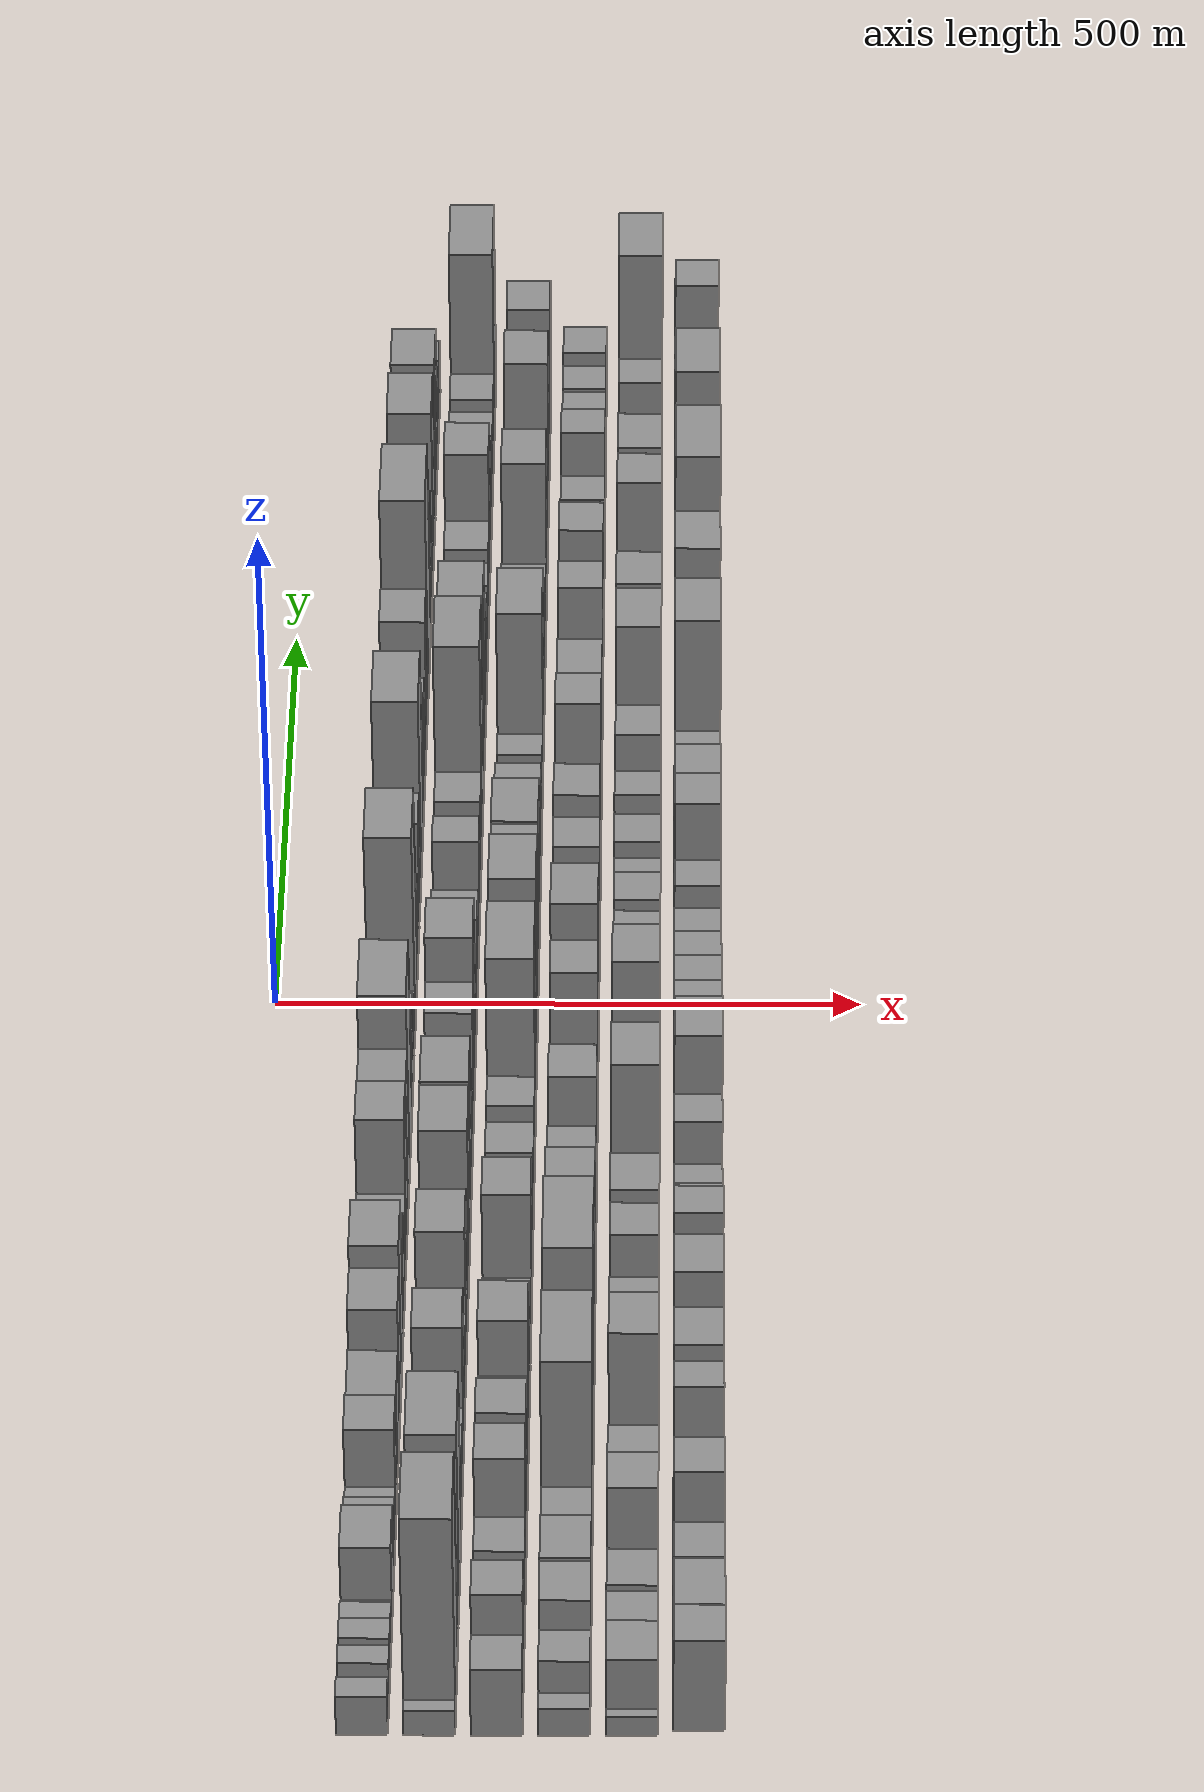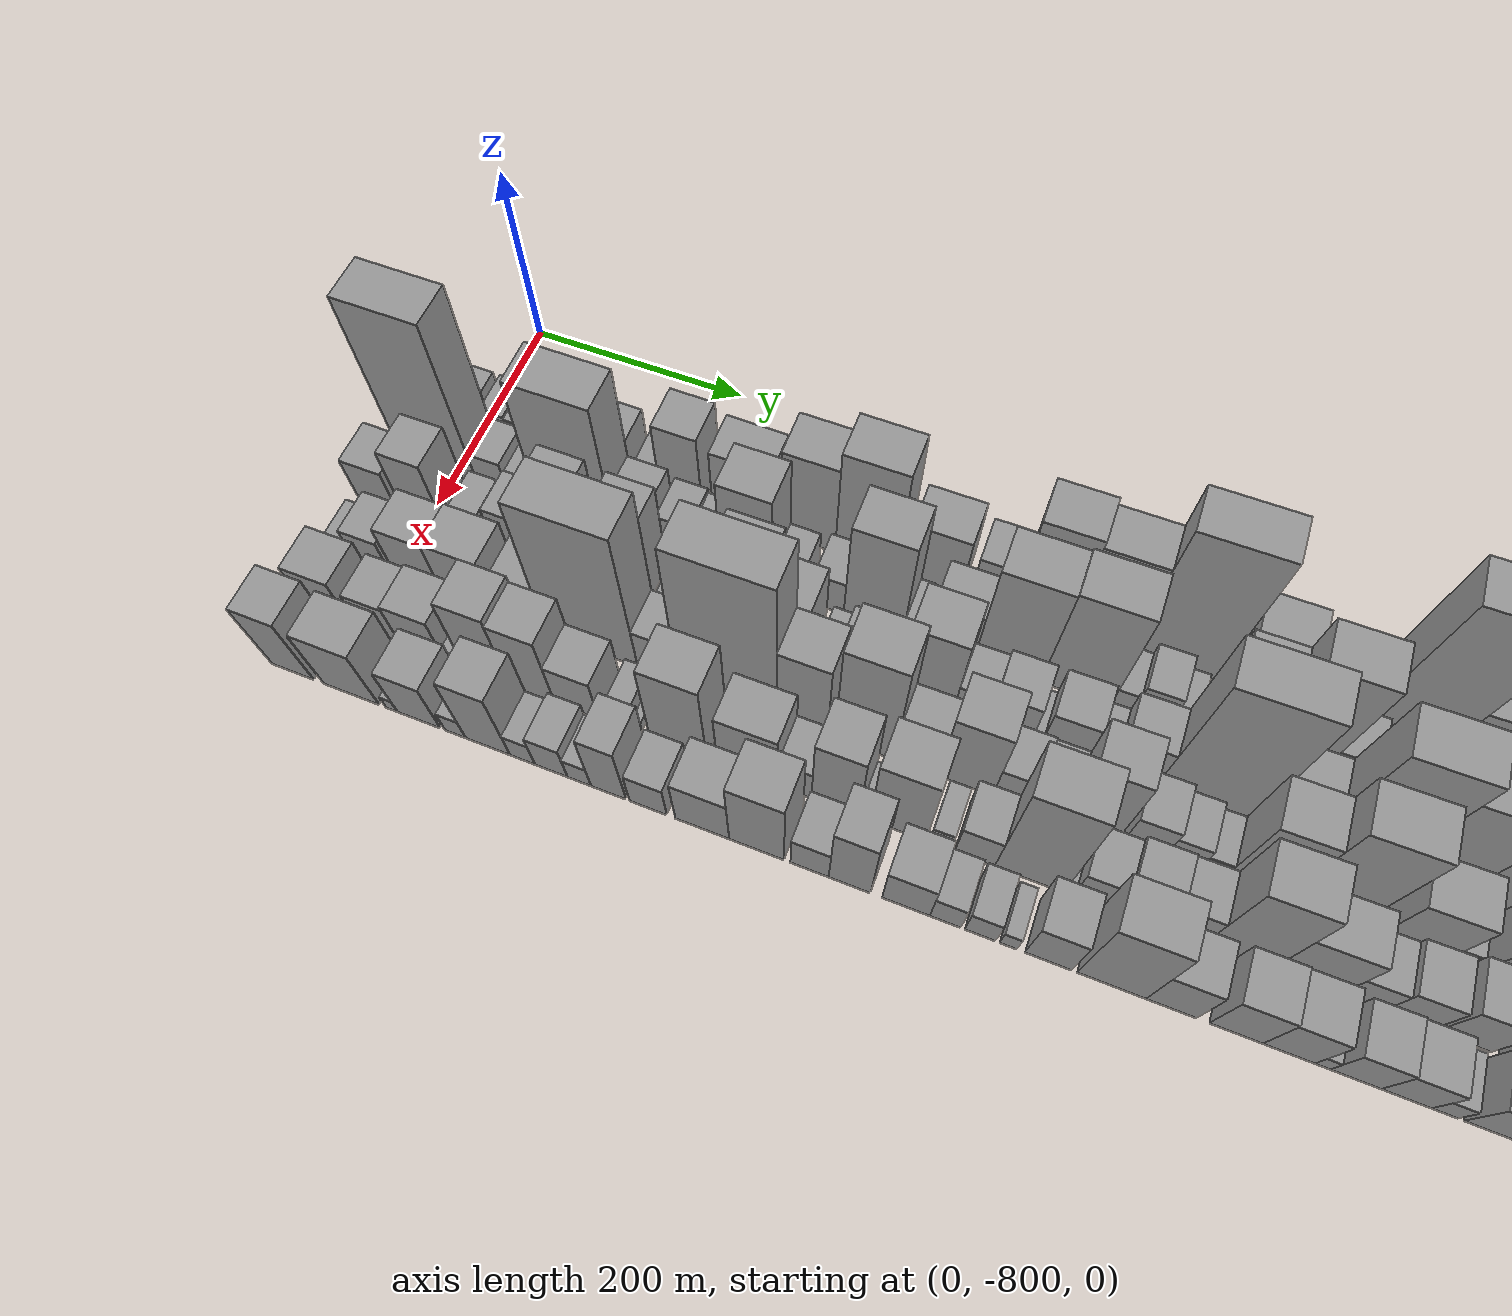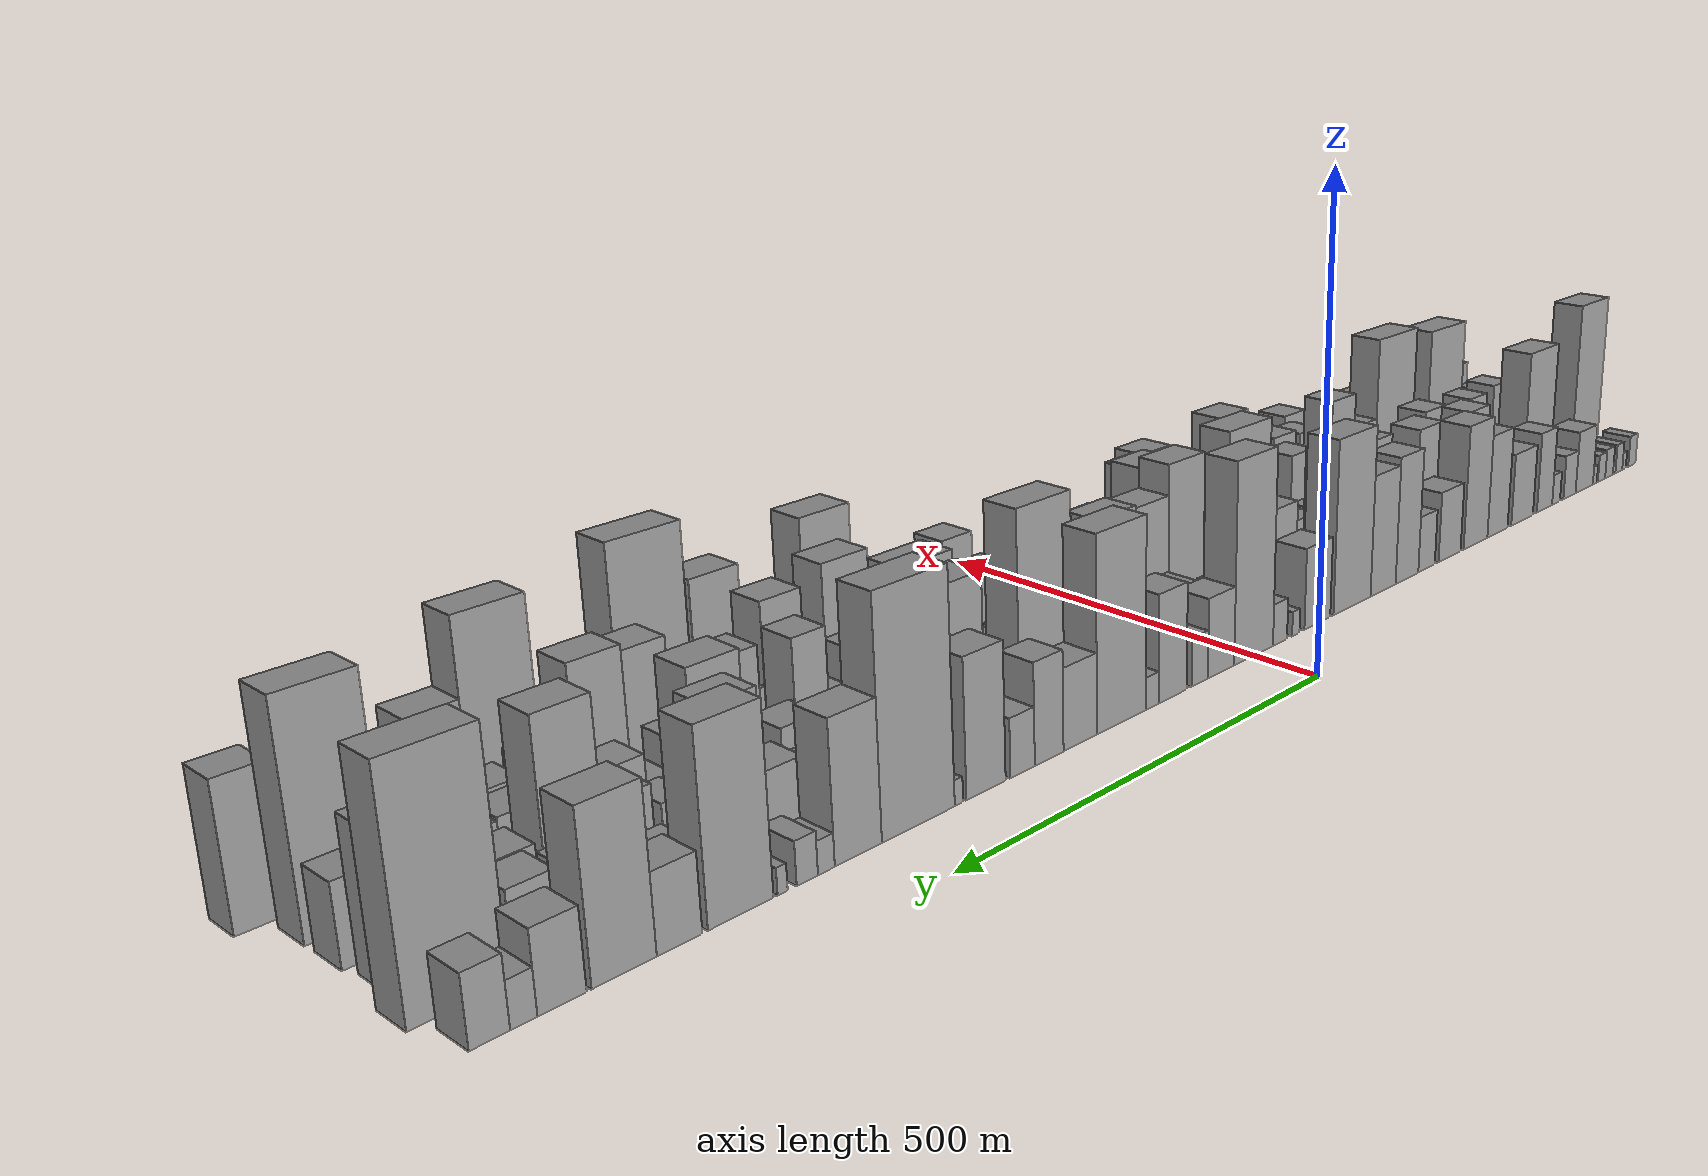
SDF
<sdf version="1.6">
 <world name="default">
  <scene>
   <sky><clouds><speed>12</speed></clouds></sky>
   <ambient>0.4 0.4 0.4 1</ambient>
   <background>0.7 0.7 0.7 1</background>
   <shadows>1</shadows>
  </scene>
  <gravity>0 0 -9.8066</gravity>
  <magnetic_field>6e-06 2.3e-05 -4.2e-05</magnetic_field>
  <physics default="0" name="default_physics" type="ode">
   <ode>
    <solver>
     <type>quick</type>
     <iters>10</iters>
     <sor>1.0</sor>
     <use_dynamic_moi_rescaling>0</use_dynamic_moi_rescaling>
    </solver>
    <constraints>
     <cfm>0</cfm>
     <erp>0.2</erp>
     <contact_max_correcting_vel>100</contact_max_correcting_vel>
     <contact_surface_layer>0.001</contact_surface_layer>
    </constraints>
   </ode>
   <max_step_size>0.004</max_step_size>
   <real_time_factor>1</real_time_factor>
   <real_time_update_rate>250</real_time_update_rate>
  </physics>
  <light name="sun" type="directional">
   <pose>0 0 10 0 0 0</pose>
   <diffuse>0.8 0.8 0.8 1</diffuse>
   <specular>0.2 0.2 0.2 1</specular>
   <attenuation>
    <range>1000</range>
    <constant>0.9</constant>
    <linear>0.01</linear>
    <quadratic>0.001</quadratic>
   </attenuation>
   <direction>-0.5 0.1 -0.9</direction>
  </light>
  <model name="building_1">
   <static>1</static>
   <pose>100.0000 -849.2613 0 0.000000 0.000000 0.000000</pose>
   <link name="link">
    <pose>0 0 21.00 0 0 0</pose>
    <collision name="collision"><geometry><box><size>40.0000 21.4774 42.0000</size></box></geometry></collision>
    <visual name="visual">
     <cast_shadows>0</cast_shadows>
     <geometry><box><size>40.0000 21.4774 42.0000</size></box></geometry>
     <material>
      <script>
       <uri>model://grey_wall/materials/scripts</uri>
       <uri>model://grey_wall/materials/textures</uri>
       <name>vrc/grey_wall</name>
      </script>
     </material>
    </visual>
   </link>
  </model>
  <model name="building_2">
   <static>1</static>
   <pose>100.0000 -826.2821 0 0.000000 0.000000 0.000000</pose>
   <link name="link">
    <pose>0 0 12.00 0 0 0</pose>
    <collision name="collision"><geometry><box><size>40.0000 10.4811 24.0000</size></box></geometry></collision>
    <visual name="visual">
     <cast_shadows>0</cast_shadows>
     <geometry><box><size>40.0000 10.4811 24.0000</size></box></geometry>
     <material>
      <script>
       <uri>model://grey_wall/materials/scripts</uri>
       <uri>model://grey_wall/materials/textures</uri>
       <name>vrc/grey_wall</name>
      </script>
     </material>
    </visual>
   </link>
  </model>
  <model name="building_3">
   <static>1</static>
   <pose>100.0000 -811.0460 0 0.000000 0.000000 0.000000</pose>
   <link name="link">
    <pose>0 0 19.50 0 0 0</pose>
    <collision name="collision"><geometry><box><size>40.0000 19.9910 39.0000</size></box></geometry></collision>
    <visual name="visual">
     <cast_shadows>0</cast_shadows>
     <geometry><box><size>40.0000 19.9910 39.0000</size></box></geometry>
     <material>
      <script>
       <uri>model://grey_wall/materials/scripts</uri>
       <uri>model://grey_wall/materials/textures</uri>
       <name>vrc/grey_wall</name>
      </script>
     </material>
    </visual>
   </link>
  </model>
  <model name="building_4">
   <static>1</static>
   <pose>100.0000 -797.5958 0 0.000000 0.000000 0.000000</pose>
   <link name="link">
    <pose>0 0 7.50 0 0 0</pose>
    <collision name="collision"><geometry><box><size>40.0000 6.9093 15.0000</size></box></geometry></collision>
    <visual name="visual">
     <cast_shadows>0</cast_shadows>
     <geometry><box><size>40.0000 6.9093 15.0000</size></box></geometry>
     <material>
      <script>
       <uri>model://grey_wall/materials/scripts</uri>
       <uri>model://grey_wall/materials/textures</uri>
       <name>vrc/grey_wall</name>
      </script>
     </material>
    </visual>
   </link>
  </model>
  <model name="building_5">
   <static>1</static>
   <pose>100.0000 -782.9081 0 0.000000 0.000000 0.000000</pose>
   <link name="link">
    <pose>0 0 19.50 0 0 0</pose>
    <collision name="collision"><geometry><box><size>40.0000 22.4662 39.0000</size></box></geometry></collision>
    <visual name="visual">
     <cast_shadows>0</cast_shadows>
     <geometry><box><size>40.0000 22.4662 39.0000</size></box></geometry>
     <material>
      <script>
       <uri>model://grey_wall/materials/scripts</uri>
       <uri>model://grey_wall/materials/textures</uri>
       <name>vrc/grey_wall</name>
      </script>
     </material>
    </visual>
   </link>
  </model>
  <model name="building_6">
   <static>1</static>
   <pose>100.0000 -761.3507 0 0.000000 0.000000 0.000000</pose>
   <link name="link">
    <pose>0 0 18.00 0 0 0</pose>
    <collision name="collision"><geometry><box><size>40.0000 20.6486 36.0000</size></box></geometry></collision>
    <visual name="visual">
     <cast_shadows>0</cast_shadows>
     <geometry><box><size>40.0000 20.6486 36.0000</size></box></geometry>
     <material>
      <script>
       <uri>model://grey_wall/materials/scripts</uri>
       <uri>model://grey_wall/materials/textures</uri>
       <name>vrc/grey_wall</name>
      </script>
     </material>
    </visual>
   </link>
  </model>
  <model name="building_7">
   <static>1</static>
   <pose>100.0000 -742.5813 0 0.000000 0.000000 0.000000</pose>
   <link name="link">
    <pose>0 0 12.00 0 0 0</pose>
    <collision name="collision"><geometry><box><size>40.0000 10.8901 24.0000</size></box></geometry></collision>
    <visual name="visual">
     <cast_shadows>0</cast_shadows>
     <geometry><box><size>40.0000 10.8901 24.0000</size></box></geometry>
     <material>
      <script>
       <uri>model://grey_wall/materials/scripts</uri>
       <uri>model://grey_wall/materials/textures</uri>
       <name>vrc/grey_wall</name>
      </script>
     </material>
    </visual>
   </link>
  </model>
  <model name="building_8">
   <static>1</static>
   <pose>100.0000 -713.3222 0 0.000000 0.000000 0.000000</pose>
   <link name="link">
    <pose>0 0 40.50 0 0 0</pose>
    <collision name="collision"><geometry><box><size>40.0000 47.6282 81.0000</size></box></geometry></collision>
    <visual name="visual">
     <cast_shadows>0</cast_shadows>
     <geometry><box><size>40.0000 47.6282 81.0000</size></box></geometry>
     <material>
      <script>
       <uri>model://grey_wall/materials/scripts</uri>
       <uri>model://grey_wall/materials/textures</uri>
       <name>vrc/grey_wall</name>
      </script>
     </material>
    </visual>
   </link>
  </model>
  <model name="building_9">
   <static>1</static>
   <pose>100.0000 -673.1779 0 0.000000 0.000000 0.000000</pose>
   <link name="link">
    <pose>0 0 28.50 0 0 0</pose>
    <collision name="collision"><geometry><box><size>40.0000 32.6604 57.0000</size></box></geometry></collision>
    <visual name="visual">
     <cast_shadows>0</cast_shadows>
     <geometry><box><size>40.0000 32.6604 57.0000</size></box></geometry>
     <material>
      <script>
       <uri>model://grey_wall/materials/scripts</uri>
       <uri>model://grey_wall/materials/textures</uri>
       <name>vrc/grey_wall</name>
      </script>
     </material>
    </visual>
   </link>
  </model>
  <model name="building_10">
   <static>1</static>
   <pose>100.0000 -637.5639 0 0.000000 0.000000 0.000000</pose>
   <link name="link">
    <pose>0 0 19.50 0 0 0</pose>
    <collision name="collision"><geometry><box><size>40.0000 20.5675 39.0000</size></box></geometry></collision>
    <visual name="visual">
     <cast_shadows>0</cast_shadows>
     <geometry><box><size>40.0000 20.5675 39.0000</size></box></geometry>
     <material>
      <script>
       <uri>model://grey_wall/materials/scripts</uri>
       <uri>model://grey_wall/materials/textures</uri>
       <name>vrc/grey_wall</name>
      </script>
     </material>
    </visual>
   </link>
  </model>
  <model name="building_11">
   <static>1</static>
   <pose>100.0000 -607.6773 0 0.000000 0.000000 0.000000</pose>
   <link name="link">
    <pose>0 0 51.00 0 0 0</pose>
    <collision name="collision"><geometry><box><size>40.0000 39.2058 102.0000</size></box></geometry></collision>
    <visual name="visual">
     <cast_shadows>0</cast_shadows>
     <geometry><box><size>40.0000 39.2058 102.0000</size></box></geometry>
     <material>
      <script>
       <uri>model://grey_wall/materials/scripts</uri>
       <uri>model://grey_wall/materials/textures</uri>
       <name>vrc/grey_wall</name>
      </script>
     </material>
    </visual>
   </link>
  </model>
  <model name="building_12">
   <static>1</static>
   <pose>100.0000 -551.1568 0 0.000000 0.000000 0.000000</pose>
   <link name="link">
    <pose>0 0 45.00 0 0 0</pose>
    <collision name="collision"><geometry><box><size>40.0000 53.8351 90.0000</size></box></geometry></collision>
    <visual name="visual">
     <cast_shadows>0</cast_shadows>
     <geometry><box><size>40.0000 53.8351 90.0000</size></box></geometry>
     <material>
      <script>
       <uri>model://grey_wall/materials/scripts</uri>
       <uri>model://grey_wall/materials/textures</uri>
       <name>vrc/grey_wall</name>
      </script>
     </material>
    </visual>
   </link>
  </model>
  <model name="building_13">
   <static>1</static>
   <pose>100.0000 -491.0969 0 0.000000 0.000000 0.000000</pose>
   <link name="link">
    <pose>0 0 63.00 0 0 0</pose>
    <collision name="collision"><geometry><box><size>40.0000 48.2848 126.0000</size></box></geometry></collision>
    <visual name="visual">
     <cast_shadows>0</cast_shadows>
     <geometry><box><size>40.0000 48.2848 126.0000</size></box></geometry>
     <material>
      <script>
       <uri>model://grey_wall/materials/scripts</uri>
       <uri>model://grey_wall/materials/textures</uri>
       <name>vrc/grey_wall</name>
      </script>
     </material>
    </visual>
   </link>
  </model>
  <model name="building_14">
   <static>1</static>
   <pose>100.0000 -439.5208 0 0.000000 0.000000 0.000000</pose>
   <link name="link">
    <pose>0 0 75.00 0 0 0</pose>
    <collision name="collision"><geometry><box><size>40.0000 54.8674 150.0000</size></box></geometry></collision>
    <visual name="visual">
     <cast_shadows>0</cast_shadows>
     <geometry><box><size>40.0000 54.8674 150.0000</size></box></geometry>
     <material>
      <script>
       <uri>model://grey_wall/materials/scripts</uri>
       <uri>model://grey_wall/materials/textures</uri>
       <name>vrc/grey_wall</name>
      </script>
     </material>
    </visual>
   </link>
  </model>
  <model name="building_15">
   <static>1</static>
   <pose>100.0000 -380.6242 0 0.000000 0.000000 0.000000</pose>
   <link name="link">
    <pose>0 0 42.00 0 0 0</pose>
    <collision name="collision"><geometry><box><size>40.0000 48.9257 84.0000</size></box></geometry></collision>
    <visual name="visual">
     <cast_shadows>0</cast_shadows>
     <geometry><box><size>40.0000 48.9257 84.0000</size></box></geometry>
     <material>
      <script>
       <uri>model://grey_wall/materials/scripts</uri>
       <uri>model://grey_wall/materials/textures</uri>
       <name>vrc/grey_wall</name>
      </script>
     </material>
    </visual>
   </link>
  </model>
  <model name="building_16">
   <static>1</static>
   <pose>100.0000 -330.4229 0 0.000000 0.000000 0.000000</pose>
   <link name="link">
    <pose>0 0 33.00 0 0 0</pose>
    <collision name="collision"><geometry><box><size>40.0000 35.4769 66.0000</size></box></geometry></collision>
    <visual name="visual">
     <cast_shadows>0</cast_shadows>
     <geometry><box><size>40.0000 35.4769 66.0000</size></box></geometry>
     <material>
      <script>
       <uri>model://grey_wall/materials/scripts</uri>
       <uri>model://grey_wall/materials/textures</uri>
       <name>vrc/grey_wall</name>
      </script>
     </material>
    </visual>
   </link>
  </model>
  <model name="building_17">
   <static>1</static>
   <pose>100.0000 -289.0491 0 0.000000 0.000000 0.000000</pose>
   <link name="link">
    <pose>0 0 73.50 0 0 0</pose>
    <collision name="collision"><geometry><box><size>40.0000 47.2708 147.0000</size></box></geometry></collision>
    <visual name="visual">
     <cast_shadows>0</cast_shadows>
     <geometry><box><size>40.0000 47.2708 147.0000</size></box></geometry>
     <material>
      <script>
       <uri>model://grey_wall/materials/scripts</uri>
       <uri>model://grey_wall/materials/textures</uri>
       <name>vrc/grey_wall</name>
      </script>
     </material>
    </visual>
   </link>
  </model>
  <model name="building_18">
   <static>1</static>
   <pose>100.0000 -240.0989 0 0.000000 0.000000 0.000000</pose>
   <link name="link">
    <pose>0 0 69.00 0 0 0</pose>
    <collision name="collision"><geometry><box><size>40.0000 50.6296 138.0000</size></box></geometry></collision>
    <visual name="visual">
     <cast_shadows>0</cast_shadows>
     <geometry><box><size>40.0000 50.6296 138.0000</size></box></geometry>
     <material>
      <script>
       <uri>model://grey_wall/materials/scripts</uri>
       <uri>model://grey_wall/materials/textures</uri>
       <name>vrc/grey_wall</name>
      </script>
     </material>
    </visual>
   </link>
  </model>
  <model name="building_19">
   <static>1</static>
   <pose>100.0000 -179.0395 0 0.000000 0.000000 0.000000</pose>
   <link name="link">
    <pose>0 0 97.50 0 0 0</pose>
    <collision name="collision"><geometry><box><size>40.0000 71.4891 195.0000</size></box></geometry></collision>
    <visual name="visual">
     <cast_shadows>0</cast_shadows>
     <geometry><box><size>40.0000 71.4891 195.0000</size></box></geometry>
     <material>
      <script>
       <uri>model://grey_wall/materials/scripts</uri>
       <uri>model://grey_wall/materials/textures</uri>
       <name>vrc/grey_wall</name>
      </script>
     </material>
    </visual>
   </link>
  </model>
  <model name="building_20">
   <static>1</static>
   <pose>100.0000 -113.5583 0 0.000000 0.000000 0.000000</pose>
   <link name="link">
    <pose>0 0 45.00 0 0 0</pose>
    <collision name="collision"><geometry><box><size>40.0000 47.4733 90.0000</size></box></geometry></collision>
    <visual name="visual">
     <cast_shadows>0</cast_shadows>
     <geometry><box><size>40.0000 47.4733 90.0000</size></box></geometry>
     <material>
      <script>
       <uri>model://grey_wall/materials/scripts</uri>
       <uri>model://grey_wall/materials/textures</uri>
       <name>vrc/grey_wall</name>
      </script>
     </material>
    </visual>
   </link>
  </model>
  <model name="building_21">
   <static>1</static>
   <pose>100.0000 -74.3829 0 0.000000 0.000000 0.000000</pose>
   <link name="link">
    <pose>0 0 13.50 0 0 0</pose>
    <collision name="collision"><geometry><box><size>40.0000 12.8774 27.0000</size></box></geometry></collision>
    <visual name="visual">
     <cast_shadows>0</cast_shadows>
     <geometry><box><size>40.0000 12.8774 27.0000</size></box></geometry>
     <material>
      <script>
       <uri>model://grey_wall/materials/scripts</uri>
       <uri>model://grey_wall/materials/textures</uri>
       <name>vrc/grey_wall</name>
      </script>
     </material>
    </visual>
   </link>
  </model>
  <model name="building_22">
   <static>1</static>
   <pose>100.0000 -46.6453 0 0.000000 0.000000 0.000000</pose>
   <link name="link">
    <pose>0 0 22.50 0 0 0</pose>
    <collision name="collision"><geometry><box><size>40.0000 24.5978 45.0000</size></box></geometry></collision>
    <visual name="visual">
     <cast_shadows>0</cast_shadows>
     <geometry><box><size>40.0000 24.5978 45.0000</size></box></geometry>
     <material>
      <script>
       <uri>model://grey_wall/materials/scripts</uri>
       <uri>model://grey_wall/materials/textures</uri>
       <name>vrc/grey_wall</name>
      </script>
     </material>
    </visual>
   </link>
  </model>
  <model name="building_23">
   <static>1</static>
   <pose>100.0000 -1.6300 0 0.000000 0.000000 0.000000</pose>
   <link name="link">
    <pose>0 0 106.50 0 0 0</pose>
    <collision name="collision"><geometry><box><size>40.0000 65.4329 213.0000</size></box></geometry></collision>
    <visual name="visual">
     <cast_shadows>0</cast_shadows>
     <geometry><box><size>40.0000 65.4329 213.0000</size></box></geometry>
     <material>
      <script>
       <uri>model://grey_wall/materials/scripts</uri>
       <uri>model://grey_wall/materials/textures</uri>
       <name>vrc/grey_wall</name>
      </script>
     </material>
    </visual>
   </link>
  </model>
  <model name="building_24">
   <static>1</static>
   <pose>100.0000 52.3423 0 0.000000 0.000000 0.000000</pose>
   <link name="link">
    <pose>0 0 42.00 0 0 0</pose>
    <collision name="collision"><geometry><box><size>40.0000 42.5116 84.0000</size></box></geometry></collision>
    <visual name="visual">
     <cast_shadows>0</cast_shadows>
     <geometry><box><size>40.0000 42.5116 84.0000</size></box></geometry>
     <material>
      <script>
       <uri>model://grey_wall/materials/scripts</uri>
       <uri>model://grey_wall/materials/textures</uri>
       <name>vrc/grey_wall</name>
      </script>
     </material>
    </visual>
   </link>
  </model>
  <model name="building_25">
   <static>1</static>
   <pose>100.0000 86.3968 0 0.000000 0.000000 0.000000</pose>
   <link name="link">
    <pose>0 0 25.50 0 0 0</pose>
    <collision name="collision"><geometry><box><size>40.0000 25.5975 51.0000</size></box></geometry></collision>
    <visual name="visual">
     <cast_shadows>0</cast_shadows>
     <geometry><box><size>40.0000 25.5975 51.0000</size></box></geometry>
     <material>
      <script>
       <uri>model://grey_wall/materials/scripts</uri>
       <uri>model://grey_wall/materials/textures</uri>
       <name>vrc/grey_wall</name>
      </script>
     </material>
    </visual>
   </link>
  </model>
  <model name="building_26">
   <static>1</static>
   <pose>100.0000 128.4170 0 0.000000 0.000000 0.000000</pose>
   <link name="link">
    <pose>0 0 55.50 0 0 0</pose>
    <collision name="collision"><geometry><box><size>40.0000 42.4429 111.0000</size></box></geometry></collision>
    <visual name="visual">
     <cast_shadows>0</cast_shadows>
     <geometry><box><size>40.0000 42.4429 111.0000</size></box></geometry>
     <material>
      <script>
       <uri>model://grey_wall/materials/scripts</uri>
       <uri>model://grey_wall/materials/textures</uri>
       <name>vrc/grey_wall</name>
      </script>
     </material>
    </visual>
   </link>
  </model>
  <model name="building_27">
   <static>1</static>
   <pose>100.0000 159.2440 0 0.000000 0.000000 0.000000</pose>
   <link name="link">
    <pose>0 0 16.50 0 0 0</pose>
    <collision name="collision"><geometry><box><size>40.0000 19.2112 33.0000</size></box></geometry></collision>
    <visual name="visual">
     <cast_shadows>0</cast_shadows>
     <geometry><box><size>40.0000 19.2112 33.0000</size></box></geometry>
     <material>
      <script>
       <uri>model://grey_wall/materials/scripts</uri>
       <uri>model://grey_wall/materials/textures</uri>
       <name>vrc/grey_wall</name>
      </script>
     </material>
    </visual>
   </link>
  </model>
  <model name="building_28">
   <static>1</static>
   <pose>100.0000 203.8309 0 0.000000 0.000000 0.000000</pose>
   <link name="link">
    <pose>0 0 97.50 0 0 0</pose>
    <collision name="collision"><geometry><box><size>40.0000 69.9627 195.0000</size></box></geometry></collision>
    <visual name="visual">
     <cast_shadows>0</cast_shadows>
     <geometry><box><size>40.0000 69.9627 195.0000</size></box></geometry>
     <material>
      <script>
       <uri>model://grey_wall/materials/scripts</uri>
       <uri>model://grey_wall/materials/textures</uri>
       <name>vrc/grey_wall</name>
      </script>
     </material>
    </visual>
   </link>
  </model>
  <model name="building_29">
   <static>1</static>
   <pose>100.0000 261.5322 0 0.000000 0.000000 0.000000</pose>
   <link name="link">
    <pose>0 0 40.50 0 0 0</pose>
    <collision name="collision"><geometry><box><size>40.0000 45.4399 81.0000</size></box></geometry></collision>
    <visual name="visual">
     <cast_shadows>0</cast_shadows>
     <geometry><box><size>40.0000 45.4399 81.0000</size></box></geometry>
     <material>
      <script>
       <uri>model://grey_wall/materials/scripts</uri>
       <uri>model://grey_wall/materials/textures</uri>
       <name>vrc/grey_wall</name>
      </script>
     </material>
    </visual>
   </link>
  </model>
  <model name="building_30">
   <static>1</static>
   <pose>100.0000 303.1188 0 0.000000 0.000000 0.000000</pose>
   <link name="link">
    <pose>0 0 49.50 0 0 0</pose>
    <collision name="collision"><geometry><box><size>40.0000 37.7334 99.0000</size></box></geometry></collision>
    <visual name="visual">
     <cast_shadows>0</cast_shadows>
     <geometry><box><size>40.0000 37.7334 99.0000</size></box></geometry>
     <material>
      <script>
       <uri>model://grey_wall/materials/scripts</uri>
       <uri>model://grey_wall/materials/textures</uri>
       <name>vrc/grey_wall</name>
      </script>
     </material>
    </visual>
   </link>
  </model>
  <model name="building_31">
   <static>1</static>
   <pose>100.0000 337.5328 0 0.000000 0.000000 0.000000</pose>
   <link name="link">
    <pose>0 0 28.50 0 0 0</pose>
    <collision name="collision"><geometry><box><size>40.0000 31.0945 57.0000</size></box></geometry></collision>
    <visual name="visual">
     <cast_shadows>0</cast_shadows>
     <geometry><box><size>40.0000 31.0945 57.0000</size></box></geometry>
     <material>
      <script>
       <uri>model://grey_wall/materials/scripts</uri>
       <uri>model://grey_wall/materials/textures</uri>
       <name>vrc/grey_wall</name>
      </script>
     </material>
    </visual>
   </link>
  </model>
  <model name="building_32">
   <static>1</static>
   <pose>100.0000 383.0558 0 0.000000 0.000000 0.000000</pose>
   <link name="link">
    <pose>0 0 66.00 0 0 0</pose>
    <collision name="collision"><geometry><box><size>40.0000 47.9517 132.0000</size></box></geometry></collision>
    <visual name="visual">
     <cast_shadows>0</cast_shadows>
     <geometry><box><size>40.0000 47.9517 132.0000</size></box></geometry>
     <material>
      <script>
       <uri>model://grey_wall/materials/scripts</uri>
       <uri>model://grey_wall/materials/textures</uri>
       <name>vrc/grey_wall</name>
      </script>
     </material>
    </visual>
   </link>
  </model>
  <model name="building_33">
   <static>1</static>
   <pose>100.0000 415.9658 0 0.000000 0.000000 0.000000</pose>
   <link name="link">
    <pose>0 0 12.00 0 0 0</pose>
    <collision name="collision"><geometry><box><size>40.0000 9.8683 24.0000</size></box></geometry></collision>
    <visual name="visual">
     <cast_shadows>0</cast_shadows>
     <geometry><box><size>40.0000 9.8683 24.0000</size></box></geometry>
     <material>
      <script>
       <uri>model://grey_wall/materials/scripts</uri>
       <uri>model://grey_wall/materials/textures</uri>
       <name>vrc/grey_wall</name>
      </script>
     </material>
    </visual>
   </link>
  </model>
  <model name="building_34">
   <static>1</static>
   <pose>100.0000 462.2733 0 0.000000 0.000000 0.000000</pose>
   <link name="link">
    <pose>0 0 109.50 0 0 0</pose>
    <collision name="collision"><geometry><box><size>40.0000 82.7467 219.0000</size></box></geometry></collision>
    <visual name="visual">
     <cast_shadows>0</cast_shadows>
     <geometry><box><size>40.0000 82.7467 219.0000</size></box></geometry>
     <material>
      <script>
       <uri>model://grey_wall/materials/scripts</uri>
       <uri>model://grey_wall/materials/textures</uri>
       <name>vrc/grey_wall</name>
      </script>
     </material>
    </visual>
   </link>
  </model>
  <model name="building_35">
   <static>1</static>
   <pose>100.0000 528.7735 0 0.000000 0.000000 0.000000</pose>
   <link name="link">
    <pose>0 0 64.50 0 0 0</pose>
    <collision name="collision"><geometry><box><size>40.0000 50.2537 129.0000</size></box></geometry></collision>
    <visual name="visual">
     <cast_shadows>0</cast_shadows>
     <geometry><box><size>40.0000 50.2537 129.0000</size></box></geometry>
     <material>
      <script>
       <uri>model://grey_wall/materials/scripts</uri>
       <uri>model://grey_wall/materials/textures</uri>
       <name>vrc/grey_wall</name>
      </script>
     </material>
    </visual>
   </link>
  </model>
  <model name="building_36">
   <static>1</static>
   <pose>100.0000 562.5985 0 0.000000 0.000000 0.000000</pose>
   <link name="link">
    <pose>0 0 15.00 0 0 0</pose>
    <collision name="collision"><geometry><box><size>40.0000 17.3963 30.0000</size></box></geometry></collision>
    <visual name="visual">
     <cast_shadows>0</cast_shadows>
     <geometry><box><size>40.0000 17.3963 30.0000</size></box></geometry>
     <material>
      <script>
       <uri>model://grey_wall/materials/scripts</uri>
       <uri>model://grey_wall/materials/textures</uri>
       <name>vrc/grey_wall</name>
      </script>
     </material>
    </visual>
   </link>
  </model>
  <model name="building_37">
   <static>1</static>
   <pose>100.0000 582.0654 0 0.000000 0.000000 0.000000</pose>
   <link name="link">
    <pose>0 0 19.50 0 0 0</pose>
    <collision name="collision"><geometry><box><size>40.0000 21.5375 39.0000</size></box></geometry></collision>
    <visual name="visual">
     <cast_shadows>0</cast_shadows>
     <geometry><box><size>40.0000 21.5375 39.0000</size></box></geometry>
     <material>
      <script>
       <uri>model://grey_wall/materials/scripts</uri>
       <uri>model://grey_wall/materials/textures</uri>
       <name>vrc/grey_wall</name>
      </script>
     </material>
    </visual>
   </link>
  </model>
  <model name="building_38">
   <static>1</static>
   <pose>100.0000 606.7923 0 0.000000 0.000000 0.000000</pose>
   <link name="link">
    <pose>0 0 12.00 0 0 0</pose>
    <collision name="collision"><geometry><box><size>40.0000 9.9163 24.0000</size></box></geometry></collision>
    <visual name="visual">
     <cast_shadows>0</cast_shadows>
     <geometry><box><size>40.0000 9.9163 24.0000</size></box></geometry>
     <material>
      <script>
       <uri>model://grey_wall/materials/scripts</uri>
       <uri>model://grey_wall/materials/textures</uri>
       <name>vrc/grey_wall</name>
      </script>
     </material>
    </visual>
   </link>
  </model>
  <model name="building_39">
   <static>1</static>
   <pose>100.0000 646.8354 0 0.000000 0.000000 0.000000</pose>
   <link name="link">
    <pose>0 0 84.00 0 0 0</pose>
    <collision name="collision"><geometry><box><size>40.0000 62.1698 168.0000</size></box></geometry></collision>
    <visual name="visual">
     <cast_shadows>0</cast_shadows>
     <geometry><box><size>40.0000 62.1698 168.0000</size></box></geometry>
     <material>
      <script>
       <uri>model://grey_wall/materials/scripts</uri>
       <uri>model://grey_wall/materials/textures</uri>
       <name>vrc/grey_wall</name>
      </script>
     </material>
    </visual>
   </link>
  </model>
  <model name="building_40">
   <static>1</static>
   <pose>100.0000 703.2620 0 0.000000 0.000000 0.000000</pose>
   <link name="link">
    <pose>0 0 34.50 0 0 0</pose>
    <collision name="collision"><geometry><box><size>40.0000 40.6835 69.0000</size></box></geometry></collision>
    <visual name="visual">
     <cast_shadows>0</cast_shadows>
     <geometry><box><size>40.0000 40.6835 69.0000</size></box></geometry>
     <material>
      <script>
       <uri>model://grey_wall/materials/scripts</uri>
       <uri>model://grey_wall/materials/textures</uri>
       <name>vrc/grey_wall</name>
      </script>
     </material>
    </visual>
   </link>
  </model>
  <model name="building_41">
   <static>1</static>
   <pose>100.0000 751.2611 0 0.000000 0.000000 0.000000</pose>
   <link name="link">
    <pose>0 0 72.00 0 0 0</pose>
    <collision name="collision"><geometry><box><size>40.0000 55.3147 144.0000</size></box></geometry></collision>
    <visual name="visual">
     <cast_shadows>0</cast_shadows>
     <geometry><box><size>40.0000 55.3147 144.0000</size></box></geometry>
     <material>
      <script>
       <uri>model://grey_wall/materials/scripts</uri>
       <uri>model://grey_wall/materials/textures</uri>
       <name>vrc/grey_wall</name>
      </script>
     </material>
    </visual>
   </link>
  </model>
  <model name="building_42">
   <static>1</static>
   <pose>100.0000 802.6028 0 0.000000 0.000000 0.000000</pose>
   <link name="link">
    <pose>0 0 34.50 0 0 0</pose>
    <collision name="collision"><geometry><box><size>40.0000 39.3687 69.0000</size></box></geometry></collision>
    <visual name="visual">
     <cast_shadows>0</cast_shadows>
     <geometry><box><size>40.0000 39.3687 69.0000</size></box></geometry>
     <material>
      <script>
       <uri>model://grey_wall/materials/scripts</uri>
       <uri>model://grey_wall/materials/textures</uri>
       <name>vrc/grey_wall</name>
      </script>
     </material>
    </visual>
   </link>
  </model>
  <model name="building_43">
   <static>1</static>
   <pose>100.0000 832.8690 0 0.000000 0.000000 0.000000</pose>
   <link name="link">
    <pose>0 0 19.50 0 0 0</pose>
    <collision name="collision"><geometry><box><size>40.0000 21.1639 39.0000</size></box></geometry></collision>
    <visual name="visual">
     <cast_shadows>0</cast_shadows>
     <geometry><box><size>40.0000 21.1639 39.0000</size></box></geometry>
     <material>
      <script>
       <uri>model://grey_wall/materials/scripts</uri>
       <uri>model://grey_wall/materials/textures</uri>
       <name>vrc/grey_wall</name>
      </script>
     </material>
    </visual>
   </link>
  </model>
  <model name="building_44">
   <static>1</static>
   <pose>100.0000 859.0596 0 0.000000 0.000000 0.000000</pose>
   <link name="link">
    <pose>0 0 30.00 0 0 0</pose>
    <collision name="collision"><geometry><box><size>40.0000 31.2172 60.0000</size></box></geometry></collision>
    <visual name="visual">
     <cast_shadows>0</cast_shadows>
     <geometry><box><size>40.0000 31.2172 60.0000</size></box></geometry>
     <material>
      <script>
       <uri>model://grey_wall/materials/scripts</uri>
       <uri>model://grey_wall/materials/textures</uri>
       <name>vrc/grey_wall</name>
      </script>
     </material>
    </visual>
   </link>
  </model>
  <model name="building_45">
   <static>1</static>
   <pose>152.0000 -854.0687 0 0.000000 0.000000 0.000000</pose>
   <link name="link">
    <pose>0 0 13.50 0 0 0</pose>
    <collision name="collision"><geometry><box><size>40.0000 11.8627 27.0000</size></box></geometry></collision>
    <visual name="visual">
     <cast_shadows>0</cast_shadows>
     <geometry><box><size>40.0000 11.8627 27.0000</size></box></geometry>
     <material>
      <script>
       <uri>model://grey_wall/materials/scripts</uri>
       <uri>model://grey_wall/materials/textures</uri>
       <name>vrc/grey_wall</name>
      </script>
     </material>
    </visual>
   </link>
  </model>
  <model name="building_46">
   <static>1</static>
   <pose>152.0000 -811.6512 0 0.000000 0.000000 0.000000</pose>
   <link name="link">
    <pose>0 0 111.00 0 0 0</pose>
    <collision name="collision"><geometry><box><size>40.0000 72.9722 222.0000</size></box></geometry></collision>
    <visual name="visual">
     <cast_shadows>0</cast_shadows>
     <geometry><box><size>40.0000 72.9722 222.0000</size></box></geometry>
     <material>
      <script>
       <uri>model://grey_wall/materials/scripts</uri>
       <uri>model://grey_wall/materials/textures</uri>
       <name>vrc/grey_wall</name>
      </script>
     </material>
    </visual>
   </link>
  </model>
  <model name="building_47">
   <static>1</static>
   <pose>152.0000 -760.4063 0 0.000000 0.000000 0.000000</pose>
   <link name="link">
    <pose>0 0 27.00 0 0 0</pose>
    <collision name="collision"><geometry><box><size>40.0000 29.5176 54.0000</size></box></geometry></collision>
    <visual name="visual">
     <cast_shadows>0</cast_shadows>
     <geometry><box><size>40.0000 29.5176 54.0000</size></box></geometry>
     <material>
      <script>
       <uri>model://grey_wall/materials/scripts</uri>
       <uri>model://grey_wall/materials/textures</uri>
       <name>vrc/grey_wall</name>
      </script>
     </material>
    </visual>
   </link>
  </model>
  <model name="building_48">
   <static>1</static>
   <pose>152.0000 -729.2760 0 0.000000 0.000000 0.000000</pose>
   <link name="link">
    <pose>0 0 24.00 0 0 0</pose>
    <collision name="collision"><geometry><box><size>40.0000 24.7430 48.0000</size></box></geometry></collision>
    <visual name="visual">
     <cast_shadows>0</cast_shadows>
     <geometry><box><size>40.0000 24.7430 48.0000</size></box></geometry>
     <material>
      <script>
       <uri>model://grey_wall/materials/scripts</uri>
       <uri>model://grey_wall/materials/textures</uri>
       <name>vrc/grey_wall</name>
      </script>
     </material>
    </visual>
   </link>
  </model>
  <model name="building_49">
   <static>1</static>
   <pose>152.0000 -681.2867 0 0.000000 0.000000 0.000000</pose>
   <link name="link">
    <pose>0 0 91.50 0 0 0</pose>
    <collision name="collision"><geometry><box><size>40.0000 71.2357 183.0000</size></box></geometry></collision>
    <visual name="visual">
     <cast_shadows>0</cast_shadows>
     <geometry><box><size>40.0000 71.2357 183.0000</size></box></geometry>
     <material>
      <script>
       <uri>model://grey_wall/materials/scripts</uri>
       <uri>model://grey_wall/materials/textures</uri>
       <name>vrc/grey_wall</name>
      </script>
     </material>
    </visual>
   </link>
  </model>
  <model name="building_50">
   <static>1</static>
   <pose>152.0000 -627.7862 0 0.000000 0.000000 0.000000</pose>
   <link name="link">
    <pose>0 0 33.00 0 0 0</pose>
    <collision name="collision"><geometry><box><size>40.0000 35.7652 66.0000</size></box></geometry></collision>
    <visual name="visual">
     <cast_shadows>0</cast_shadows>
     <geometry><box><size>40.0000 35.7652 66.0000</size></box></geometry>
     <material>
      <script>
       <uri>model://grey_wall/materials/scripts</uri>
       <uri>model://grey_wall/materials/textures</uri>
       <name>vrc/grey_wall</name>
      </script>
     </material>
    </visual>
   </link>
  </model>
  <model name="building_51">
   <static>1</static>
   <pose>152.0000 -589.1586 0 0.000000 0.000000 0.000000</pose>
   <link name="link">
    <pose>0 0 28.50 0 0 0</pose>
    <collision name="collision"><geometry><box><size>40.0000 29.4901 57.0000</size></box></geometry></collision>
    <visual name="visual">
     <cast_shadows>0</cast_shadows>
     <geometry><box><size>40.0000 29.4901 57.0000</size></box></geometry>
     <material>
      <script>
       <uri>model://grey_wall/materials/scripts</uri>
       <uri>model://grey_wall/materials/textures</uri>
       <name>vrc/grey_wall</name>
      </script>
     </material>
    </visual>
   </link>
  </model>
  <model name="building_52">
   <static>1</static>
   <pose>152.0000 -561.6178 0 0.000000 0.000000 0.000000</pose>
   <link name="link">
    <pose>0 0 25.50 0 0 0</pose>
    <collision name="collision"><geometry><box><size>40.0000 25.5915 51.0000</size></box></geometry></collision>
    <visual name="visual">
     <cast_shadows>0</cast_shadows>
     <geometry><box><size>40.0000 25.5915 51.0000</size></box></geometry>
     <material>
      <script>
       <uri>model://grey_wall/materials/scripts</uri>
       <uri>model://grey_wall/materials/textures</uri>
       <name>vrc/grey_wall</name>
      </script>
     </material>
    </visual>
   </link>
  </model>
  <model name="building_53">
   <static>1</static>
   <pose>152.0000 -525.6842 0 0.000000 0.000000 0.000000</pose>
   <link name="link">
    <pose>0 0 69.00 0 0 0</pose>
    <collision name="collision"><geometry><box><size>40.0000 46.2758 138.0000</size></box></geometry></collision>
    <visual name="visual">
     <cast_shadows>0</cast_shadows>
     <geometry><box><size>40.0000 46.2758 138.0000</size></box></geometry>
     <material>
      <script>
       <uri>model://grey_wall/materials/scripts</uri>
       <uri>model://grey_wall/materials/textures</uri>
       <name>vrc/grey_wall</name>
      </script>
     </material>
    </visual>
   </link>
  </model>
  <model name="building_54">
   <static>1</static>
   <pose>152.0000 -489.3933 0 0.000000 0.000000 0.000000</pose>
   <link name="link">
    <pose>0 0 22.50 0 0 0</pose>
    <collision name="collision"><geometry><box><size>40.0000 26.3059 45.0000</size></box></geometry></collision>
    <visual name="visual">
     <cast_shadows>0</cast_shadows>
     <geometry><box><size>40.0000 26.3059 45.0000</size></box></geometry>
     <material>
      <script>
       <uri>model://grey_wall/materials/scripts</uri>
       <uri>model://grey_wall/materials/textures</uri>
       <name>vrc/grey_wall</name>
      </script>
     </material>
    </visual>
   </link>
  </model>
  <model name="building_55">
   <static>1</static>
   <pose>152.0000 -453.8426 0 0.000000 0.000000 0.000000</pose>
   <link name="link">
    <pose>0 0 25.50 0 0 0</pose>
    <collision name="collision"><geometry><box><size>40.0000 26.7954 51.0000</size></box></geometry></collision>
    <visual name="visual">
     <cast_shadows>0</cast_shadows>
     <geometry><box><size>40.0000 26.7954 51.0000</size></box></geometry>
     <material>
      <script>
       <uri>model://grey_wall/materials/scripts</uri>
       <uri>model://grey_wall/materials/textures</uri>
       <name>vrc/grey_wall</name>
      </script>
     </material>
    </visual>
   </link>
  </model>
  <model name="building_56">
   <static>1</static>
   <pose>152.0000 -414.7231 0 0.000000 0.000000 0.000000</pose>
   <link name="link">
    <pose>0 0 70.50 0 0 0</pose>
    <collision name="collision"><geometry><box><size>40.0000 51.4436 141.0000</size></box></geometry></collision>
    <visual name="visual">
     <cast_shadows>0</cast_shadows>
     <geometry><box><size>40.0000 51.4436 141.0000</size></box></geometry>
     <material>
      <script>
       <uri>model://grey_wall/materials/scripts</uri>
       <uri>model://grey_wall/materials/textures</uri>
       <name>vrc/grey_wall</name>
      </script>
     </material>
    </visual>
   </link>
  </model>
  <model name="building_57">
   <static>1</static>
   <pose>152.0000 -382.9502 0 0.000000 0.000000 0.000000</pose>
   <link name="link">
    <pose>0 0 13.50 0 0 0</pose>
    <collision name="collision"><geometry><box><size>40.0000 12.1022 27.0000</size></box></geometry></collision>
    <visual name="visual">
     <cast_shadows>0</cast_shadows>
     <geometry><box><size>40.0000 12.1022 27.0000</size></box></geometry>
     <material>
      <script>
       <uri>model://grey_wall/materials/scripts</uri>
       <uri>model://grey_wall/materials/textures</uri>
       <name>vrc/grey_wall</name>
      </script>
     </material>
    </visual>
   </link>
  </model>
  <model name="building_58">
   <static>1</static>
   <pose>152.0000 -348.8538 0 0.000000 0.000000 0.000000</pose>
   <link name="link">
    <pose>0 0 36.00 0 0 0</pose>
    <collision name="collision"><geometry><box><size>40.0000 40.0906 72.0000</size></box></geometry></collision>
    <visual name="visual">
     <cast_shadows>0</cast_shadows>
     <geometry><box><size>40.0000 40.0906 72.0000</size></box></geometry>
     <material>
      <script>
       <uri>model://grey_wall/materials/scripts</uri>
       <uri>model://grey_wall/materials/textures</uri>
       <name>vrc/grey_wall</name>
      </script>
     </material>
    </visual>
   </link>
  </model>
  <model name="building_59">
   <static>1</static>
   <pose>152.0000 -300.9903 0 0.000000 0.000000 0.000000</pose>
   <link name="link">
    <pose>0 0 75.00 0 0 0</pose>
    <collision name="collision"><geometry><box><size>40.0000 55.6364 150.0000</size></box></geometry></collision>
    <visual name="visual">
     <cast_shadows>0</cast_shadows>
     <geometry><box><size>40.0000 55.6364 150.0000</size></box></geometry>
     <material>
      <script>
       <uri>model://grey_wall/materials/scripts</uri>
       <uri>model://grey_wall/materials/textures</uri>
       <name>vrc/grey_wall</name>
      </script>
     </material>
    </visual>
   </link>
  </model>
  <model name="building_60">
   <static>1</static>
   <pose>152.0000 -244.7220 0 0.000000 0.000000 0.000000</pose>
   <link name="link">
    <pose>0 0 76.50 0 0 0</pose>
    <collision name="collision"><geometry><box><size>40.0000 56.9002 153.0000</size></box></geometry></collision>
    <visual name="visual">
     <cast_shadows>0</cast_shadows>
     <geometry><box><size>40.0000 56.9002 153.0000</size></box></geometry>
     <material>
      <script>
       <uri>model://grey_wall/materials/scripts</uri>
       <uri>model://grey_wall/materials/textures</uri>
       <name>vrc/grey_wall</name>
      </script>
     </material>
    </visual>
   </link>
  </model>
  <model name="building_61">
   <static>1</static>
   <pose>152.0000 -207.4695 0 0.000000 0.000000 0.000000</pose>
   <link name="link">
    <pose>0 0 16.50 0 0 0</pose>
    <collision name="collision"><geometry><box><size>40.0000 17.6048 33.0000</size></box></geometry></collision>
    <visual name="visual">
     <cast_shadows>0</cast_shadows>
     <geometry><box><size>40.0000 17.6048 33.0000</size></box></geometry>
     <material>
      <script>
       <uri>model://grey_wall/materials/scripts</uri>
       <uri>model://grey_wall/materials/textures</uri>
       <name>vrc/grey_wall</name>
      </script>
     </material>
    </visual>
   </link>
  </model>
  <model name="building_62">
   <static>1</static>
   <pose>152.0000 -184.0810 0 0.000000 0.000000 0.000000</pose>
   <link name="link">
    <pose>0 0 25.50 0 0 0</pose>
    <collision name="collision"><geometry><box><size>40.0000 29.1721 51.0000</size></box></geometry></collision>
    <visual name="visual">
     <cast_shadows>0</cast_shadows>
     <geometry><box><size>40.0000 29.1721 51.0000</size></box></geometry>
     <material>
      <script>
       <uri>model://grey_wall/materials/scripts</uri>
       <uri>model://grey_wall/materials/textures</uri>
       <name>vrc/grey_wall</name>
      </script>
     </material>
    </visual>
   </link>
  </model>
  <model name="building_63">
   <static>1</static>
   <pose>152.0000 -160.8736 0 0.000000 0.000000 0.000000</pose>
   <link name="link">
    <pose>0 0 15.00 0 0 0</pose>
    <collision name="collision"><geometry><box><size>40.0000 17.2428 30.0000</size></box></geometry></collision>
    <visual name="visual">
     <cast_shadows>0</cast_shadows>
     <geometry><box><size>40.0000 17.2428 30.0000</size></box></geometry>
     <material>
      <script>
       <uri>model://grey_wall/materials/scripts</uri>
       <uri>model://grey_wall/materials/textures</uri>
       <name>vrc/grey_wall</name>
      </script>
     </material>
    </visual>
   </link>
  </model>
  <model name="building_64">
   <static>1</static>
   <pose>152.0000 -126.0662 0 0.000000 0.000000 0.000000</pose>
   <link name="link">
    <pose>0 0 58.50 0 0 0</pose>
    <collision name="collision"><geometry><box><size>40.0000 40.3719 117.0000</size></box></geometry></collision>
    <visual name="visual">
     <cast_shadows>0</cast_shadows>
     <geometry><box><size>40.0000 40.3719 117.0000</size></box></geometry>
     <material>
      <script>
       <uri>model://grey_wall/materials/scripts</uri>
       <uri>model://grey_wall/materials/textures</uri>
       <name>vrc/grey_wall</name>
      </script>
     </material>
    </visual>
   </link>
  </model>
  <model name="building_65">
   <static>1</static>
   <pose>152.0000 -80.3575 0 0.000000 0.000000 0.000000</pose>
   <link name="link">
    <pose>0 0 82.50 0 0 0</pose>
    <collision name="collision"><geometry><box><size>40.0000 51.0455 165.0000</size></box></geometry></collision>
    <visual name="visual">
     <cast_shadows>0</cast_shadows>
     <geometry><box><size>40.0000 51.0455 165.0000</size></box></geometry>
     <material>
      <script>
       <uri>model://grey_wall/materials/scripts</uri>
       <uri>model://grey_wall/materials/textures</uri>
       <name>vrc/grey_wall</name>
      </script>
     </material>
    </visual>
   </link>
  </model>
  <model name="building_66">
   <static>1</static>
   <pose>152.0000 -39.4649 0 0.000000 0.000000 0.000000</pose>
   <link name="link">
    <pose>0 0 27.00 0 0 0</pose>
    <collision name="collision"><geometry><box><size>40.0000 30.7397 54.0000</size></box></geometry></collision>
    <visual name="visual">
     <cast_shadows>0</cast_shadows>
     <geometry><box><size>40.0000 30.7397 54.0000</size></box></geometry>
     <material>
      <script>
       <uri>model://grey_wall/materials/scripts</uri>
       <uri>model://grey_wall/materials/textures</uri>
       <name>vrc/grey_wall</name>
      </script>
     </material>
    </visual>
   </link>
  </model>
  <model name="building_67">
   <static>1</static>
   <pose>152.0000 -10.9223 0 0.000000 0.000000 0.000000</pose>
   <link name="link">
    <pose>0 0 13.50 0 0 0</pose>
    <collision name="collision"><geometry><box><size>40.0000 12.3455 27.0000</size></box></geometry></collision>
    <visual name="visual">
     <cast_shadows>0</cast_shadows>
     <geometry><box><size>40.0000 12.3455 27.0000</size></box></geometry>
     <material>
      <script>
       <uri>model://grey_wall/materials/scripts</uri>
       <uri>model://grey_wall/materials/textures</uri>
       <name>vrc/grey_wall</name>
      </script>
     </material>
    </visual>
   </link>
  </model>
  <model name="building_68">
   <static>1</static>
   <pose>152.0000 9.2155 0 0.000000 0.000000 0.000000</pose>
   <link name="link">
    <pose>0 0 24.00 0 0 0</pose>
    <collision name="collision"><geometry><box><size>40.0000 27.9302 48.0000</size></box></geometry></collision>
    <visual name="visual">
     <cast_shadows>0</cast_shadows>
     <geometry><box><size>40.0000 27.9302 48.0000</size></box></geometry>
     <material>
      <script>
       <uri>model://grey_wall/materials/scripts</uri>
       <uri>model://grey_wall/materials/textures</uri>
       <name>vrc/grey_wall</name>
      </script>
     </material>
    </visual>
   </link>
  </model>
  <model name="building_69">
   <static>1</static>
   <pose>152.0000 42.9285 0 0.000000 0.000000 0.000000</pose>
   <link name="link">
    <pose>0 0 37.50 0 0 0</pose>
    <collision name="collision"><geometry><box><size>40.0000 39.4956 75.0000</size></box></geometry></collision>
    <visual name="visual">
     <cast_shadows>0</cast_shadows>
     <geometry><box><size>40.0000 39.4956 75.0000</size></box></geometry>
     <material>
      <script>
       <uri>model://grey_wall/materials/scripts</uri>
       <uri>model://grey_wall/materials/textures</uri>
       <name>vrc/grey_wall</name>
      </script>
     </material>
    </visual>
   </link>
  </model>
  <model name="building_70">
   <static>1</static>
   <pose>152.0000 72.7786 0 0.000000 0.000000 0.000000</pose>
   <link name="link">
    <pose>0 0 19.50 0 0 0</pose>
    <collision name="collision"><geometry><box><size>40.0000 20.2046 39.0000</size></box></geometry></collision>
    <visual name="visual">
     <cast_shadows>0</cast_shadows>
     <geometry><box><size>40.0000 20.2046 39.0000</size></box></geometry>
     <material>
      <script>
       <uri>model://grey_wall/materials/scripts</uri>
       <uri>model://grey_wall/materials/textures</uri>
       <name>vrc/grey_wall</name>
      </script>
     </material>
    </visual>
   </link>
  </model>
  <model name="building_71">
   <static>1</static>
   <pose>152.0000 95.4151 0 0.000000 0.000000 0.000000</pose>
   <link name="link">
    <pose>0 0 18.00 0 0 0</pose>
    <collision name="collision"><geometry><box><size>40.0000 19.0684 36.0000</size></box></geometry></collision>
    <visual name="visual">
     <cast_shadows>0</cast_shadows>
     <geometry><box><size>40.0000 19.0684 36.0000</size></box></geometry>
     <material>
      <script>
       <uri>model://grey_wall/materials/scripts</uri>
       <uri>model://grey_wall/materials/textures</uri>
       <name>vrc/grey_wall</name>
      </script>
     </material>
    </visual>
   </link>
  </model>
  <model name="building_72">
   <static>1</static>
   <pose>152.0000 122.2607 0 0.000000 0.000000 0.000000</pose>
   <link name="link">
    <pose>0 0 46.50 0 0 0</pose>
    <collision name="collision"><geometry><box><size>40.0000 34.6228 93.0000</size></box></geometry></collision>
    <visual name="visual">
     <cast_shadows>0</cast_shadows>
     <geometry><box><size>40.0000 34.6228 93.0000</size></box></geometry>
     <material>
      <script>
       <uri>model://grey_wall/materials/scripts</uri>
       <uri>model://grey_wall/materials/textures</uri>
       <name>vrc/grey_wall</name>
      </script>
     </material>
    </visual>
   </link>
  </model>
  <model name="building_73">
   <static>1</static>
   <pose>152.0000 151.7682 0 0.000000 0.000000 0.000000</pose>
   <link name="link">
    <pose>0 0 22.50 0 0 0</pose>
    <collision name="collision"><geometry><box><size>40.0000 24.3922 45.0000</size></box></geometry></collision>
    <visual name="visual">
     <cast_shadows>0</cast_shadows>
     <geometry><box><size>40.0000 24.3922 45.0000</size></box></geometry>
     <material>
      <script>
       <uri>model://grey_wall/materials/scripts</uri>
       <uri>model://grey_wall/materials/textures</uri>
       <name>vrc/grey_wall</name>
      </script>
     </material>
    </visual>
   </link>
  </model>
  <model name="building_74">
   <static>1</static>
   <pose>152.0000 193.7684 0 0.000000 0.000000 0.000000</pose>
   <link name="link">
    <pose>0 0 40.50 0 0 0</pose>
    <collision name="collision"><geometry><box><size>40.0000 41.6083 81.0000</size></box></geometry></collision>
    <visual name="visual">
     <cast_shadows>0</cast_shadows>
     <geometry><box><size>40.0000 41.6083 81.0000</size></box></geometry>
     <material>
      <script>
       <uri>model://grey_wall/materials/scripts</uri>
       <uri>model://grey_wall/materials/textures</uri>
       <name>vrc/grey_wall</name>
      </script>
     </material>
    </visual>
   </link>
  </model>
  <model name="building_75">
   <static>1</static>
   <pose>152.0000 250.3038 0 0.000000 0.000000 0.000000</pose>
   <link name="link">
    <pose>0 0 109.50 0 0 0</pose>
    <collision name="collision"><geometry><box><size>40.0000 71.4624 219.0000</size></box></geometry></collision>
    <visual name="visual">
     <cast_shadows>0</cast_shadows>
     <geometry><box><size>40.0000 71.4624 219.0000</size></box></geometry>
     <material>
      <script>
       <uri>model://grey_wall/materials/scripts</uri>
       <uri>model://grey_wall/materials/textures</uri>
       <name>vrc/grey_wall</name>
      </script>
     </material>
    </visual>
   </link>
  </model>
  <model name="building_76">
   <static>1</static>
   <pose>152.0000 311.4444 0 0.000000 0.000000 0.000000</pose>
   <link name="link">
    <pose>0 0 36.00 0 0 0</pose>
    <collision name="collision"><geometry><box><size>40.0000 38.8188 72.0000</size></box></geometry></collision>
    <visual name="visual">
     <cast_shadows>0</cast_shadows>
     <geometry><box><size>40.0000 38.8188 72.0000</size></box></geometry>
     <material>
      <script>
       <uri>model://grey_wall/materials/scripts</uri>
       <uri>model://grey_wall/materials/textures</uri>
       <name>vrc/grey_wall</name>
      </script>
     </material>
    </visual>
   </link>
  </model>
  <model name="building_77">
   <static>1</static>
   <pose>152.0000 362.1558 0 0.000000 0.000000 0.000000</pose>
   <link name="link">
    <pose>0 0 87.00 0 0 0</pose>
    <collision name="collision"><geometry><box><size>40.0000 62.6039 174.0000</size></box></geometry></collision>
    <visual name="visual">
     <cast_shadows>0</cast_shadows>
     <geometry><box><size>40.0000 62.6039 174.0000</size></box></geometry>
     <material>
      <script>
       <uri>model://grey_wall/materials/scripts</uri>
       <uri>model://grey_wall/materials/textures</uri>
       <name>vrc/grey_wall</name>
      </script>
     </material>
    </visual>
   </link>
  </model>
  <model name="building_78">
   <static>1</static>
   <pose>152.0000 412.8408 0 0.000000 0.000000 0.000000</pose>
   <link name="link">
    <pose>0 0 37.50 0 0 0</pose>
    <collision name="collision"><geometry><box><size>40.0000 38.7662 75.0000</size></box></geometry></collision>
    <visual name="visual">
     <cast_shadows>0</cast_shadows>
     <geometry><box><size>40.0000 38.7662 75.0000</size></box></geometry>
     <material>
      <script>
       <uri>model://grey_wall/materials/scripts</uri>
       <uri>model://grey_wall/materials/textures</uri>
       <name>vrc/grey_wall</name>
      </script>
     </material>
    </visual>
   </link>
  </model>
  <model name="building_79">
   <static>1</static>
   <pose>152.0000 459.5644 0 0.000000 0.000000 0.000000</pose>
   <link name="link">
    <pose>0 0 36.00 0 0 0</pose>
    <collision name="collision"><geometry><box><size>40.0000 38.6811 72.0000</size></box></geometry></collision>
    <visual name="visual">
     <cast_shadows>0</cast_shadows>
     <geometry><box><size>40.0000 38.6811 72.0000</size></box></geometry>
     <material>
      <script>
       <uri>model://grey_wall/materials/scripts</uri>
       <uri>model://grey_wall/materials/textures</uri>
       <name>vrc/grey_wall</name>
      </script>
     </material>
    </visual>
   </link>
  </model>
  <model name="building_80">
   <static>1</static>
   <pose>152.0000 494.1430 0 0.000000 0.000000 0.000000</pose>
   <link name="link">
    <pose>0 0 19.50 0 0 0</pose>
    <collision name="collision"><geometry><box><size>40.0000 20.4761 39.0000</size></box></geometry></collision>
    <visual name="visual">
     <cast_shadows>0</cast_shadows>
     <geometry><box><size>40.0000 20.4761 39.0000</size></box></geometry>
     <material>
      <script>
       <uri>model://grey_wall/materials/scripts</uri>
       <uri>model://grey_wall/materials/textures</uri>
       <name>vrc/grey_wall</name>
      </script>
     </material>
    </visual>
   </link>
  </model>
  <model name="building_81">
   <static>1</static>
   <pose>152.0000 521.0089 0 0.000000 0.000000 0.000000</pose>
   <link name="link">
    <pose>0 0 30.00 0 0 0</pose>
    <collision name="collision"><geometry><box><size>40.0000 33.2556 60.0000</size></box></geometry></collision>
    <visual name="visual">
     <cast_shadows>0</cast_shadows>
     <geometry><box><size>40.0000 33.2556 60.0000</size></box></geometry>
     <material>
      <script>
       <uri>model://grey_wall/materials/scripts</uri>
       <uri>model://grey_wall/materials/textures</uri>
       <name>vrc/grey_wall</name>
      </script>
     </material>
    </visual>
   </link>
  </model>
  <model name="building_82">
   <static>1</static>
   <pose>152.0000 558.6258 0 0.000000 0.000000 0.000000</pose>
   <link name="link">
    <pose>0 0 37.50 0 0 0</pose>
    <collision name="collision"><geometry><box><size>40.0000 41.9782 75.0000</size></box></geometry></collision>
    <visual name="visual">
     <cast_shadows>0</cast_shadows>
     <geometry><box><size>40.0000 41.9782 75.0000</size></box></geometry>
     <material>
      <script>
       <uri>model://grey_wall/materials/scripts</uri>
       <uri>model://grey_wall/materials/textures</uri>
       <name>vrc/grey_wall</name>
      </script>
     </material>
    </visual>
   </link>
  </model>
  <model name="building_83">
   <static>1</static>
   <pose>152.0000 603.7651 0 0.000000 0.000000 0.000000</pose>
   <link name="link">
    <pose>0 0 75.00 0 0 0</pose>
    <collision name="collision"><geometry><box><size>40.0000 48.3003 150.0000</size></box></geometry></collision>
    <visual name="visual">
     <cast_shadows>0</cast_shadows>
     <geometry><box><size>40.0000 48.3003 150.0000</size></box></geometry>
     <material>
      <script>
       <uri>model://grey_wall/materials/scripts</uri>
       <uri>model://grey_wall/materials/textures</uri>
       <name>vrc/grey_wall</name>
      </script>
     </material>
    </visual>
   </link>
  </model>
  <model name="building_84">
   <static>1</static>
   <pose>152.0000 642.4382 0 0.000000 0.000000 0.000000</pose>
   <link name="link">
    <pose>0 0 13.50 0 0 0</pose>
    <collision name="collision"><geometry><box><size>40.0000 11.0460 27.0000</size></box></geometry></collision>
    <visual name="visual">
     <cast_shadows>0</cast_shadows>
     <geometry><box><size>40.0000 11.0460 27.0000</size></box></geometry>
     <material>
      <script>
       <uri>model://grey_wall/materials/scripts</uri>
       <uri>model://grey_wall/materials/textures</uri>
       <name>vrc/grey_wall</name>
      </script>
     </material>
    </visual>
   </link>
  </model>
  <model name="building_85">
   <static>1</static>
   <pose>152.0000 659.7705 0 0.000000 0.000000 0.000000</pose>
   <link name="link">
    <pose>0 0 22.50 0 0 0</pose>
    <collision name="collision"><geometry><box><size>40.0000 23.6186 45.0000</size></box></geometry></collision>
    <visual name="visual">
     <cast_shadows>0</cast_shadows>
     <geometry><box><size>40.0000 23.6186 45.0000</size></box></geometry>
     <material>
      <script>
       <uri>model://grey_wall/materials/scripts</uri>
       <uri>model://grey_wall/materials/textures</uri>
       <name>vrc/grey_wall</name>
      </script>
     </material>
    </visual>
   </link>
  </model>
  <model name="building_86">
   <static>1</static>
   <pose>152.0000 681.2145 0 0.000000 0.000000 0.000000</pose>
   <link name="link">
    <pose>0 0 7.50 0 0 0</pose>
    <collision name="collision"><geometry><box><size>40.0000 7.2694 15.0000</size></box></geometry></collision>
    <visual name="visual">
     <cast_shadows>0</cast_shadows>
     <geometry><box><size>40.0000 7.2694 15.0000</size></box></geometry>
     <material>
      <script>
       <uri>model://grey_wall/materials/scripts</uri>
       <uri>model://grey_wall/materials/textures</uri>
       <name>vrc/grey_wall</name>
      </script>
     </material>
    </visual>
   </link>
  </model>
  <model name="building_87">
   <static>1</static>
   <pose>152.0000 706.0855 0 0.000000 0.000000 0.000000</pose>
   <link name="link">
    <pose>0 0 24.00 0 0 0</pose>
    <collision name="collision"><geometry><box><size>40.0000 26.4727 48.0000</size></box></geometry></collision>
    <visual name="visual">
     <cast_shadows>0</cast_shadows>
     <geometry><box><size>40.0000 26.4727 48.0000</size></box></geometry>
     <material>
      <script>
       <uri>model://grey_wall/materials/scripts</uri>
       <uri>model://grey_wall/materials/textures</uri>
       <name>vrc/grey_wall</name>
      </script>
     </material>
    </visual>
   </link>
  </model>
  <model name="building_88">
   <static>1</static>
   <pose>152.0000 737.9097 0 0.000000 0.000000 0.000000</pose>
   <link name="link">
    <pose>0 0 33.00 0 0 0</pose>
    <collision name="collision"><geometry><box><size>40.0000 37.1757 66.0000</size></box></geometry></collision>
    <visual name="visual">
     <cast_shadows>0</cast_shadows>
     <geometry><box><size>40.0000 37.1757 66.0000</size></box></geometry>
     <material>
      <script>
       <uri>model://grey_wall/materials/scripts</uri>
       <uri>model://grey_wall/materials/textures</uri>
       <name>vrc/grey_wall</name>
      </script>
     </material>
    </visual>
   </link>
  </model>
  <model name="building_89">
   <static>1</static>
   <pose>152.0000 761.8170 0 0.000000 0.000000 0.000000</pose>
   <link name="link">
    <pose>0 0 12.00 0 0 0</pose>
    <collision name="collision"><geometry><box><size>40.0000 10.6388 24.0000</size></box></geometry></collision>
    <visual name="visual">
     <cast_shadows>0</cast_shadows>
     <geometry><box><size>40.0000 10.6388 24.0000</size></box></geometry>
     <material>
      <script>
       <uri>model://grey_wall/materials/scripts</uri>
       <uri>model://grey_wall/materials/textures</uri>
       <name>vrc/grey_wall</name>
      </script>
     </material>
    </visual>
   </link>
  </model>
  <model name="building_90">
   <static>1</static>
   <pose>152.0000 787.1995 0 0.000000 0.000000 0.000000</pose>
   <link name="link">
    <pose>0 0 36.00 0 0 0</pose>
    <collision name="collision"><geometry><box><size>40.0000 40.1262 72.0000</size></box></geometry></collision>
    <visual name="visual">
     <cast_shadows>0</cast_shadows>
     <geometry><box><size>40.0000 40.1262 72.0000</size></box></geometry>
     <material>
      <script>
       <uri>model://grey_wall/materials/scripts</uri>
       <uri>model://grey_wall/materials/textures</uri>
       <name>vrc/grey_wall</name>
      </script>
     </material>
    </visual>
   </link>
  </model>
  <model name="building_91">
   <static>1</static>
   <pose>152.0000 850.6991 0 0.000000 0.000000 0.000000</pose>
   <link name="link">
    <pose>0 0 102.00 0 0 0</pose>
    <collision name="collision"><geometry><box><size>40.0000 78.8730 204.0000</size></box></geometry></collision>
    <visual name="visual">
     <cast_shadows>0</cast_shadows>
     <geometry><box><size>40.0000 78.8730 204.0000</size></box></geometry>
     <material>
      <script>
       <uri>model://grey_wall/materials/scripts</uri>
       <uri>model://grey_wall/materials/textures</uri>
       <name>vrc/grey_wall</name>
      </script>
     </material>
    </visual>
   </link>
  </model>
  <model name="building_92">
   <static>1</static>
   <pose>204.0000 -841.1010 0 0.000000 0.000000 0.000000</pose>
   <link name="link">
    <pose>0 0 36.00 0 0 0</pose>
    <collision name="collision"><geometry><box><size>40.0000 37.7981 72.0000</size></box></geometry></collision>
    <visual name="visual">
     <cast_shadows>0</cast_shadows>
     <geometry><box><size>40.0000 37.7981 72.0000</size></box></geometry>
     <material>
      <script>
       <uri>model://grey_wall/materials/scripts</uri>
       <uri>model://grey_wall/materials/textures</uri>
       <name>vrc/grey_wall</name>
      </script>
     </material>
    </visual>
   </link>
  </model>
  <model name="building_93">
   <static>1</static>
   <pose>204.0000 -796.2831 0 0.000000 0.000000 0.000000</pose>
   <link name="link">
    <pose>0 0 54.00 0 0 0</pose>
    <collision name="collision"><geometry><box><size>40.0000 37.8376 108.0000</size></box></geometry></collision>
    <visual name="visual">
     <cast_shadows>0</cast_shadows>
     <geometry><box><size>40.0000 37.8376 108.0000</size></box></geometry>
     <material>
      <script>
       <uri>model://grey_wall/materials/scripts</uri>
       <uri>model://grey_wall/materials/textures</uri>
       <name>vrc/grey_wall</name>
      </script>
     </material>
    </visual>
   </link>
  </model>
  <model name="building_94">
   <static>1</static>
   <pose>204.0000 -754.4841 0 0.000000 0.000000 0.000000</pose>
   <link name="link">
    <pose>0 0 25.50 0 0 0</pose>
    <collision name="collision"><geometry><box><size>40.0000 25.7603 51.0000</size></box></geometry></collision>
    <visual name="visual">
     <cast_shadows>0</cast_shadows>
     <geometry><box><size>40.0000 25.7603 51.0000</size></box></geometry>
     <material>
      <script>
       <uri>model://grey_wall/materials/scripts</uri>
       <uri>model://grey_wall/materials/textures</uri>
       <name>vrc/grey_wall</name>
      </script>
     </material>
    </visual>
   </link>
  </model>
  <model name="building_95">
   <static>1</static>
   <pose>204.0000 -712.4133 0 0.000000 0.000000 0.000000</pose>
   <link name="link">
    <pose>0 0 36.00 0 0 0</pose>
    <collision name="collision"><geometry><box><size>40.0000 38.3814 72.0000</size></box></geometry></collision>
    <visual name="visual">
     <cast_shadows>0</cast_shadows>
     <geometry><box><size>40.0000 38.3814 72.0000</size></box></geometry>
     <material>
      <script>
       <uri>model://grey_wall/materials/scripts</uri>
       <uri>model://grey_wall/materials/textures</uri>
       <name>vrc/grey_wall</name>
      </script>
     </material>
    </visual>
   </link>
  </model>
  <model name="building_96">
   <static>1</static>
   <pose>204.0000 -670.3769 0 0.000000 0.000000 0.000000</pose>
   <link name="link">
    <pose>0 0 66.00 0 0 0</pose>
    <collision name="collision"><geometry><box><size>40.0000 39.6915 132.0000</size></box></geometry></collision>
    <visual name="visual">
     <cast_shadows>0</cast_shadows>
     <geometry><box><size>40.0000 39.6915 132.0000</size></box></geometry>
     <material>
      <script>
       <uri>model://grey_wall/materials/scripts</uri>
       <uri>model://grey_wall/materials/textures</uri>
       <name>vrc/grey_wall</name>
      </script>
     </material>
    </visual>
   </link>
  </model>
  <model name="building_97">
   <static>1</static>
   <pose>204.0000 -640.8719 0 0.000000 0.000000 0.000000</pose>
   <link name="link">
    <pose>0 0 9.00 0 0 0</pose>
    <collision name="collision"><geometry><box><size>40.0000 7.3185 18.0000</size></box></geometry></collision>
    <visual name="visual">
     <cast_shadows>0</cast_shadows>
     <geometry><box><size>40.0000 7.3185 18.0000</size></box></geometry>
     <material>
      <script>
       <uri>model://grey_wall/materials/scripts</uri>
       <uri>model://grey_wall/materials/textures</uri>
       <name>vrc/grey_wall</name>
      </script>
     </material>
    </visual>
   </link>
  </model>
  <model name="building_98">
   <static>1</static>
   <pose>204.0000 -613.1644 0 0.000000 0.000000 0.000000</pose>
   <link name="link">
    <pose>0 0 63.00 0 0 0</pose>
    <collision name="collision"><geometry><box><size>40.0000 40.0965 126.0000</size></box></geometry></collision>
    <visual name="visual">
     <cast_shadows>0</cast_shadows>
     <geometry><box><size>40.0000 40.0965 126.0000</size></box></geometry>
     <material>
      <script>
       <uri>model://grey_wall/materials/scripts</uri>
       <uri>model://grey_wall/materials/textures</uri>
       <name>vrc/grey_wall</name>
      </script>
     </material>
    </visual>
   </link>
  </model>
  <model name="building_99">
   <static>1</static>
   <pose>204.0000 -578.0000 0 0.000000 0.000000 0.000000</pose>
   <link name="link">
    <pose>0 0 13.50 0 0 0</pose>
    <collision name="collision"><geometry><box><size>40.0000 12.2322 27.0000</size></box></geometry></collision>
    <visual name="visual">
     <cast_shadows>0</cast_shadows>
     <geometry><box><size>40.0000 12.2322 27.0000</size></box></geometry>
     <material>
      <script>
       <uri>model://grey_wall/materials/scripts</uri>
       <uri>model://grey_wall/materials/textures</uri>
       <name>vrc/grey_wall</name>
      </script>
     </material>
    </visual>
   </link>
  </model>
  <model name="building_100">
   <static>1</static>
   <pose>204.0000 -552.8324 0 0.000000 0.000000 0.000000</pose>
   <link name="link">
    <pose>0 0 36.00 0 0 0</pose>
    <collision name="collision"><geometry><box><size>40.0000 38.1032 72.0000</size></box></geometry></collision>
    <visual name="visual">
     <cast_shadows>0</cast_shadows>
     <geometry><box><size>40.0000 38.1032 72.0000</size></box></geometry>
     <material>
      <script>
       <uri>model://grey_wall/materials/scripts</uri>
       <uri>model://grey_wall/materials/textures</uri>
       <name>vrc/grey_wall</name>
      </script>
     </material>
    </visual>
   </link>
  </model>
  <model name="building_101">
   <static>1</static>
   <pose>204.0000 -510.4311 0 0.000000 0.000000 0.000000</pose>
   <link name="link">
    <pose>0 0 66.00 0 0 0</pose>
    <collision name="collision"><geometry><box><size>40.0000 46.6993 132.0000</size></box></geometry></collision>
    <visual name="visual">
     <cast_shadows>0</cast_shadows>
     <geometry><box><size>40.0000 46.6993 132.0000</size></box></geometry>
     <material>
      <script>
       <uri>model://grey_wall/materials/scripts</uri>
       <uri>model://grey_wall/materials/textures</uri>
       <name>vrc/grey_wall</name>
      </script>
     </material>
    </visual>
   </link>
  </model>
  <model name="building_102">
   <static>1</static>
   <pose>204.0000 -469.2606 0 0.000000 0.000000 0.000000</pose>
   <link name="link">
    <pose>0 0 46.50 0 0 0</pose>
    <collision name="collision"><geometry><box><size>40.0000 35.6415 93.0000</size></box></geometry></collision>
    <visual name="visual">
     <cast_shadows>0</cast_shadows>
     <geometry><box><size>40.0000 35.6415 93.0000</size></box></geometry>
     <material>
      <script>
       <uri>model://grey_wall/materials/scripts</uri>
       <uri>model://grey_wall/materials/textures</uri>
       <name>vrc/grey_wall</name>
      </script>
     </material>
    </visual>
   </link>
  </model>
  <model name="building_103">
   <static>1</static>
   <pose>204.0000 -436.7140 0 0.000000 0.000000 0.000000</pose>
   <link name="link">
    <pose>0 0 16.50 0 0 0</pose>
    <collision name="collision"><geometry><box><size>40.0000 17.4519 33.0000</size></box></geometry></collision>
    <visual name="visual">
     <cast_shadows>0</cast_shadows>
     <geometry><box><size>40.0000 17.4519 33.0000</size></box></geometry>
     <material>
      <script>
       <uri>model://grey_wall/materials/scripts</uri>
       <uri>model://grey_wall/materials/textures</uri>
       <name>vrc/grey_wall</name>
      </script>
     </material>
    </visual>
   </link>
  </model>
  <model name="building_104">
   <static>1</static>
   <pose>204.0000 -415.7940 0 0.000000 0.000000 0.000000</pose>
   <link name="link">
    <pose>0 0 24.00 0 0 0</pose>
    <collision name="collision"><geometry><box><size>40.0000 24.3881 48.0000</size></box></geometry></collision>
    <visual name="visual">
     <cast_shadows>0</cast_shadows>
     <geometry><box><size>40.0000 24.3881 48.0000</size></box></geometry>
     <material>
      <script>
       <uri>model://grey_wall/materials/scripts</uri>
       <uri>model://grey_wall/materials/textures</uri>
       <name>vrc/grey_wall</name>
      </script>
     </material>
    </visual>
   </link>
  </model>
  <model name="building_105">
   <static>1</static>
   <pose>204.0000 -390.7749 0 0.000000 0.000000 0.000000</pose>
   <link name="link">
    <pose>0 0 18.00 0 0 0</pose>
    <collision name="collision"><geometry><box><size>40.0000 19.6501 36.0000</size></box></geometry></collision>
    <visual name="visual">
     <cast_shadows>0</cast_shadows>
     <geometry><box><size>40.0000 19.6501 36.0000</size></box></geometry>
     <material>
      <script>
       <uri>model://grey_wall/materials/scripts</uri>
       <uri>model://grey_wall/materials/textures</uri>
       <name>vrc/grey_wall</name>
      </script>
     </material>
    </visual>
   </link>
  </model>
  <model name="building_106">
   <static>1</static>
   <pose>204.0000 -353.3355 0 0.000000 0.000000 0.000000</pose>
   <link name="link">
    <pose>0 0 61.50 0 0 0</pose>
    <collision name="collision"><geometry><box><size>40.0000 45.2286 123.0000</size></box></geometry></collision>
    <visual name="visual">
     <cast_shadows>0</cast_shadows>
     <geometry><box><size>40.0000 45.2286 123.0000</size></box></geometry>
     <material>
      <script>
       <uri>model://grey_wall/materials/scripts</uri>
       <uri>model://grey_wall/materials/textures</uri>
       <name>vrc/grey_wall</name>
      </script>
     </material>
    </visual>
   </link>
  </model>
  <model name="building_107">
   <static>1</static>
   <pose>204.0000 -316.7567 0 0.000000 0.000000 0.000000</pose>
   <link name="link">
    <pose>0 0 27.00 0 0 0</pose>
    <collision name="collision"><geometry><box><size>40.0000 27.9289 54.0000</size></box></geometry></collision>
    <visual name="visual">
     <cast_shadows>0</cast_shadows>
     <geometry><box><size>40.0000 27.9289 54.0000</size></box></geometry>
     <material>
      <script>
       <uri>model://grey_wall/materials/scripts</uri>
       <uri>model://grey_wall/materials/textures</uri>
       <name>vrc/grey_wall</name>
      </script>
     </material>
    </visual>
   </link>
  </model>
  <model name="building_108">
   <static>1</static>
   <pose>204.0000 -284.8325 0 0.000000 0.000000 0.000000</pose>
   <link name="link">
    <pose>0 0 31.50 0 0 0</pose>
    <collision name="collision"><geometry><box><size>40.0000 35.9197 63.0000</size></box></geometry></collision>
    <visual name="visual">
     <cast_shadows>0</cast_shadows>
     <geometry><box><size>40.0000 35.9197 63.0000</size></box></geometry>
     <material>
      <script>
       <uri>model://grey_wall/materials/scripts</uri>
       <uri>model://grey_wall/materials/textures</uri>
       <name>vrc/grey_wall</name>
      </script>
     </material>
    </visual>
   </link>
  </model>
  <model name="building_109">
   <static>1</static>
   <pose>204.0000 -262.8797 0 0.000000 0.000000 0.000000</pose>
   <link name="link">
    <pose>0 0 9.00 0 0 0</pose>
    <collision name="collision"><geometry><box><size>40.0000 7.9859 18.0000</size></box></geometry></collision>
    <visual name="visual">
     <cast_shadows>0</cast_shadows>
     <geometry><box><size>40.0000 7.9859 18.0000</size></box></geometry>
     <material>
      <script>
       <uri>model://grey_wall/materials/scripts</uri>
       <uri>model://grey_wall/materials/textures</uri>
       <name>vrc/grey_wall</name>
      </script>
     </material>
    </visual>
   </link>
  </model>
  <model name="building_110">
   <static>1</static>
   <pose>204.0000 -240.0083 0 0.000000 0.000000 0.000000</pose>
   <link name="link">
    <pose>0 0 31.50 0 0 0</pose>
    <collision name="collision"><geometry><box><size>40.0000 37.7567 63.0000</size></box></geometry></collision>
    <visual name="visual">
     <cast_shadows>0</cast_shadows>
     <geometry><box><size>40.0000 37.7567 63.0000</size></box></geometry>
     <material>
      <script>
       <uri>model://grey_wall/materials/scripts</uri>
       <uri>model://grey_wall/materials/textures</uri>
       <name>vrc/grey_wall</name>
      </script>
     </material>
    </visual>
   </link>
  </model>
  <model name="building_111">
   <static>1</static>
   <pose>204.0000 -212.5965 0 0.000000 0.000000 0.000000</pose>
   <link name="link">
    <pose>0 0 16.50 0 0 0</pose>
    <collision name="collision"><geometry><box><size>40.0000 17.0671 33.0000</size></box></geometry></collision>
    <visual name="visual">
     <cast_shadows>0</cast_shadows>
     <geometry><box><size>40.0000 17.0671 33.0000</size></box></geometry>
     <material>
      <script>
       <uri>model://grey_wall/materials/scripts</uri>
       <uri>model://grey_wall/materials/textures</uri>
       <name>vrc/grey_wall</name>
      </script>
     </material>
    </visual>
   </link>
  </model>
  <model name="building_112">
   <static>1</static>
   <pose>204.0000 -185.6645 0 0.000000 0.000000 0.000000</pose>
   <link name="link">
    <pose>0 0 33.00 0 0 0</pose>
    <collision name="collision"><geometry><box><size>40.0000 36.7969 66.0000</size></box></geometry></collision>
    <visual name="visual">
     <cast_shadows>0</cast_shadows>
     <geometry><box><size>40.0000 36.7969 66.0000</size></box></geometry>
     <material>
      <script>
       <uri>model://grey_wall/materials/scripts</uri>
       <uri>model://grey_wall/materials/textures</uri>
       <name>vrc/grey_wall</name>
      </script>
     </material>
    </visual>
   </link>
  </model>
  <model name="building_113">
   <static>1</static>
   <pose>204.0000 -130.3661 0 0.000000 0.000000 0.000000</pose>
   <link name="link">
    <pose>0 0 97.50 0 0 0</pose>
    <collision name="collision"><geometry><box><size>40.0000 73.7999 195.0000</size></box></geometry></collision>
    <visual name="visual">
     <cast_shadows>0</cast_shadows>
     <geometry><box><size>40.0000 73.7999 195.0000</size></box></geometry>
     <material>
      <script>
       <uri>model://grey_wall/materials/scripts</uri>
       <uri>model://grey_wall/materials/textures</uri>
       <name>vrc/grey_wall</name>
      </script>
     </material>
    </visual>
   </link>
  </model>
  <model name="building_114">
   <static>1</static>
   <pose>204.0000 -72.4014 0 0.000000 0.000000 0.000000</pose>
   <link name="link">
    <pose>0 0 37.50 0 0 0</pose>
    <collision name="collision"><geometry><box><size>40.0000 42.1295 75.0000</size></box></geometry></collision>
    <visual name="visual">
     <cast_shadows>0</cast_shadows>
     <geometry><box><size>40.0000 42.1295 75.0000</size></box></geometry>
     <material>
      <script>
       <uri>model://grey_wall/materials/scripts</uri>
       <uri>model://grey_wall/materials/textures</uri>
       <name>vrc/grey_wall</name>
      </script>
     </material>
    </visual>
   </link>
  </model>
  <model name="building_115">
   <static>1</static>
   <pose>204.0000 -21.8711 0 0.000000 0.000000 0.000000</pose>
   <link name="link">
    <pose>0 0 91.50 0 0 0</pose>
    <collision name="collision"><geometry><box><size>40.0000 58.9312 183.0000</size></box></geometry></collision>
    <visual name="visual">
     <cast_shadows>0</cast_shadows>
     <geometry><box><size>40.0000 58.9312 183.0000</size></box></geometry>
     <material>
      <script>
       <uri>model://grey_wall/materials/scripts</uri>
       <uri>model://grey_wall/materials/textures</uri>
       <name>vrc/grey_wall</name>
      </script>
     </material>
    </visual>
   </link>
  </model>
  <model name="building_116">
   <static>1</static>
   <pose>204.0000 33.9878 0 0.000000 0.000000 0.000000</pose>
   <link name="link">
    <pose>0 0 75.00 0 0 0</pose>
    <collision name="collision"><geometry><box><size>40.0000 52.7865 150.0000</size></box></geometry></collision>
    <visual name="visual">
     <cast_shadows>0</cast_shadows>
     <geometry><box><size>40.0000 52.7865 150.0000</size></box></geometry>
     <material>
      <script>
       <uri>model://grey_wall/materials/scripts</uri>
       <uri>model://grey_wall/materials/textures</uri>
       <name>vrc/grey_wall</name>
      </script>
     </material>
    </visual>
   </link>
  </model>
  <model name="building_117">
   <static>1</static>
   <pose>204.0000 89.3117 0 0.000000 0.000000 0.000000</pose>
   <link name="link">
    <pose>0 0 76.50 0 0 0</pose>
    <collision name="collision"><geometry><box><size>40.0000 57.8612 153.0000</size></box></geometry></collision>
    <visual name="visual">
     <cast_shadows>0</cast_shadows>
     <geometry><box><size>40.0000 57.8612 153.0000</size></box></geometry>
     <material>
      <script>
       <uri>model://grey_wall/materials/scripts</uri>
       <uri>model://grey_wall/materials/textures</uri>
       <name>vrc/grey_wall</name>
      </script>
     </material>
    </visual>
   </link>
  </model>
  <model name="building_118">
   <static>1</static>
   <pose>204.0000 127.9586 0 0.000000 0.000000 0.000000</pose>
   <link name="link">
    <pose>0 0 18.00 0 0 0</pose>
    <collision name="collision"><geometry><box><size>40.0000 19.4326 36.0000</size></box></geometry></collision>
    <visual name="visual">
     <cast_shadows>0</cast_shadows>
     <geometry><box><size>40.0000 19.4326 36.0000</size></box></geometry>
     <material>
      <script>
       <uri>model://grey_wall/materials/scripts</uri>
       <uri>model://grey_wall/materials/textures</uri>
       <name>vrc/grey_wall</name>
      </script>
     </material>
    </visual>
   </link>
  </model>
  <model name="building_119">
   <static>1</static>
   <pose>204.0000 159.4800 0 0.000000 0.000000 0.000000</pose>
   <link name="link">
    <pose>0 0 37.50 0 0 0</pose>
    <collision name="collision"><geometry><box><size>40.0000 43.6103 75.0000</size></box></geometry></collision>
    <visual name="visual">
     <cast_shadows>0</cast_shadows>
     <geometry><box><size>40.0000 43.6103 75.0000</size></box></geometry>
     <material>
      <script>
       <uri>model://grey_wall/materials/scripts</uri>
       <uri>model://grey_wall/materials/textures</uri>
       <name>vrc/grey_wall</name>
      </script>
     </material>
    </visual>
   </link>
  </model>
  <model name="building_120">
   <static>1</static>
   <pose>204.0000 196.9815 0 0.000000 0.000000 0.000000</pose>
   <link name="link">
    <pose>0 0 46.50 0 0 0</pose>
    <collision name="collision"><geometry><box><size>40.0000 31.3926 93.0000</size></box></geometry></collision>
    <visual name="visual">
     <cast_shadows>0</cast_shadows>
     <geometry><box><size>40.0000 31.3926 93.0000</size></box></geometry>
     <material>
      <script>
       <uri>model://grey_wall/materials/scripts</uri>
       <uri>model://grey_wall/materials/textures</uri>
       <name>vrc/grey_wall</name>
      </script>
     </material>
    </visual>
   </link>
  </model>
  <model name="building_121">
   <static>1</static>
   <pose>204.0000 228.0705 0 0.000000 0.000000 0.000000</pose>
   <link name="link">
    <pose>0 0 30.00 0 0 0</pose>
    <collision name="collision"><geometry><box><size>40.0000 30.7855 60.0000</size></box></geometry></collision>
    <visual name="visual">
     <cast_shadows>0</cast_shadows>
     <geometry><box><size>40.0000 30.7855 60.0000</size></box></geometry>
     <material>
      <script>
       <uri>model://grey_wall/materials/scripts</uri>
       <uri>model://grey_wall/materials/textures</uri>
       <name>vrc/grey_wall</name>
      </script>
     </material>
    </visual>
   </link>
  </model>
  <model name="building_122">
   <static>1</static>
   <pose>204.0000 254.6792 0 0.000000 0.000000 0.000000</pose>
   <link name="link">
    <pose>0 0 19.50 0 0 0</pose>
    <collision name="collision"><geometry><box><size>40.0000 22.4319 39.0000</size></box></geometry></collision>
    <visual name="visual">
     <cast_shadows>0</cast_shadows>
     <geometry><box><size>40.0000 22.4319 39.0000</size></box></geometry>
     <material>
      <script>
       <uri>model://grey_wall/materials/scripts</uri>
       <uri>model://grey_wall/materials/textures</uri>
       <name>vrc/grey_wall</name>
      </script>
     </material>
    </visual>
   </link>
  </model>
  <model name="building_123">
   <static>1</static>
   <pose>204.0000 270.3292 0 0.000000 0.000000 0.000000</pose>
   <link name="link">
    <pose>0 0 9.00 0 0 0</pose>
    <collision name="collision"><geometry><box><size>40.0000 8.8683 18.0000</size></box></geometry></collision>
    <visual name="visual">
     <cast_shadows>0</cast_shadows>
     <geometry><box><size>40.0000 8.8683 18.0000</size></box></geometry>
     <material>
      <script>
       <uri>model://grey_wall/materials/scripts</uri>
       <uri>model://grey_wall/materials/textures</uri>
       <name>vrc/grey_wall</name>
      </script>
     </material>
    </visual>
   </link>
  </model>
  <model name="building_124">
   <static>1</static>
   <pose>204.0000 289.6165 0 0.000000 0.000000 0.000000</pose>
   <link name="link">
    <pose>0 0 25.50 0 0 0</pose>
    <collision name="collision"><geometry><box><size>40.0000 29.7063 51.0000</size></box></geometry></collision>
    <visual name="visual">
     <cast_shadows>0</cast_shadows>
     <geometry><box><size>40.0000 29.7063 51.0000</size></box></geometry>
     <material>
      <script>
       <uri>model://grey_wall/materials/scripts</uri>
       <uri>model://grey_wall/materials/textures</uri>
       <name>vrc/grey_wall</name>
      </script>
     </material>
    </visual>
   </link>
  </model>
  <model name="building_125">
   <static>1</static>
   <pose>204.0000 309.6186 0 0.000000 0.000000 0.000000</pose>
   <link name="link">
    <pose>0 0 12.00 0 0 0</pose>
    <collision name="collision"><geometry><box><size>40.0000 10.2978 24.0000</size></box></geometry></collision>
    <visual name="visual">
     <cast_shadows>0</cast_shadows>
     <geometry><box><size>40.0000 10.2978 24.0000</size></box></geometry>
     <material>
      <script>
       <uri>model://grey_wall/materials/scripts</uri>
       <uri>model://grey_wall/materials/textures</uri>
       <name>vrc/grey_wall</name>
      </script>
     </material>
    </visual>
   </link>
  </model>
  <model name="building_126">
   <static>1</static>
   <pose>204.0000 346.9822 0 0.000000 0.000000 0.000000</pose>
   <link name="link">
    <pose>0 0 88.50 0 0 0</pose>
    <collision name="collision"><geometry><box><size>40.0000 64.4294 177.0000</size></box></geometry></collision>
    <visual name="visual">
     <cast_shadows>0</cast_shadows>
     <geometry><box><size>40.0000 64.4294 177.0000</size></box></geometry>
     <material>
      <script>
       <uri>model://grey_wall/materials/scripts</uri>
       <uri>model://grey_wall/materials/textures</uri>
       <name>vrc/grey_wall</name>
      </script>
     </material>
    </visual>
   </link>
  </model>
  <model name="building_127">
   <static>1</static>
   <pose>204.0000 397.3503 0 0.000000 0.000000 0.000000</pose>
   <link name="link">
    <pose>0 0 36.00 0 0 0</pose>
    <collision name="collision"><geometry><box><size>40.0000 36.3067 72.0000</size></box></geometry></collision>
    <visual name="visual">
     <cast_shadows>0</cast_shadows>
     <geometry><box><size>40.0000 36.3067 72.0000</size></box></geometry>
     <material>
      <script>
       <uri>model://grey_wall/materials/scripts</uri>
       <uri>model://grey_wall/materials/textures</uri>
       <name>vrc/grey_wall</name>
      </script>
     </material>
    </visual>
   </link>
  </model>
  <model name="building_128">
   <static>1</static>
   <pose>204.0000 431.2287 0 0.000000 0.000000 0.000000</pose>
   <link name="link">
    <pose>0 0 15.00 0 0 0</pose>
    <collision name="collision"><geometry><box><size>40.0000 17.4501 30.0000</size></box></geometry></collision>
    <visual name="visual">
     <cast_shadows>0</cast_shadows>
     <geometry><box><size>40.0000 17.4501 30.0000</size></box></geometry>
     <material>
      <script>
       <uri>model://grey_wall/materials/scripts</uri>
       <uri>model://grey_wall/materials/textures</uri>
       <name>vrc/grey_wall</name>
      </script>
     </material>
    </visual>
   </link>
  </model>
  <model name="building_129">
   <static>1</static>
   <pose>204.0000 454.1553 0 0.000000 0.000000 0.000000</pose>
   <link name="link">
    <pose>0 0 25.50 0 0 0</pose>
    <collision name="collision"><geometry><box><size>40.0000 28.4032 51.0000</size></box></geometry></collision>
    <visual name="visual">
     <cast_shadows>0</cast_shadows>
     <geometry><box><size>40.0000 28.4032 51.0000</size></box></geometry>
     <material>
      <script>
       <uri>model://grey_wall/materials/scripts</uri>
       <uri>model://grey_wall/materials/textures</uri>
       <name>vrc/grey_wall</name>
      </script>
     </material>
    </visual>
   </link>
  </model>
  <model name="building_130">
   <static>1</static>
   <pose>204.0000 496.3636 0 0.000000 0.000000 0.000000</pose>
   <link name="link">
    <pose>0 0 37.50 0 0 0</pose>
    <collision name="collision"><geometry><box><size>40.0000 42.0132 75.0000</size></box></geometry></collision>
    <visual name="visual">
     <cast_shadows>0</cast_shadows>
     <geometry><box><size>40.0000 42.0132 75.0000</size></box></geometry>
     <material>
      <script>
       <uri>model://grey_wall/materials/scripts</uri>
       <uri>model://grey_wall/materials/textures</uri>
       <name>vrc/grey_wall</name>
      </script>
     </material>
    </visual>
   </link>
  </model>
  <model name="building_131">
   <static>1</static>
   <pose>204.0000 533.0632 0 0.000000 0.000000 0.000000</pose>
   <link name="link">
    <pose>0 0 12.00 0 0 0</pose>
    <collision name="collision"><geometry><box><size>40.0000 11.3861 24.0000</size></box></geometry></collision>
    <visual name="visual">
     <cast_shadows>0</cast_shadows>
     <geometry><box><size>40.0000 11.3861 24.0000</size></box></geometry>
     <material>
      <script>
       <uri>model://grey_wall/materials/scripts</uri>
       <uri>model://grey_wall/materials/textures</uri>
       <name>vrc/grey_wall</name>
      </script>
     </material>
    </visual>
   </link>
  </model>
  <model name="building_132">
   <static>1</static>
   <pose>204.0000 542.5376 0 0.000000 0.000000 0.000000</pose>
   <link name="link">
    <pose>0 0 9.00 0 0 0</pose>
    <collision name="collision"><geometry><box><size>40.0000 7.5628 18.0000</size></box></geometry></collision>
    <visual name="visual">
     <cast_shadows>0</cast_shadows>
     <geometry><box><size>40.0000 7.5628 18.0000</size></box></geometry>
     <material>
      <script>
       <uri>model://grey_wall/materials/scripts</uri>
       <uri>model://grey_wall/materials/textures</uri>
       <name>vrc/grey_wall</name>
      </script>
     </material>
    </visual>
   </link>
  </model>
  <model name="building_133">
   <static>1</static>
   <pose>204.0000 580.4287 0 0.000000 0.000000 0.000000</pose>
   <link name="link">
    <pose>0 0 79.50 0 0 0</pose>
    <collision name="collision"><geometry><box><size>40.0000 52.2195 159.0000</size></box></geometry></collision>
    <visual name="visual">
     <cast_shadows>0</cast_shadows>
     <geometry><box><size>40.0000 52.2195 159.0000</size></box></geometry>
     <material>
      <script>
       <uri>model://grey_wall/materials/scripts</uri>
       <uri>model://grey_wall/materials/textures</uri>
       <name>vrc/grey_wall</name>
      </script>
     </material>
    </visual>
   </link>
  </model>
  <model name="building_134">
   <static>1</static>
   <pose>204.0000 624.6006 0 0.000000 0.000000 0.000000</pose>
   <link name="link">
    <pose>0 0 27.00 0 0 0</pose>
    <collision name="collision"><geometry><box><size>40.0000 28.1243 54.0000</size></box></geometry></collision>
    <visual name="visual">
     <cast_shadows>0</cast_shadows>
     <geometry><box><size>40.0000 28.1243 54.0000</size></box></geometry>
     <material>
      <script>
       <uri>model://grey_wall/materials/scripts</uri>
       <uri>model://grey_wall/materials/textures</uri>
       <name>vrc/grey_wall</name>
      </script>
     </material>
    </visual>
   </link>
  </model>
  <model name="building_135">
   <static>1</static>
   <pose>204.0000 667.3289 0 0.000000 0.000000 0.000000</pose>
   <link name="link">
    <pose>0 0 37.50 0 0 0</pose>
    <collision name="collision"><geometry><box><size>40.0000 41.3323 75.0000</size></box></geometry></collision>
    <visual name="visual">
     <cast_shadows>0</cast_shadows>
     <geometry><box><size>40.0000 41.3323 75.0000</size></box></geometry>
     <material>
      <script>
       <uri>model://grey_wall/materials/scripts</uri>
       <uri>model://grey_wall/materials/textures</uri>
       <name>vrc/grey_wall</name>
      </script>
     </material>
    </visual>
   </link>
  </model>
  <model name="building_136">
   <static>1</static>
   <pose>204.0000 718.0588 0 0.000000 0.000000 0.000000</pose>
   <link name="link">
    <pose>0 0 84.00 0 0 0</pose>
    <collision name="collision"><geometry><box><size>40.0000 52.1276 168.0000</size></box></geometry></collision>
    <visual name="visual">
     <cast_shadows>0</cast_shadows>
     <geometry><box><size>40.0000 52.1276 168.0000</size></box></geometry>
     <material>
      <script>
       <uri>model://grey_wall/materials/scripts</uri>
       <uri>model://grey_wall/materials/textures</uri>
       <name>vrc/grey_wall</name>
      </script>
     </material>
    </visual>
   </link>
  </model>
  <model name="building_137">
   <static>1</static>
   <pose>204.0000 768.1392 0 0.000000 0.000000 0.000000</pose>
   <link name="link">
    <pose>0 0 33.00 0 0 0</pose>
    <collision name="collision"><geometry><box><size>40.0000 36.0332 66.0000</size></box></geometry></collision>
    <visual name="visual">
     <cast_shadows>0</cast_shadows>
     <geometry><box><size>40.0000 36.0332 66.0000</size></box></geometry>
     <material>
      <script>
       <uri>model://grey_wall/materials/scripts</uri>
       <uri>model://grey_wall/materials/textures</uri>
       <name>vrc/grey_wall</name>
      </script>
     </material>
    </visual>
   </link>
  </model>
  <model name="building_138">
   <static>1</static>
   <pose>204.0000 807.8549 0 0.000000 0.000000 0.000000</pose>
   <link name="link">
    <pose>0 0 37.50 0 0 0</pose>
    <collision name="collision"><geometry><box><size>40.0000 43.3982 75.0000</size></box></geometry></collision>
    <visual name="visual">
     <cast_shadows>0</cast_shadows>
     <geometry><box><size>40.0000 43.3982 75.0000</size></box></geometry>
     <material>
      <script>
       <uri>model://grey_wall/materials/scripts</uri>
       <uri>model://grey_wall/materials/textures</uri>
       <name>vrc/grey_wall</name>
      </script>
     </material>
    </visual>
   </link>
  </model>
  <model name="building_139">
   <static>1</static>
   <pose>204.0000 852.4112 0 0.000000 0.000000 0.000000</pose>
   <link name="link">
    <pose>0 0 64.50 0 0 0</pose>
    <collision name="collision"><geometry><box><size>40.0000 45.7143 129.0000</size></box></geometry></collision>
    <visual name="visual">
     <cast_shadows>0</cast_shadows>
     <geometry><box><size>40.0000 45.7143 129.0000</size></box></geometry>
     <material>
      <script>
       <uri>model://grey_wall/materials/scripts</uri>
       <uri>model://grey_wall/materials/textures</uri>
       <name>vrc/grey_wall</name>
      </script>
     </material>
    </visual>
   </link>
  </model>
  <model name="building_140">
   <static>1</static>
   <pose>256.0000 -851.3380 0 0.000000 0.000000 0.000000</pose>
   <link name="link">
    <pose>0 0 15.00 0 0 0</pose>
    <collision name="collision"><geometry><box><size>40.0000 17.3240 30.0000</size></box></geometry></collision>
    <visual name="visual">
     <cast_shadows>0</cast_shadows>
     <geometry><box><size>40.0000 17.3240 30.0000</size></box></geometry>
     <material>
      <script>
       <uri>model://grey_wall/materials/scripts</uri>
       <uri>model://grey_wall/materials/textures</uri>
       <name>vrc/grey_wall</name>
      </script>
     </material>
    </visual>
   </link>
  </model>
  <model name="building_141">
   <static>1</static>
   <pose>256.0000 -818.6465 0 0.000000 0.000000 0.000000</pose>
   <link name="link">
    <pose>0 0 28.50 0 0 0</pose>
    <collision name="collision"><geometry><box><size>40.0000 34.0592 57.0000</size></box></geometry></collision>
    <visual name="visual">
     <cast_shadows>0</cast_shadows>
     <geometry><box><size>40.0000 34.0592 57.0000</size></box></geometry>
     <material>
      <script>
       <uri>model://grey_wall/materials/scripts</uri>
       <uri>model://grey_wall/materials/textures</uri>
       <name>vrc/grey_wall</name>
      </script>
     </material>
    </visual>
   </link>
  </model>
  <model name="building_142">
   <static>1</static>
   <pose>256.0000 -775.2373 0 0.000000 0.000000 0.000000</pose>
   <link name="link">
    <pose>0 0 42.00 0 0 0</pose>
    <collision name="collision"><geometry><box><size>40.0000 42.7591 84.0000</size></box></geometry></collision>
    <visual name="visual">
     <cast_shadows>0</cast_shadows>
     <geometry><box><size>40.0000 42.7591 84.0000</size></box></geometry>
     <material>
      <script>
       <uri>model://grey_wall/materials/scripts</uri>
       <uri>model://grey_wall/materials/textures</uri>
       <name>vrc/grey_wall</name>
      </script>
     </material>
    </visual>
   </link>
  </model>
  <model name="building_143">
   <static>1</static>
   <pose>256.0000 -729.8476 0 0.000000 0.000000 0.000000</pose>
   <link name="link">
    <pose>0 0 43.50 0 0 0</pose>
    <collision name="collision"><geometry><box><size>40.0000 48.0203 87.0000</size></box></geometry></collision>
    <visual name="visual">
     <cast_shadows>0</cast_shadows>
     <geometry><box><size>40.0000 48.0203 87.0000</size></box></geometry>
     <material>
      <script>
       <uri>model://grey_wall/materials/scripts</uri>
       <uri>model://grey_wall/materials/textures</uri>
       <name>vrc/grey_wall</name>
      </script>
     </material>
    </visual>
   </link>
  </model>
  <model name="building_144">
   <static>1</static>
   <pose>256.0000 -679.3189 0 0.000000 0.000000 0.000000</pose>
   <link name="link">
    <pose>0 0 36.00 0 0 0</pose>
    <collision name="collision"><geometry><box><size>40.0000 39.0371 72.0000</size></box></geometry></collision>
    <visual name="visual">
     <cast_shadows>0</cast_shadows>
     <geometry><box><size>40.0000 39.0371 72.0000</size></box></geometry>
     <material>
      <script>
       <uri>model://grey_wall/materials/scripts</uri>
       <uri>model://grey_wall/materials/textures</uri>
       <name>vrc/grey_wall</name>
      </script>
     </material>
    </visual>
   </link>
  </model>
  <model name="building_145">
   <static>1</static>
   <pose>256.0000 -619.1862 0 0.000000 0.000000 0.000000</pose>
   <link name="link">
    <pose>0 0 103.50 0 0 0</pose>
    <collision name="collision"><geometry><box><size>40.0000 81.2282 207.0000</size></box></geometry></collision>
    <visual name="visual">
     <cast_shadows>0</cast_shadows>
     <geometry><box><size>40.0000 81.2282 207.0000</size></box></geometry>
     <material>
      <script>
       <uri>model://grey_wall/materials/scripts</uri>
       <uri>model://grey_wall/materials/textures</uri>
       <name>vrc/grey_wall</name>
      </script>
     </material>
    </visual>
   </link>
  </model>
  <model name="building_146">
   <static>1</static>
   <pose>256.0000 -560.8783 0 0.000000 0.000000 0.000000</pose>
   <link name="link">
    <pose>0 0 31.50 0 0 0</pose>
    <collision name="collision"><geometry><box><size>40.0000 35.3877 63.0000</size></box></geometry></collision>
    <visual name="visual">
     <cast_shadows>0</cast_shadows>
     <geometry><box><size>40.0000 35.3877 63.0000</size></box></geometry>
     <material>
      <script>
       <uri>model://grey_wall/materials/scripts</uri>
       <uri>model://grey_wall/materials/textures</uri>
       <name>vrc/grey_wall</name>
      </script>
     </material>
    </visual>
   </link>
  </model>
  <model name="building_147">
   <static>1</static>
   <pose>256.0000 -500.8852 0 0.000000 0.000000 0.000000</pose>
   <link name="link">
    <pose>0 0 109.50 0 0 0</pose>
    <collision name="collision"><geometry><box><size>40.0000 84.5984 219.0000</size></box></geometry></collision>
    <visual name="visual">
     <cast_shadows>0</cast_shadows>
     <geometry><box><size>40.0000 84.5984 219.0000</size></box></geometry>
     <material>
      <script>
       <uri>model://grey_wall/materials/scripts</uri>
       <uri>model://grey_wall/materials/textures</uri>
       <name>vrc/grey_wall</name>
      </script>
     </material>
    </visual>
   </link>
  </model>
  <model name="building_148">
   <static>1</static>
   <pose>256.0000 -437.5039 0 0.000000 0.000000 0.000000</pose>
   <link name="link">
    <pose>0 0 60.00 0 0 0</pose>
    <collision name="collision"><geometry><box><size>40.0000 42.1641 120.0000</size></box></geometry></collision>
    <visual name="visual">
     <cast_shadows>0</cast_shadows>
     <geometry><box><size>40.0000 42.1641 120.0000</size></box></geometry>
     <material>
      <script>
       <uri>model://grey_wall/materials/scripts</uri>
       <uri>model://grey_wall/materials/textures</uri>
       <name>vrc/grey_wall</name>
      </script>
     </material>
    </visual>
   </link>
  </model>
  <model name="building_149">
   <static>1</static>
   <pose>256.0000 -386.0818 0 0.000000 0.000000 0.000000</pose>
   <link name="link">
    <pose>0 0 81.00 0 0 0</pose>
    <collision name="collision"><geometry><box><size>40.0000 48.6803 162.0000</size></box></geometry></collision>
    <visual name="visual">
     <cast_shadows>0</cast_shadows>
     <geometry><box><size>40.0000 48.6803 162.0000</size></box></geometry>
     <material>
      <script>
       <uri>model://grey_wall/materials/scripts</uri>
       <uri>model://grey_wall/materials/textures</uri>
       <name>vrc/grey_wall</name>
      </script>
     </material>
    </visual>
   </link>
  </model>
  <model name="building_150">
   <static>1</static>
   <pose>256.0000 -343.6051 0 0.000000 0.000000 0.000000</pose>
   <link name="link">
    <pose>0 0 31.50 0 0 0</pose>
    <collision name="collision"><geometry><box><size>40.0000 36.2732 63.0000</size></box></geometry></collision>
    <visual name="visual">
     <cast_shadows>0</cast_shadows>
     <geometry><box><size>40.0000 36.2732 63.0000</size></box></geometry>
     <material>
      <script>
       <uri>model://grey_wall/materials/scripts</uri>
       <uri>model://grey_wall/materials/textures</uri>
       <name>vrc/grey_wall</name>
      </script>
     </material>
    </visual>
   </link>
  </model>
  <model name="building_151">
   <static>1</static>
   <pose>256.0000 -303.7060 0 0.000000 0.000000 0.000000</pose>
   <link name="link">
    <pose>0 0 57.00 0 0 0</pose>
    <collision name="collision"><geometry><box><size>40.0000 43.5249 114.0000</size></box></geometry></collision>
    <visual name="visual">
     <cast_shadows>0</cast_shadows>
     <geometry><box><size>40.0000 43.5249 114.0000</size></box></geometry>
     <material>
      <script>
       <uri>model://grey_wall/materials/scripts</uri>
       <uri>model://grey_wall/materials/textures</uri>
       <name>vrc/grey_wall</name>
      </script>
     </material>
    </visual>
   </link>
  </model>
  <model name="building_152">
   <static>1</static>
   <pose>256.0000 -266.8123 0 0.000000 0.000000 0.000000</pose>
   <link name="link">
    <pose>0 0 27.00 0 0 0</pose>
    <collision name="collision"><geometry><box><size>40.0000 30.2626 54.0000</size></box></geometry></collision>
    <visual name="visual">
     <cast_shadows>0</cast_shadows>
     <geometry><box><size>40.0000 30.2626 54.0000</size></box></geometry>
     <material>
      <script>
       <uri>model://grey_wall/materials/scripts</uri>
       <uri>model://grey_wall/materials/textures</uri>
       <name>vrc/grey_wall</name>
      </script>
     </material>
    </visual>
   </link>
  </model>
  <model name="building_153">
   <static>1</static>
   <pose>256.0000 -238.4984 0 0.000000 0.000000 0.000000</pose>
   <link name="link">
    <pose>0 0 25.50 0 0 0</pose>
    <collision name="collision"><geometry><box><size>40.0000 26.3652 51.0000</size></box></geometry></collision>
    <visual name="visual">
     <cast_shadows>0</cast_shadows>
     <geometry><box><size>40.0000 26.3652 51.0000</size></box></geometry>
     <material>
      <script>
       <uri>model://grey_wall/materials/scripts</uri>
       <uri>model://grey_wall/materials/textures</uri>
       <name>vrc/grey_wall</name>
      </script>
     </material>
    </visual>
   </link>
  </model>
  <model name="building_154">
   <static>1</static>
   <pose>256.0000 -204.9894 0 0.000000 0.000000 0.000000</pose>
   <link name="link">
    <pose>0 0 58.50 0 0 0</pose>
    <collision name="collision"><geometry><box><size>40.0000 40.6528 117.0000</size></box></geometry></collision>
    <visual name="visual">
     <cast_shadows>0</cast_shadows>
     <geometry><box><size>40.0000 40.6528 117.0000</size></box></geometry>
     <material>
      <script>
       <uri>model://grey_wall/materials/scripts</uri>
       <uri>model://grey_wall/materials/textures</uri>
       <name>vrc/grey_wall</name>
      </script>
     </material>
    </visual>
   </link>
  </model>
  <model name="building_155">
   <static>1</static>
   <pose>256.0000 -164.8865 0 0.000000 0.000000 0.000000</pose>
   <link name="link">
    <pose>0 0 28.50 0 0 0</pose>
    <collision name="collision"><geometry><box><size>40.0000 31.5530 57.0000</size></box></geometry></collision>
    <visual name="visual">
     <cast_shadows>0</cast_shadows>
     <geometry><box><size>40.0000 31.5530 57.0000</size></box></geometry>
     <material>
      <script>
       <uri>model://grey_wall/materials/scripts</uri>
       <uri>model://grey_wall/materials/textures</uri>
       <name>vrc/grey_wall</name>
      </script>
     </material>
    </visual>
   </link>
  </model>
  <model name="building_156">
   <static>1</static>
   <pose>256.0000 -136.1772 0 0.000000 0.000000 0.000000</pose>
   <link name="link">
    <pose>0 0 22.50 0 0 0</pose>
    <collision name="collision"><geometry><box><size>40.0000 25.8655 45.0000</size></box></geometry></collision>
    <visual name="visual">
     <cast_shadows>0</cast_shadows>
     <geometry><box><size>40.0000 25.8655 45.0000</size></box></geometry>
     <material>
      <script>
       <uri>model://grey_wall/materials/scripts</uri>
       <uri>model://grey_wall/materials/textures</uri>
       <name>vrc/grey_wall</name>
      </script>
     </material>
    </visual>
   </link>
  </model>
  <model name="building_157">
   <static>1</static>
   <pose>256.0000 -113.8487 0 0.000000 0.000000 0.000000</pose>
   <link name="link">
    <pose>0 0 16.50 0 0 0</pose>
    <collision name="collision"><geometry><box><size>40.0000 18.7914 33.0000</size></box></geometry></collision>
    <visual name="visual">
     <cast_shadows>0</cast_shadows>
     <geometry><box><size>40.0000 18.7914 33.0000</size></box></geometry>
     <material>
      <script>
       <uri>model://grey_wall/materials/scripts</uri>
       <uri>model://grey_wall/materials/textures</uri>
       <name>vrc/grey_wall</name>
      </script>
     </material>
    </visual>
   </link>
  </model>
  <model name="building_158">
   <static>1</static>
   <pose>256.0000 -83.1990 0 0.000000 0.000000 0.000000</pose>
   <link name="link">
    <pose>0 0 63.00 0 0 0</pose>
    <collision name="collision"><geometry><box><size>40.0000 42.5079 126.0000</size></box></geometry></collision>
    <visual name="visual">
     <cast_shadows>0</cast_shadows>
     <geometry><box><size>40.0000 42.5079 126.0000</size></box></geometry>
     <material>
      <script>
       <uri>model://grey_wall/materials/scripts</uri>
       <uri>model://grey_wall/materials/textures</uri>
       <name>vrc/grey_wall</name>
      </script>
     </material>
    </visual>
   </link>
  </model>
  <model name="building_159">
   <static>1</static>
   <pose>256.0000 -35.2526 0 0.000000 0.000000 0.000000</pose>
   <link name="link">
    <pose>0 0 82.50 0 0 0</pose>
    <collision name="collision"><geometry><box><size>40.0000 53.3848 165.0000</size></box></geometry></collision>
    <visual name="visual">
     <cast_shadows>0</cast_shadows>
     <geometry><box><size>40.0000 53.3848 165.0000</size></box></geometry>
     <material>
      <script>
       <uri>model://grey_wall/materials/scripts</uri>
       <uri>model://grey_wall/materials/textures</uri>
       <name>vrc/grey_wall</name>
      </script>
     </material>
    </visual>
   </link>
  </model>
  <model name="building_160">
   <static>1</static>
   <pose>256.0000 -4.2882 0 0.000000 0.000000 0.000000</pose>
   <link name="link">
    <pose>0 0 10.50 0 0 0</pose>
    <collision name="collision"><geometry><box><size>40.0000 8.5441 21.0000</size></box></geometry></collision>
    <visual name="visual">
     <cast_shadows>0</cast_shadows>
     <geometry><box><size>40.0000 8.5441 21.0000</size></box></geometry>
     <material>
      <script>
       <uri>model://grey_wall/materials/scripts</uri>
       <uri>model://grey_wall/materials/textures</uri>
       <name>vrc/grey_wall</name>
      </script>
     </material>
    </visual>
   </link>
  </model>
  <model name="building_161">
   <static>1</static>
   <pose>256.0000 32.8199 0 0.000000 0.000000 0.000000</pose>
   <link name="link">
    <pose>0 0 42.00 0 0 0</pose>
    <collision name="collision"><geometry><box><size>40.0000 47.6721 84.0000</size></box></geometry></collision>
    <visual name="visual">
     <cast_shadows>0</cast_shadows>
     <geometry><box><size>40.0000 47.6721 84.0000</size></box></geometry>
     <material>
      <script>
       <uri>model://grey_wall/materials/scripts</uri>
       <uri>model://grey_wall/materials/textures</uri>
       <name>vrc/grey_wall</name>
      </script>
     </material>
    </visual>
   </link>
  </model>
  <model name="building_162">
   <static>1</static>
   <pose>256.0000 64.5256 0 0.000000 0.000000 0.000000</pose>
   <link name="link">
    <pose>0 0 15.00 0 0 0</pose>
    <collision name="collision"><geometry><box><size>40.0000 15.7392 30.0000</size></box></geometry></collision>
    <visual name="visual">
     <cast_shadows>0</cast_shadows>
     <geometry><box><size>40.0000 15.7392 30.0000</size></box></geometry>
     <material>
      <script>
       <uri>model://grey_wall/materials/scripts</uri>
       <uri>model://grey_wall/materials/textures</uri>
       <name>vrc/grey_wall</name>
      </script>
     </material>
    </visual>
   </link>
  </model>
  <model name="building_163">
   <static>1</static>
   <pose>256.0000 100.6425 0 0.000000 0.000000 0.000000</pose>
   <link name="link">
    <pose>0 0 54.00 0 0 0</pose>
    <collision name="collision"><geometry><box><size>40.0000 40.4947 108.0000</size></box></geometry></collision>
    <visual name="visual">
     <cast_shadows>0</cast_shadows>
     <geometry><box><size>40.0000 40.4947 108.0000</size></box></geometry>
     <material>
      <script>
       <uri>model://grey_wall/materials/scripts</uri>
       <uri>model://grey_wall/materials/textures</uri>
       <name>vrc/grey_wall</name>
      </script>
     </material>
    </visual>
   </link>
  </model>
  <model name="building_164">
   <static>1</static>
   <pose>256.0000 142.4848 0 0.000000 0.000000 0.000000</pose>
   <link name="link">
    <pose>0 0 66.00 0 0 0</pose>
    <collision name="collision"><geometry><box><size>40.0000 43.1898 132.0000</size></box></geometry></collision>
    <visual name="visual">
     <cast_shadows>0</cast_shadows>
     <geometry><box><size>40.0000 43.1898 132.0000</size></box></geometry>
     <material>
      <script>
       <uri>model://grey_wall/materials/scripts</uri>
       <uri>model://grey_wall/materials/textures</uri>
       <name>vrc/grey_wall</name>
      </script>
     </material>
    </visual>
   </link>
  </model>
  <model name="building_165">
   <static>1</static>
   <pose>256.0000 175.1293 0 0.000000 0.000000 0.000000</pose>
   <link name="link">
    <pose>0 0 21.00 0 0 0</pose>
    <collision name="collision"><geometry><box><size>40.0000 22.0991 42.0000</size></box></geometry></collision>
    <visual name="visual">
     <cast_shadows>0</cast_shadows>
     <geometry><box><size>40.0000 22.0991 42.0000</size></box></geometry>
     <material>
      <script>
       <uri>model://grey_wall/materials/scripts</uri>
       <uri>model://grey_wall/materials/textures</uri>
       <name>vrc/grey_wall</name>
      </script>
     </material>
    </visual>
   </link>
  </model>
  <model name="building_166">
   <static>1</static>
   <pose>256.0000 203.7704 0 0.000000 0.000000 0.000000</pose>
   <link name="link">
    <pose>0 0 21.00 0 0 0</pose>
    <collision name="collision"><geometry><box><size>40.0000 23.1833 42.0000</size></box></geometry></collision>
    <visual name="visual">
     <cast_shadows>0</cast_shadows>
     <geometry><box><size>40.0000 23.1833 42.0000</size></box></geometry>
     <material>
      <script>
       <uri>model://grey_wall/materials/scripts</uri>
       <uri>model://grey_wall/materials/textures</uri>
       <name>vrc/grey_wall</name>
      </script>
     </material>
    </visual>
   </link>
  </model>
  <model name="building_167">
   <static>1</static>
   <pose>256.0000 231.7133 0 0.000000 0.000000 0.000000</pose>
   <link name="link">
    <pose>0 0 15.00 0 0 0</pose>
    <collision name="collision"><geometry><box><size>40.0000 16.7024 30.0000</size></box></geometry></collision>
    <visual name="visual">
     <cast_shadows>0</cast_shadows>
     <geometry><box><size>40.0000 16.7024 30.0000</size></box></geometry>
     <material>
      <script>
       <uri>model://grey_wall/materials/scripts</uri>
       <uri>model://grey_wall/materials/textures</uri>
       <name>vrc/grey_wall</name>
      </script>
     </material>
    </visual>
   </link>
  </model>
  <model name="building_168">
   <static>1</static>
   <pose>256.0000 267.4576 0 0.000000 0.000000 0.000000</pose>
   <link name="link">
    <pose>0 0 66.00 0 0 0</pose>
    <collision name="collision"><geometry><box><size>40.0000 42.7861 132.0000</size></box></geometry></collision>
    <visual name="visual">
     <cast_shadows>0</cast_shadows>
     <geometry><box><size>40.0000 42.7861 132.0000</size></box></geometry>
     <material>
      <script>
       <uri>model://grey_wall/materials/scripts</uri>
       <uri>model://grey_wall/materials/textures</uri>
       <name>vrc/grey_wall</name>
      </script>
     </material>
    </visual>
   </link>
  </model>
  <model name="building_169">
   <static>1</static>
   <pose>256.0000 308.0665 0 0.000000 0.000000 0.000000</pose>
   <link name="link">
    <pose>0 0 30.00 0 0 0</pose>
    <collision name="collision"><geometry><box><size>40.0000 30.4317 60.0000</size></box></geometry></collision>
    <visual name="visual">
     <cast_shadows>0</cast_shadows>
     <geometry><box><size>40.0000 30.4317 60.0000</size></box></geometry>
     <material>
      <script>
       <uri>model://grey_wall/materials/scripts</uri>
       <uri>model://grey_wall/materials/textures</uri>
       <name>vrc/grey_wall</name>
      </script>
     </material>
    </visual>
   </link>
  </model>
  <model name="building_170">
   <static>1</static>
   <pose>256.0000 327.1682 0 0.000000 0.000000 0.000000</pose>
   <link name="link">
    <pose>0 0 9.00 0 0 0</pose>
    <collision name="collision"><geometry><box><size>40.0000 7.7718 18.0000</size></box></geometry></collision>
    <visual name="visual">
     <cast_shadows>0</cast_shadows>
     <geometry><box><size>40.0000 7.7718 18.0000</size></box></geometry>
     <material>
      <script>
       <uri>model://grey_wall/materials/scripts</uri>
       <uri>model://grey_wall/materials/textures</uri>
       <name>vrc/grey_wall</name>
      </script>
     </material>
    </visual>
   </link>
  </model>
  <model name="building_171">
   <static>1</static>
   <pose>256.0000 364.6191 0 0.000000 0.000000 0.000000</pose>
   <link name="link">
    <pose>0 0 45.00 0 0 0</pose>
    <collision name="collision"><geometry><box><size>40.0000 51.1301 90.0000</size></box></geometry></collision>
    <visual name="visual">
     <cast_shadows>0</cast_shadows>
     <geometry><box><size>40.0000 51.1301 90.0000</size></box></geometry>
     <material>
      <script>
       <uri>model://grey_wall/materials/scripts</uri>
       <uri>model://grey_wall/materials/textures</uri>
       <name>vrc/grey_wall</name>
      </script>
     </material>
    </visual>
   </link>
  </model>
  <model name="building_172">
   <static>1</static>
   <pose>256.0000 404.0965 0 0.000000 0.000000 0.000000</pose>
   <link name="link">
    <pose>0 0 27.00 0 0 0</pose>
    <collision name="collision"><geometry><box><size>40.0000 27.8247 54.0000</size></box></geometry></collision>
    <visual name="visual">
     <cast_shadows>0</cast_shadows>
     <geometry><box><size>40.0000 27.8247 54.0000</size></box></geometry>
     <material>
      <script>
       <uri>model://grey_wall/materials/scripts</uri>
       <uri>model://grey_wall/materials/textures</uri>
       <name>vrc/grey_wall</name>
      </script>
     </material>
    </visual>
   </link>
  </model>
  <model name="building_173">
   <static>1</static>
   <pose>256.0000 440.1564 0 0.000000 0.000000 0.000000</pose>
   <link name="link">
    <pose>0 0 61.50 0 0 0</pose>
    <collision name="collision"><geometry><box><size>40.0000 38.2951 123.0000</size></box></geometry></collision>
    <visual name="visual">
     <cast_shadows>0</cast_shadows>
     <geometry><box><size>40.0000 38.2951 123.0000</size></box></geometry>
     <material>
      <script>
       <uri>model://grey_wall/materials/scripts</uri>
       <uri>model://grey_wall/materials/textures</uri>
       <name>vrc/grey_wall</name>
      </script>
     </material>
    </visual>
   </link>
  </model>
  <model name="building_174">
   <static>1</static>
   <pose>256.0000 462.6144 0 0.000000 0.000000 0.000000</pose>
   <link name="link">
    <pose>0 0 7.50 0 0 0</pose>
    <collision name="collision"><geometry><box><size>40.0000 6.6210 15.0000</size></box></geometry></collision>
    <visual name="visual">
     <cast_shadows>0</cast_shadows>
     <geometry><box><size>40.0000 6.6210 15.0000</size></box></geometry>
     <material>
      <script>
       <uri>model://grey_wall/materials/scripts</uri>
       <uri>model://grey_wall/materials/textures</uri>
       <name>vrc/grey_wall</name>
      </script>
     </material>
    </visual>
   </link>
  </model>
  <model name="building_175">
   <static>1</static>
   <pose>256.0000 485.9963 0 0.000000 0.000000 0.000000</pose>
   <link name="link">
    <pose>0 0 19.50 0 0 0</pose>
    <collision name="collision"><geometry><box><size>40.0000 20.1428 39.0000</size></box></geometry></collision>
    <visual name="visual">
     <cast_shadows>0</cast_shadows>
     <geometry><box><size>40.0000 20.1428 39.0000</size></box></geometry>
     <material>
      <script>
       <uri>model://grey_wall/materials/scripts</uri>
       <uri>model://grey_wall/materials/textures</uri>
       <name>vrc/grey_wall</name>
      </script>
     </material>
    </visual>
   </link>
  </model>
  <model name="building_176">
   <static>1</static>
   <pose>256.0000 516.6880 0 0.000000 0.000000 0.000000</pose>
   <link name="link">
    <pose>0 0 64.50 0 0 0</pose>
    <collision name="collision"><geometry><box><size>40.0000 41.2405 129.0000</size></box></geometry></collision>
    <visual name="visual">
     <cast_shadows>0</cast_shadows>
     <geometry><box><size>40.0000 41.2405 129.0000</size></box></geometry>
     <material>
      <script>
       <uri>model://grey_wall/materials/scripts</uri>
       <uri>model://grey_wall/materials/textures</uri>
       <name>vrc/grey_wall</name>
      </script>
     </material>
    </visual>
   </link>
  </model>
  <model name="building_177">
   <static>1</static>
   <pose>256.0000 567.0683 0 0.000000 0.000000 0.000000</pose>
   <link name="link">
    <pose>0 0 37.50 0 0 0</pose>
    <collision name="collision"><geometry><box><size>40.0000 43.5202 75.0000</size></box></geometry></collision>
    <visual name="visual">
     <cast_shadows>0</cast_shadows>
     <geometry><box><size>40.0000 43.5202 75.0000</size></box></geometry>
     <material>
      <script>
       <uri>model://grey_wall/materials/scripts</uri>
       <uri>model://grey_wall/materials/textures</uri>
       <name>vrc/grey_wall</name>
      </script>
     </material>
    </visual>
   </link>
  </model>
  <model name="building_178">
   <static>1</static>
   <pose>256.0000 602.1326 0 0.000000 0.000000 0.000000</pose>
   <link name="link">
    <pose>0 0 22.50 0 0 0</pose>
    <collision name="collision"><geometry><box><size>40.0000 26.6084 45.0000</size></box></geometry></collision>
    <visual name="visual">
     <cast_shadows>0</cast_shadows>
     <geometry><box><size>40.0000 26.6084 45.0000</size></box></geometry>
     <material>
      <script>
       <uri>model://grey_wall/materials/scripts</uri>
       <uri>model://grey_wall/materials/textures</uri>
       <name>vrc/grey_wall</name>
      </script>
     </material>
    </visual>
   </link>
  </model>
  <model name="building_179">
   <static>1</static>
   <pose>256.0000 633.5400 0 0.000000 0.000000 0.000000</pose>
   <link name="link">
    <pose>0 0 36.00 0 0 0</pose>
    <collision name="collision"><geometry><box><size>40.0000 36.2065 72.0000</size></box></geometry></collision>
    <visual name="visual">
     <cast_shadows>0</cast_shadows>
     <geometry><box><size>40.0000 36.2065 72.0000</size></box></geometry>
     <material>
      <script>
       <uri>model://grey_wall/materials/scripts</uri>
       <uri>model://grey_wall/materials/textures</uri>
       <name>vrc/grey_wall</name>
      </script>
     </material>
    </visual>
   </link>
  </model>
  <model name="building_180">
   <static>1</static>
   <pose>256.0000 664.1174 0 0.000000 0.000000 0.000000</pose>
   <link name="link">
    <pose>0 0 21.00 0 0 0</pose>
    <collision name="collision"><geometry><box><size>40.0000 24.9482 42.0000</size></box></geometry></collision>
    <visual name="visual">
     <cast_shadows>0</cast_shadows>
     <geometry><box><size>40.0000 24.9482 42.0000</size></box></geometry>
     <material>
      <script>
       <uri>model://grey_wall/materials/scripts</uri>
       <uri>model://grey_wall/materials/textures</uri>
       <name>vrc/grey_wall</name>
      </script>
     </material>
    </visual>
   </link>
  </model>
  <model name="building_181">
   <static>1</static>
   <pose>256.0000 695.3042 0 0.000000 0.000000 0.000000</pose>
   <link name="link">
    <pose>0 0 51.00 0 0 0</pose>
    <collision name="collision"><geometry><box><size>40.0000 37.4255 102.0000</size></box></geometry></collision>
    <visual name="visual">
     <cast_shadows>0</cast_shadows>
     <geometry><box><size>40.0000 37.4255 102.0000</size></box></geometry>
     <material>
      <script>
       <uri>model://grey_wall/materials/scripts</uri>
       <uri>model://grey_wall/materials/textures</uri>
       <name>vrc/grey_wall</name>
      </script>
     </material>
    </visual>
   </link>
  </model>
  <model name="building_182">
   <static>1</static>
   <pose>256.0000 731.6556 0 0.000000 0.000000 0.000000</pose>
   <link name="link">
    <pose>0 0 34.50 0 0 0</pose>
    <collision name="collision"><geometry><box><size>40.0000 35.2772 69.0000</size></box></geometry></collision>
    <visual name="visual">
     <cast_shadows>0</cast_shadows>
     <geometry><box><size>40.0000 35.2772 69.0000</size></box></geometry>
     <material>
      <script>
       <uri>model://grey_wall/materials/scripts</uri>
       <uri>model://grey_wall/materials/textures</uri>
       <name>vrc/grey_wall</name>
      </script>
     </material>
    </visual>
   </link>
  </model>
  <model name="building_183">
   <static>1</static>
   <pose>256.0000 768.8590 0 0.000000 0.000000 0.000000</pose>
   <link name="link">
    <pose>0 0 33.00 0 0 0</pose>
    <collision name="collision"><geometry><box><size>40.0000 39.1297 66.0000</size></box></geometry></collision>
    <visual name="visual">
     <cast_shadows>0</cast_shadows>
     <geometry><box><size>40.0000 39.1297 66.0000</size></box></geometry>
     <material>
      <script>
       <uri>model://grey_wall/materials/scripts</uri>
       <uri>model://grey_wall/materials/textures</uri>
       <name>vrc/grey_wall</name>
      </script>
     </material>
    </visual>
   </link>
  </model>
  <model name="building_184">
   <static>1</static>
   <pose>256.0000 806.1475 0 0.000000 0.000000 0.000000</pose>
   <link name="link">
    <pose>0 0 34.50 0 0 0</pose>
    <collision name="collision"><geometry><box><size>40.0000 35.4471 69.0000</size></box></geometry></collision>
    <visual name="visual">
     <cast_shadows>0</cast_shadows>
     <geometry><box><size>40.0000 35.4471 69.0000</size></box></geometry>
     <material>
      <script>
       <uri>model://grey_wall/materials/scripts</uri>
       <uri>model://grey_wall/materials/textures</uri>
       <name>vrc/grey_wall</name>
      </script>
     </material>
    </visual>
   </link>
  </model>
  <model name="building_185">
   <static>1</static>
   <pose>256.0000 832.4599 0 0.000000 0.000000 0.000000</pose>
   <link name="link">
    <pose>0 0 16.50 0 0 0</pose>
    <collision name="collision"><geometry><box><size>40.0000 17.1778 33.0000</size></box></geometry></collision>
    <visual name="visual">
     <cast_shadows>0</cast_shadows>
     <geometry><box><size>40.0000 17.1778 33.0000</size></box></geometry>
     <material>
      <script>
       <uri>model://grey_wall/materials/scripts</uri>
       <uri>model://grey_wall/materials/textures</uri>
       <name>vrc/grey_wall</name>
      </script>
     </material>
    </visual>
   </link>
  </model>
  <model name="building_186">
   <static>1</static>
   <pose>256.0000 861.0607 0 0.000000 0.000000 0.000000</pose>
   <link name="link">
    <pose>0 0 36.00 0 0 0</pose>
    <collision name="collision"><geometry><box><size>40.0000 40.0236 72.0000</size></box></geometry></collision>
    <visual name="visual">
     <cast_shadows>0</cast_shadows>
     <geometry><box><size>40.0000 40.0236 72.0000</size></box></geometry>
     <material>
      <script>
       <uri>model://grey_wall/materials/scripts</uri>
       <uri>model://grey_wall/materials/textures</uri>
       <name>vrc/grey_wall</name>
      </script>
     </material>
    </visual>
   </link>
  </model>
  <model name="building_187">
   <static>1</static>
   <pose>308.0000 -855.5163 0 0.000000 0.000000 0.000000</pose>
   <link name="link">
    <pose>0 0 10.50 0 0 0</pose>
    <collision name="collision"><geometry><box><size>40.0000 8.9674 21.0000</size></box></geometry></collision>
    <visual name="visual">
     <cast_shadows>0</cast_shadows>
     <geometry><box><size>40.0000 8.9674 21.0000</size></box></geometry>
     <material>
      <script>
       <uri>model://grey_wall/materials/scripts</uri>
       <uri>model://grey_wall/materials/textures</uri>
       <name>vrc/grey_wall</name>
      </script>
     </material>
    </visual>
   </link>
  </model>
  <model name="building_188">
   <static>1</static>
   <pose>308.0000 -829.9972 0 0.000000 0.000000 0.000000</pose>
   <link name="link">
    <pose>0 0 37.50 0 0 0</pose>
    <collision name="collision"><geometry><box><size>40.0000 42.0708 75.0000</size></box></geometry></collision>
    <visual name="visual">
     <cast_shadows>0</cast_shadows>
     <geometry><box><size>40.0000 42.0708 75.0000</size></box></geometry>
     <material>
      <script>
       <uri>model://grey_wall/materials/scripts</uri>
       <uri>model://grey_wall/materials/textures</uri>
       <name>vrc/grey_wall</name>
      </script>
     </material>
    </visual>
   </link>
  </model>
  <model name="building_189">
   <static>1</static>
   <pose>308.0000 -783.0438 0 0.000000 0.000000 0.000000</pose>
   <link name="link">
    <pose>0 0 31.50 0 0 0</pose>
    <collision name="collision"><geometry><box><size>40.0000 35.8360 63.0000</size></box></geometry></collision>
    <visual name="visual">
     <cast_shadows>0</cast_shadows>
     <geometry><box><size>40.0000 35.8360 63.0000</size></box></geometry>
     <material>
      <script>
       <uri>model://grey_wall/materials/scripts</uri>
       <uri>model://grey_wall/materials/textures</uri>
       <name>vrc/grey_wall</name>
      </script>
     </material>
    </visual>
   </link>
  </model>
  <model name="building_190">
   <static>1</static>
   <pose>308.0000 -744.9653 0 0.000000 0.000000 0.000000</pose>
   <link name="link">
    <pose>0 0 34.50 0 0 0</pose>
    <collision name="collision"><geometry><box><size>40.0000 40.3210 69.0000</size></box></geometry></collision>
    <visual name="visual">
     <cast_shadows>0</cast_shadows>
     <geometry><box><size>40.0000 40.3210 69.0000</size></box></geometry>
     <material>
      <script>
       <uri>model://grey_wall/materials/scripts</uri>
       <uri>model://grey_wall/materials/textures</uri>
       <name>vrc/grey_wall</name>
      </script>
     </material>
    </visual>
   </link>
  </model>
  <model name="building_191">
   <static>1</static>
   <pose>308.0000 -719.8253 0 0.000000 0.000000 0.000000</pose>
   <link name="link">
    <pose>0 0 10.50 0 0 0</pose>
    <collision name="collision"><geometry><box><size>40.0000 9.9590 21.0000</size></box></geometry></collision>
    <visual name="visual">
     <cast_shadows>0</cast_shadows>
     <geometry><box><size>40.0000 9.9590 21.0000</size></box></geometry>
     <material>
      <script>
       <uri>model://grey_wall/materials/scripts</uri>
       <uri>model://grey_wall/materials/textures</uri>
       <name>vrc/grey_wall</name>
      </script>
     </material>
    </visual>
   </link>
  </model>
  <model name="building_192">
   <static>1</static>
   <pose>308.0000 -710.7699 0 0.000000 0.000000 0.000000</pose>
   <link name="link">
    <pose>0 0 9.00 0 0 0</pose>
    <collision name="collision"><geometry><box><size>40.0000 8.1519 18.0000</size></box></geometry></collision>
    <visual name="visual">
     <cast_shadows>0</cast_shadows>
     <geometry><box><size>40.0000 8.1519 18.0000</size></box></geometry>
     <material>
      <script>
       <uri>model://grey_wall/materials/scripts</uri>
       <uri>model://grey_wall/materials/textures</uri>
       <name>vrc/grey_wall</name>
      </script>
     </material>
    </visual>
   </link>
  </model>
  <model name="building_193">
   <static>1</static>
   <pose>308.0000 -686.6538 0 0.000000 0.000000 0.000000</pose>
   <link name="link">
    <pose>0 0 58.50 0 0 0</pose>
    <collision name="collision"><geometry><box><size>40.0000 40.0803 117.0000</size></box></geometry></collision>
    <visual name="visual">
     <cast_shadows>0</cast_shadows>
     <geometry><box><size>40.0000 40.0803 117.0000</size></box></geometry>
     <material>
      <script>
       <uri>model://grey_wall/materials/scripts</uri>
       <uri>model://grey_wall/materials/textures</uri>
       <name>vrc/grey_wall</name>
      </script>
     </material>
    </visual>
   </link>
  </model>
  <model name="building_194">
   <static>1</static>
   <pose>308.0000 -646.9198 0 0.000000 0.000000 0.000000</pose>
   <link name="link">
    <pose>0 0 54.00 0 0 0</pose>
    <collision name="collision"><geometry><box><size>40.0000 39.3878 108.0000</size></box></geometry></collision>
    <visual name="visual">
     <cast_shadows>0</cast_shadows>
     <geometry><box><size>40.0000 39.3878 108.0000</size></box></geometry>
     <material>
      <script>
       <uri>model://grey_wall/materials/scripts</uri>
       <uri>model://grey_wall/materials/textures</uri>
       <name>vrc/grey_wall</name>
      </script>
     </material>
    </visual>
   </link>
  </model>
  <model name="building_195">
   <static>1</static>
   <pose>308.0000 -608.1165 0 0.000000 0.000000 0.000000</pose>
   <link name="link">
    <pose>0 0 33.00 0 0 0</pose>
    <collision name="collision"><geometry><box><size>40.0000 38.2187 66.0000</size></box></geometry></collision>
    <visual name="visual">
     <cast_shadows>0</cast_shadows>
     <geometry><box><size>40.0000 38.2187 66.0000</size></box></geometry>
     <material>
      <script>
       <uri>model://grey_wall/materials/scripts</uri>
       <uri>model://grey_wall/materials/textures</uri>
       <name>vrc/grey_wall</name>
      </script>
     </material>
    </visual>
   </link>
  </model>
  <model name="building_196">
   <static>1</static>
   <pose>308.0000 -570.0433 0 0.000000 0.000000 0.000000</pose>
   <link name="link">
    <pose>0 0 19.50 0 0 0</pose>
    <collision name="collision"><geometry><box><size>40.0000 19.9279 39.0000</size></box></geometry></collision>
    <visual name="visual">
     <cast_shadows>0</cast_shadows>
     <geometry><box><size>40.0000 19.9279 39.0000</size></box></geometry>
     <material>
      <script>
       <uri>model://grey_wall/materials/scripts</uri>
       <uri>model://grey_wall/materials/textures</uri>
       <name>vrc/grey_wall</name>
      </script>
     </material>
    </visual>
   </link>
  </model>
  <model name="building_197">
   <static>1</static>
   <pose>308.0000 -556.4429 0 0.000000 0.000000 0.000000</pose>
   <link name="link">
    <pose>0 0 7.50 0 0 0</pose>
    <collision name="collision"><geometry><box><size>40.0000 7.2728 15.0000</size></box></geometry></collision>
    <visual name="visual">
     <cast_shadows>0</cast_shadows>
     <geometry><box><size>40.0000 7.2728 15.0000</size></box></geometry>
     <material>
      <script>
       <uri>model://grey_wall/materials/scripts</uri>
       <uri>model://grey_wall/materials/textures</uri>
       <name>vrc/grey_wall</name>
      </script>
     </material>
    </visual>
   </link>
  </model>
  <model name="building_198">
   <static>1</static>
   <pose>308.0000 -520.8126 0 0.000000 0.000000 0.000000</pose>
   <link name="link">
    <pose>0 0 64.50 0 0 0</pose>
    <collision name="collision"><geometry><box><size>40.0000 47.9879 129.0000</size></box></geometry></collision>
    <visual name="visual">
     <cast_shadows>0</cast_shadows>
     <geometry><box><size>40.0000 47.9879 129.0000</size></box></geometry>
     <material>
      <script>
       <uri>model://grey_wall/materials/scripts</uri>
       <uri>model://grey_wall/materials/textures</uri>
       <name>vrc/grey_wall</name>
      </script>
     </material>
    </visual>
   </link>
  </model>
  <model name="building_199">
   <static>1</static>
   <pose>308.0000 -490.7720 0 0.000000 0.000000 0.000000</pose>
   <link name="link">
    <pose>0 0 7.50 0 0 0</pose>
    <collision name="collision"><geometry><box><size>40.0000 6.0932 15.0000</size></box></geometry></collision>
    <visual name="visual">
     <cast_shadows>0</cast_shadows>
     <geometry><box><size>40.0000 6.0932 15.0000</size></box></geometry>
     <material>
      <script>
       <uri>model://grey_wall/materials/scripts</uri>
       <uri>model://grey_wall/materials/textures</uri>
       <name>vrc/grey_wall</name>
      </script>
     </material>
    </visual>
   </link>
  </model>
  <model name="building_200">
   <static>1</static>
   <pose>308.0000 -462.6954 0 0.000000 0.000000 0.000000</pose>
   <link name="link">
    <pose>0 0 45.00 0 0 0</pose>
    <collision name="collision"><geometry><box><size>40.0000 50.0601 90.0000</size></box></geometry></collision>
    <visual name="visual">
     <cast_shadows>0</cast_shadows>
     <geometry><box><size>40.0000 50.0601 90.0000</size></box></geometry>
     <material>
      <script>
       <uri>model://grey_wall/materials/scripts</uri>
       <uri>model://grey_wall/materials/textures</uri>
       <name>vrc/grey_wall</name>
      </script>
     </material>
    </visual>
   </link>
  </model>
  <model name="building_201">
   <static>1</static>
   <pose>308.0000 -423.9676 0 0.000000 0.000000 0.000000</pose>
   <link name="link">
    <pose>0 0 25.50 0 0 0</pose>
    <collision name="collision"><geometry><box><size>40.0000 27.3954 51.0000</size></box></geometry></collision>
    <visual name="visual">
     <cast_shadows>0</cast_shadows>
     <geometry><box><size>40.0000 27.3954 51.0000</size></box></geometry>
     <material>
      <script>
       <uri>model://grey_wall/materials/scripts</uri>
       <uri>model://grey_wall/materials/textures</uri>
       <name>vrc/grey_wall</name>
      </script>
     </material>
    </visual>
   </link>
  </model>
  <model name="building_202">
   <static>1</static>
   <pose>308.0000 -390.8999 0 0.000000 0.000000 0.000000</pose>
   <link name="link">
    <pose>0 0 55.50 0 0 0</pose>
    <collision name="collision"><geometry><box><size>40.0000 38.7400 111.0000</size></box></geometry></collision>
    <visual name="visual">
     <cast_shadows>0</cast_shadows>
     <geometry><box><size>40.0000 38.7400 111.0000</size></box></geometry>
     <material>
      <script>
       <uri>model://grey_wall/materials/scripts</uri>
       <uri>model://grey_wall/materials/textures</uri>
       <name>vrc/grey_wall</name>
      </script>
     </material>
    </visual>
   </link>
  </model>
  <model name="building_203">
   <static>1</static>
   <pose>308.0000 -367.3662 0 0.000000 0.000000 0.000000</pose>
   <link name="link">
    <pose>0 0 9.00 0 0 0</pose>
    <collision name="collision"><geometry><box><size>40.0000 8.3275 18.0000</size></box></geometry></collision>
    <visual name="visual">
     <cast_shadows>0</cast_shadows>
     <geometry><box><size>40.0000 8.3275 18.0000</size></box></geometry>
     <material>
      <script>
       <uri>model://grey_wall/materials/scripts</uri>
       <uri>model://grey_wall/materials/textures</uri>
       <name>vrc/grey_wall</name>
      </script>
     </material>
    </visual>
   </link>
  </model>
  <model name="building_204">
   <static>1</static>
   <pose>308.0000 -340.8536 0 0.000000 0.000000 0.000000</pose>
   <link name="link">
    <pose>0 0 58.50 0 0 0</pose>
    <collision name="collision"><geometry><box><size>40.0000 44.6977 117.0000</size></box></geometry></collision>
    <visual name="visual">
     <cast_shadows>0</cast_shadows>
     <geometry><box><size>40.0000 44.6977 117.0000</size></box></geometry>
     <material>
      <script>
       <uri>model://grey_wall/materials/scripts</uri>
       <uri>model://grey_wall/materials/textures</uri>
       <name>vrc/grey_wall</name>
      </script>
     </material>
    </visual>
   </link>
  </model>
  <model name="building_205">
   <static>1</static>
   <pose>308.0000 -307.1774 0 0.000000 0.000000 0.000000</pose>
   <link name="link">
    <pose>0 0 16.50 0 0 0</pose>
    <collision name="collision"><geometry><box><size>40.0000 16.6547 33.0000</size></box></geometry></collision>
    <visual name="visual">
     <cast_shadows>0</cast_shadows>
     <geometry><box><size>40.0000 16.6547 33.0000</size></box></geometry>
     <material>
      <script>
       <uri>model://grey_wall/materials/scripts</uri>
       <uri>model://grey_wall/materials/textures</uri>
       <name>vrc/grey_wall</name>
      </script>
     </material>
    </visual>
   </link>
  </model>
  <model name="building_206">
   <static>1</static>
   <pose>308.0000 -280.2914 0 0.000000 0.000000 0.000000</pose>
   <link name="link">
    <pose>0 0 27.00 0 0 0</pose>
    <collision name="collision"><geometry><box><size>40.0000 31.1174 54.0000</size></box></geometry></collision>
    <visual name="visual">
     <cast_shadows>0</cast_shadows>
     <geometry><box><size>40.0000 31.1174 54.0000</size></box></geometry>
     <material>
      <script>
       <uri>model://grey_wall/materials/scripts</uri>
       <uri>model://grey_wall/materials/textures</uri>
       <name>vrc/grey_wall</name>
      </script>
     </material>
    </visual>
   </link>
  </model>
  <model name="building_207">
   <static>1</static>
   <pose>308.0000 -238.1318 0 0.000000 0.000000 0.000000</pose>
   <link name="link">
    <pose>0 0 82.50 0 0 0</pose>
    <collision name="collision"><geometry><box><size>40.0000 53.2017 165.0000</size></box></geometry></collision>
    <visual name="visual">
     <cast_shadows>0</cast_shadows>
     <geometry><box><size>40.0000 53.2017 165.0000</size></box></geometry>
     <material>
      <script>
       <uri>model://grey_wall/materials/scripts</uri>
       <uri>model://grey_wall/materials/textures</uri>
       <name>vrc/grey_wall</name>
      </script>
     </material>
    </visual>
   </link>
  </model>
  <model name="building_208">
   <static>1</static>
   <pose>308.0000 -208.2186 0 0.000000 0.000000 0.000000</pose>
   <link name="link">
    <pose>0 0 7.50 0 0 0</pose>
    <collision name="collision"><geometry><box><size>40.0000 6.6248 15.0000</size></box></geometry></collision>
    <visual name="visual">
     <cast_shadows>0</cast_shadows>
     <geometry><box><size>40.0000 6.6248 15.0000</size></box></geometry>
     <material>
      <script>
       <uri>model://grey_wall/materials/scripts</uri>
       <uri>model://grey_wall/materials/textures</uri>
       <name>vrc/grey_wall</name>
      </script>
     </material>
    </visual>
   </link>
  </model>
  <model name="building_209">
   <static>1</static>
   <pose>308.0000 -189.2360 0 0.000000 0.000000 0.000000</pose>
   <link name="link">
    <pose>0 0 27.00 0 0 0</pose>
    <collision name="collision"><geometry><box><size>40.0000 31.3403 54.0000</size></box></geometry></collision>
    <visual name="visual">
     <cast_shadows>0</cast_shadows>
     <geometry><box><size>40.0000 31.3403 54.0000</size></box></geometry>
     <material>
      <script>
       <uri>model://grey_wall/materials/scripts</uri>
       <uri>model://grey_wall/materials/textures</uri>
       <name>vrc/grey_wall</name>
      </script>
     </material>
    </visual>
   </link>
  </model>
  <model name="building_210">
   <static>1</static>
   <pose>308.0000 -155.7589 0 0.000000 0.000000 0.000000</pose>
   <link name="link">
    <pose>0 0 31.50 0 0 0</pose>
    <collision name="collision"><geometry><box><size>40.0000 35.6140 63.0000</size></box></geometry></collision>
    <visual name="visual">
     <cast_shadows>0</cast_shadows>
     <geometry><box><size>40.0000 35.6140 63.0000</size></box></geometry>
     <material>
      <script>
       <uri>model://grey_wall/materials/scripts</uri>
       <uri>model://grey_wall/materials/textures</uri>
       <name>vrc/grey_wall</name>
      </script>
     </material>
    </visual>
   </link>
  </model>
  <model name="building_211">
   <static>1</static>
   <pose>308.0000 -122.7622 0 0.000000 0.000000 0.000000</pose>
   <link name="link">
    <pose>0 0 30.00 0 0 0</pose>
    <collision name="collision"><geometry><box><size>40.0000 30.3793 60.0000</size></box></geometry></collision>
    <visual name="visual">
     <cast_shadows>0</cast_shadows>
     <geometry><box><size>40.0000 30.3793 60.0000</size></box></geometry>
     <material>
      <script>
       <uri>model://grey_wall/materials/scripts</uri>
       <uri>model://grey_wall/materials/textures</uri>
       <name>vrc/grey_wall</name>
      </script>
     </material>
    </visual>
   </link>
  </model>
  <model name="building_212">
   <static>1</static>
   <pose>308.0000 -83.1535 0 0.000000 0.000000 0.000000</pose>
   <link name="link">
    <pose>0 0 70.50 0 0 0</pose>
    <collision name="collision"><geometry><box><size>40.0000 48.8381 141.0000</size></box></geometry></collision>
    <visual name="visual">
     <cast_shadows>0</cast_shadows>
     <geometry><box><size>40.0000 48.8381 141.0000</size></box></geometry>
     <material>
      <script>
       <uri>model://grey_wall/materials/scripts</uri>
       <uri>model://grey_wall/materials/textures</uri>
       <name>vrc/grey_wall</name>
      </script>
     </material>
    </visual>
   </link>
  </model>
  <model name="building_213">
   <static>1</static>
   <pose>308.0000 -34.6208 0 0.000000 0.000000 0.000000</pose>
   <link name="link">
    <pose>0 0 45.00 0 0 0</pose>
    <collision name="collision"><geometry><box><size>40.0000 48.2273 90.0000</size></box></geometry></collision>
    <visual name="visual">
     <cast_shadows>0</cast_shadows>
     <geometry><box><size>40.0000 48.2273 90.0000</size></box></geometry>
     <material>
      <script>
       <uri>model://grey_wall/materials/scripts</uri>
       <uri>model://grey_wall/materials/textures</uri>
       <name>vrc/grey_wall</name>
      </script>
     </material>
    </visual>
   </link>
  </model>
  <model name="building_214">
   <static>1</static>
   <pose>308.0000 4.7092 0 0.000000 0.000000 0.000000</pose>
   <link name="link">
    <pose>0 0 25.50 0 0 0</pose>
    <collision name="collision"><geometry><box><size>40.0000 30.4327 51.0000</size></box></geometry></collision>
    <visual name="visual">
     <cast_shadows>0</cast_shadows>
     <geometry><box><size>40.0000 30.4327 51.0000</size></box></geometry>
     <material>
      <script>
       <uri>model://grey_wall/materials/scripts</uri>
       <uri>model://grey_wall/materials/textures</uri>
       <name>vrc/grey_wall</name>
      </script>
     </material>
    </visual>
   </link>
  </model>
  <model name="building_215">
   <static>1</static>
   <pose>308.0000 36.9618 0 0.000000 0.000000 0.000000</pose>
   <link name="link">
    <pose>0 0 30.00 0 0 0</pose>
    <collision name="collision"><geometry><box><size>40.0000 34.0726 60.0000</size></box></geometry></collision>
    <visual name="visual">
     <cast_shadows>0</cast_shadows>
     <geometry><box><size>40.0000 34.0726 60.0000</size></box></geometry>
     <material>
      <script>
       <uri>model://grey_wall/materials/scripts</uri>
       <uri>model://grey_wall/materials/textures</uri>
       <name>vrc/grey_wall</name>
      </script>
     </material>
    </visual>
   </link>
  </model>
  <model name="building_216">
   <static>1</static>
   <pose>308.0000 76.0015 0 0.000000 0.000000 0.000000</pose>
   <link name="link">
    <pose>0 0 34.50 0 0 0</pose>
    <collision name="collision"><geometry><box><size>40.0000 38.0069 69.0000</size></box></geometry></collision>
    <visual name="visual">
     <cast_shadows>0</cast_shadows>
     <geometry><box><size>40.0000 38.0069 69.0000</size></box></geometry>
     <material>
      <script>
       <uri>model://grey_wall/materials/scripts</uri>
       <uri>model://grey_wall/materials/textures</uri>
       <name>vrc/grey_wall</name>
      </script>
     </material>
    </visual>
   </link>
  </model>
  <model name="building_217">
   <static>1</static>
   <pose>308.0000 115.4123 0 0.000000 0.000000 0.000000</pose>
   <link name="link">
    <pose>0 0 27.00 0 0 0</pose>
    <collision name="collision"><geometry><box><size>40.0000 30.8146 54.0000</size></box></geometry></collision>
    <visual name="visual">
     <cast_shadows>0</cast_shadows>
     <geometry><box><size>40.0000 30.8146 54.0000</size></box></geometry>
     <material>
      <script>
       <uri>model://grey_wall/materials/scripts</uri>
       <uri>model://grey_wall/materials/textures</uri>
       <name>vrc/grey_wall</name>
      </script>
     </material>
    </visual>
   </link>
  </model>
  <model name="building_218">
   <static>1</static>
   <pose>308.0000 149.8188 0 0.000000 0.000000 0.000000</pose>
   <link name="link">
    <pose>0 0 36.00 0 0 0</pose>
    <collision name="collision"><geometry><box><size>40.0000 37.9983 72.0000</size></box></geometry></collision>
    <visual name="visual">
     <cast_shadows>0</cast_shadows>
     <geometry><box><size>40.0000 37.9983 72.0000</size></box></geometry>
     <material>
      <script>
       <uri>model://grey_wall/materials/scripts</uri>
       <uri>model://grey_wall/materials/textures</uri>
       <name>vrc/grey_wall</name>
      </script>
     </material>
    </visual>
   </link>
  </model>
  <model name="building_219">
   <static>1</static>
   <pose>308.0000 185.0864 0 0.000000 0.000000 0.000000</pose>
   <link name="link">
    <pose>0 0 46.50 0 0 0</pose>
    <collision name="collision"><geometry><box><size>40.0000 32.5370 93.0000</size></box></geometry></collision>
    <visual name="visual">
     <cast_shadows>0</cast_shadows>
     <geometry><box><size>40.0000 32.5370 93.0000</size></box></geometry>
     <material>
      <script>
       <uri>model://grey_wall/materials/scripts</uri>
       <uri>model://grey_wall/materials/textures</uri>
       <name>vrc/grey_wall</name>
      </script>
     </material>
    </visual>
   </link>
  </model>
  <model name="building_220">
   <static>1</static>
   <pose>308.0000 302.1632 0 0.000000 0.000000 0.000000</pose>
   <link name="link">
    <pose>0 0 34.50 0 0 0</pose>
    <collision name="collision"><geometry><box><size>40.0000 41.2055 69.0000</size></box></geometry></collision>
    <visual name="visual">
     <cast_shadows>0</cast_shadows>
     <geometry><box><size>40.0000 41.2055 69.0000</size></box></geometry>
     <material>
      <script>
       <uri>model://grey_wall/materials/scripts</uri>
       <uri>model://grey_wall/materials/textures</uri>
       <name>vrc/grey_wall</name>
      </script>
     </material>
    </visual>
   </link>
  </model>
  <model name="building_221">
   <static>1</static>
   <pose>308.0000 350.7880 0 0.000000 0.000000 0.000000</pose>
   <link name="link">
    <pose>0 0 78.00 0 0 0</pose>
    <collision name="collision"><geometry><box><size>40.0000 56.0440 156.0000</size></box></geometry></collision>
    <visual name="visual">
     <cast_shadows>0</cast_shadows>
     <geometry><box><size>40.0000 56.0440 156.0000</size></box></geometry>
     <material>
      <script>
       <uri>model://grey_wall/materials/scripts</uri>
       <uri>model://grey_wall/materials/textures</uri>
       <name>vrc/grey_wall</name>
      </script>
     </material>
    </visual>
   </link>
  </model>
  <model name="building_222">
   <static>1</static>
   <pose>308.0000 389.6211 0 0.000000 0.000000 0.000000</pose>
   <link name="link">
    <pose>0 0 13.50 0 0 0</pose>
    <collision name="collision"><geometry><box><size>40.0000 11.6223 27.0000</size></box></geometry></collision>
    <visual name="visual">
     <cast_shadows>0</cast_shadows>
     <geometry><box><size>40.0000 11.6223 27.0000</size></box></geometry>
     <material>
      <script>
       <uri>model://grey_wall/materials/scripts</uri>
       <uri>model://grey_wall/materials/textures</uri>
       <name>vrc/grey_wall</name>
      </script>
     </material>
    </visual>
   </link>
  </model>
  <model name="building_223">
   <static>1</static>
   <pose>308.0000 399.6754 0 0.000000 0.000000 0.000000</pose>
   <link name="link">
    <pose>0 0 10.50 0 0 0</pose>
    <collision name="collision"><geometry><box><size>40.0000 8.4861 21.0000</size></box></geometry></collision>
    <visual name="visual">
     <cast_shadows>0</cast_shadows>
     <geometry><box><size>40.0000 8.4861 21.0000</size></box></geometry>
     <material>
      <script>
       <uri>model://grey_wall/materials/scripts</uri>
       <uri>model://grey_wall/materials/textures</uri>
       <name>vrc/grey_wall</name>
      </script>
     </material>
    </visual>
   </link>
  </model>
  <model name="building_224">
   <static>1</static>
   <pose>308.0000 427.1143 0 0.000000 0.000000 0.000000</pose>
   <link name="link">
    <pose>0 0 70.50 0 0 0</pose>
    <collision name="collision"><geometry><box><size>40.0000 46.3917 141.0000</size></box></geometry></collision>
    <visual name="visual">
     <cast_shadows>0</cast_shadows>
     <geometry><box><size>40.0000 46.3917 141.0000</size></box></geometry>
     <material>
      <script>
       <uri>model://grey_wall/materials/scripts</uri>
       <uri>model://grey_wall/materials/textures</uri>
       <name>vrc/grey_wall</name>
      </script>
     </material>
    </visual>
   </link>
  </model>
  <model name="building_225">
   <static>1</static>
   <pose>308.0000 466.7333 0 0.000000 0.000000 0.000000</pose>
   <link name="link">
    <pose>0 0 30.00 0 0 0</pose>
    <collision name="collision"><geometry><box><size>40.0000 32.8463 60.0000</size></box></geometry></collision>
    <visual name="visual">
     <cast_shadows>0</cast_shadows>
     <geometry><box><size>40.0000 32.8463 60.0000</size></box></geometry>
     <material>
      <script>
       <uri>model://grey_wall/materials/scripts</uri>
       <uri>model://grey_wall/materials/textures</uri>
       <name>vrc/grey_wall</name>
      </script>
     </material>
    </visual>
   </link>
  </model>
  <model name="building_226">
   <static>1</static>
   <pose>308.0000 504.5248 0 0.000000 0.000000 0.000000</pose>
   <link name="link">
    <pose>0 0 37.50 0 0 0</pose>
    <collision name="collision"><geometry><box><size>40.0000 42.7368 75.0000</size></box></geometry></collision>
    <visual name="visual">
     <cast_shadows>0</cast_shadows>
     <geometry><box><size>40.0000 42.7368 75.0000</size></box></geometry>
     <material>
      <script>
       <uri>model://grey_wall/materials/scripts</uri>
       <uri>model://grey_wall/materials/textures</uri>
       <name>vrc/grey_wall</name>
      </script>
     </material>
    </visual>
   </link>
  </model>
  <model name="building_227">
   <static>1</static>
   <pose>308.0000 538.4182 0 0.000000 0.000000 0.000000</pose>
   <link name="link">
    <pose>0 0 21.00 0 0 0</pose>
    <collision name="collision"><geometry><box><size>40.0000 25.0500 42.0000</size></box></geometry></collision>
    <visual name="visual">
     <cast_shadows>0</cast_shadows>
     <geometry><box><size>40.0000 25.0500 42.0000</size></box></geometry>
     <material>
      <script>
       <uri>model://grey_wall/materials/scripts</uri>
       <uri>model://grey_wall/materials/textures</uri>
       <name>vrc/grey_wall</name>
      </script>
     </material>
    </visual>
   </link>
  </model>
  <model name="building_228">
   <static>1</static>
   <pose>308.0000 572.6658 0 0.000000 0.000000 0.000000</pose>
   <link name="link">
    <pose>0 0 70.50 0 0 0</pose>
    <collision name="collision"><geometry><box><size>40.0000 43.4451 141.0000</size></box></geometry></collision>
    <visual name="visual">
     <cast_shadows>0</cast_shadows>
     <geometry><box><size>40.0000 43.4451 141.0000</size></box></geometry>
     <material>
      <script>
       <uri>model://grey_wall/materials/scripts</uri>
       <uri>model://grey_wall/materials/textures</uri>
       <name>vrc/grey_wall</name>
      </script>
     </material>
    </visual>
   </link>
  </model>
  <model name="building_229">
   <static>1</static>
   <pose>308.0000 620.3614 0 0.000000 0.000000 0.000000</pose>
   <link name="link">
    <pose>0 0 73.50 0 0 0</pose>
    <collision name="collision"><geometry><box><size>40.0000 51.9460 147.0000</size></box></geometry></collision>
    <visual name="visual">
     <cast_shadows>0</cast_shadows>
     <geometry><box><size>40.0000 51.9460 147.0000</size></box></geometry>
     <material>
      <script>
       <uri>model://grey_wall/materials/scripts</uri>
       <uri>model://grey_wall/materials/textures</uri>
       <name>vrc/grey_wall</name>
      </script>
     </material>
    </visual>
   </link>
  </model>
  <model name="building_230">
   <static>1</static>
   <pose>308.0000 666.5228 0 0.000000 0.000000 0.000000</pose>
   <link name="link">
    <pose>0 0 37.50 0 0 0</pose>
    <collision name="collision"><geometry><box><size>40.0000 40.3769 75.0000</size></box></geometry></collision>
    <visual name="visual">
     <cast_shadows>0</cast_shadows>
     <geometry><box><size>40.0000 40.3769 75.0000</size></box></geometry>
     <material>
      <script>
       <uri>model://grey_wall/materials/scripts</uri>
       <uri>model://grey_wall/materials/textures</uri>
       <name>vrc/grey_wall</name>
      </script>
     </material>
    </visual>
   </link>
  </model>
  <model name="building_231">
   <static>1</static>
   <pose>308.0000 712.3010 0 0.000000 0.000000 0.000000</pose>
   <link name="link">
    <pose>0 0 33.00 0 0 0</pose>
    <collision name="collision"><geometry><box><size>40.0000 33.1794 66.0000</size></box></geometry></collision>
    <visual name="visual">
     <cast_shadows>0</cast_shadows>
     <geometry><box><size>40.0000 33.1794 66.0000</size></box></geometry>
     <material>
      <script>
       <uri>model://grey_wall/materials/scripts</uri>
       <uri>model://grey_wall/materials/textures</uri>
       <name>vrc/grey_wall</name>
      </script>
     </material>
    </visual>
   </link>
  </model>
  <model name="building_232">
   <static>1</static>
   <pose>308.0000 747.8334 0 0.000000 0.000000 0.000000</pose>
   <link name="link">
    <pose>0 0 60.00 0 0 0</pose>
    <collision name="collision"><geometry><box><size>40.0000 37.8856 120.0000</size></box></geometry></collision>
    <visual name="visual">
     <cast_shadows>0</cast_shadows>
     <geometry><box><size>40.0000 37.8856 120.0000</size></box></geometry>
     <material>
      <script>
       <uri>model://grey_wall/materials/scripts</uri>
       <uri>model://grey_wall/materials/textures</uri>
       <name>vrc/grey_wall</name>
      </script>
     </material>
    </visual>
   </link>
  </model>
  <model name="building_233">
   <static>1</static>
   <pose>308.0000 779.9088 0 0.000000 0.000000 0.000000</pose>
   <link name="link">
    <pose>0 0 7.50 0 0 0</pose>
    <collision name="collision"><geometry><box><size>40.0000 6.2653 15.0000</size></box></geometry></collision>
    <visual name="visual">
     <cast_shadows>0</cast_shadows>
     <geometry><box><size>40.0000 6.2653 15.0000</size></box></geometry>
     <material>
      <script>
       <uri>model://grey_wall/materials/scripts</uri>
       <uri>model://grey_wall/materials/textures</uri>
       <name>vrc/grey_wall</name>
      </script>
     </material>
    </visual>
   </link>
  </model>
  <model name="building_234">
   <static>1</static>
   <pose>308.0000 796.8466 0 0.000000 0.000000 0.000000</pose>
   <link name="link">
    <pose>0 0 27.00 0 0 0</pose>
    <collision name="collision"><geometry><box><size>40.0000 27.6102 54.0000</size></box></geometry></collision>
    <visual name="visual">
     <cast_shadows>0</cast_shadows>
     <geometry><box><size>40.0000 27.6102 54.0000</size></box></geometry>
     <material>
      <script>
       <uri>model://grey_wall/materials/scripts</uri>
       <uri>model://grey_wall/materials/textures</uri>
       <name>vrc/grey_wall</name>
      </script>
     </material>
    </visual>
   </link>
  </model>
  <model name="building_235">
   <static>1</static>
   <pose>308.0000 848.5795 0 0.000000 0.000000 0.000000</pose>
   <link name="link">
    <pose>0 0 100.50 0 0 0</pose>
    <collision name="collision"><geometry><box><size>40.0000 67.8557 201.0000</size></box></geometry></collision>
    <visual name="visual">
     <cast_shadows>0</cast_shadows>
     <geometry><box><size>40.0000 67.8557 201.0000</size></box></geometry>
     <material>
      <script>
       <uri>model://grey_wall/materials/scripts</uri>
       <uri>model://grey_wall/materials/textures</uri>
       <name>vrc/grey_wall</name>
      </script>
     </material>
    </visual>
   </link>
  </model>
  <model name="building_236">
   <static>1</static>
   <pose>360.0000 -834.6126 0 0.000000 0.000000 0.000000</pose>
   <link name="link">
    <pose>0 0 49.50 0 0 0</pose>
    <collision name="collision"><geometry><box><size>40.0000 38.7748 99.0000</size></box></geometry></collision>
    <visual name="visual">
     <cast_shadows>0</cast_shadows>
     <geometry><box><size>40.0000 38.7748 99.0000</size></box></geometry>
     <material>
      <script>
       <uri>model://grey_wall/materials/scripts</uri>
       <uri>model://grey_wall/materials/textures</uri>
       <name>vrc/grey_wall</name>
      </script>
     </material>
    </visual>
   </link>
  </model>
  <model name="building_237">
   <static>1</static>
   <pose>360.0000 -780.9958 0 0.000000 0.000000 0.000000</pose>
   <link name="link">
    <pose>0 0 45.00 0 0 0</pose>
    <collision name="collision"><geometry><box><size>40.0000 50.4588 90.0000</size></box></geometry></collision>
    <visual name="visual">
     <cast_shadows>0</cast_shadows>
     <geometry><box><size>40.0000 50.4588 90.0000</size></box></geometry>
     <material>
      <script>
       <uri>model://grey_wall/materials/scripts</uri>
       <uri>model://grey_wall/materials/textures</uri>
       <name>vrc/grey_wall</name>
      </script>
     </material>
    </visual>
   </link>
  </model>
  <model name="building_238">
   <static>1</static>
   <pose>360.0000 -744.6528 0 0.000000 0.000000 0.000000</pose>
   <link name="link">
    <pose>0 0 10.50 0 0 0</pose>
    <collision name="collision"><geometry><box><size>40.0000 10.2271 21.0000</size></box></geometry></collision>
    <visual name="visual">
     <cast_shadows>0</cast_shadows>
     <geometry><box><size>40.0000 10.2271 21.0000</size></box></geometry>
     <material>
      <script>
       <uri>model://grey_wall/materials/scripts</uri>
       <uri>model://grey_wall/materials/textures</uri>
       <name>vrc/grey_wall</name>
      </script>
     </material>
    </visual>
   </link>
  </model>
  <model name="building_239">
   <static>1</static>
   <pose>360.0000 -720.4489 0 0.000000 0.000000 0.000000</pose>
   <link name="link">
    <pose>0 0 37.50 0 0 0</pose>
    <collision name="collision"><geometry><box><size>40.0000 38.1807 75.0000</size></box></geometry></collision>
    <visual name="visual">
     <cast_shadows>0</cast_shadows>
     <geometry><box><size>40.0000 38.1807 75.0000</size></box></geometry>
     <material>
      <script>
       <uri>model://grey_wall/materials/scripts</uri>
       <uri>model://grey_wall/materials/textures</uri>
       <name>vrc/grey_wall</name>
      </script>
     </material>
    </visual>
   </link>
  </model>
  <model name="building_240">
   <static>1</static>
   <pose>360.0000 -688.1915 0 0.000000 0.000000 0.000000</pose>
   <link name="link">
    <pose>0 0 16.50 0 0 0</pose>
    <collision name="collision"><geometry><box><size>40.0000 18.3341 33.0000</size></box></geometry></collision>
    <visual name="visual">
     <cast_shadows>0</cast_shadows>
     <geometry><box><size>40.0000 18.3341 33.0000</size></box></geometry>
     <material>
      <script>
       <uri>model://grey_wall/materials/scripts</uri>
       <uri>model://grey_wall/materials/textures</uri>
       <name>vrc/grey_wall</name>
      </script>
     </material>
    </visual>
   </link>
  </model>
  <model name="building_241">
   <static>1</static>
   <pose>360.0000 -659.6420 0 0.000000 0.000000 0.000000</pose>
   <link name="link">
    <pose>0 0 54.00 0 0 0</pose>
    <collision name="collision"><geometry><box><size>40.0000 38.7648 108.0000</size></box></geometry></collision>
    <visual name="visual">
     <cast_shadows>0</cast_shadows>
     <geometry><box><size>40.0000 38.7648 108.0000</size></box></geometry>
     <material>
      <script>
       <uri>model://grey_wall/materials/scripts</uri>
       <uri>model://grey_wall/materials/textures</uri>
       <name>vrc/grey_wall</name>
      </script>
     </material>
    </visual>
   </link>
  </model>
  <model name="building_242">
   <static>1</static>
   <pose>360.0000 -629.4837 0 0.000000 0.000000 0.000000</pose>
   <link name="link">
    <pose>0 0 19.50 0 0 0</pose>
    <collision name="collision"><geometry><box><size>40.0000 21.5517 39.0000</size></box></geometry></collision>
    <visual name="visual">
     <cast_shadows>0</cast_shadows>
     <geometry><box><size>40.0000 21.5517 39.0000</size></box></geometry>
     <material>
      <script>
       <uri>model://grey_wall/materials/scripts</uri>
       <uri>model://grey_wall/materials/textures</uri>
       <name>vrc/grey_wall</name>
      </script>
     </material>
    </visual>
   </link>
  </model>
  <model name="building_243">
   <static>1</static>
   <pose>360.0000 -604.8627 0 0.000000 0.000000 0.000000</pose>
   <link name="link">
    <pose>0 0 27.00 0 0 0</pose>
    <collision name="collision"><geometry><box><size>40.0000 27.6904 54.0000</size></box></geometry></collision>
    <visual name="visual">
     <cast_shadows>0</cast_shadows>
     <geometry><box><size>40.0000 27.6904 54.0000</size></box></geometry>
     <material>
      <script>
       <uri>model://grey_wall/materials/scripts</uri>
       <uri>model://grey_wall/materials/textures</uri>
       <name>vrc/grey_wall</name>
      </script>
     </material>
    </visual>
   </link>
  </model>
  <model name="building_244">
   <static>1</static>
   <pose>360.0000 -581.0543 0 0.000000 0.000000 0.000000</pose>
   <link name="link">
    <pose>0 0 18.00 0 0 0</pose>
    <collision name="collision"><geometry><box><size>40.0000 19.9265 36.0000</size></box></geometry></collision>
    <visual name="visual">
     <cast_shadows>0</cast_shadows>
     <geometry><box><size>40.0000 19.9265 36.0000</size></box></geometry>
     <material>
      <script>
       <uri>model://grey_wall/materials/scripts</uri>
       <uri>model://grey_wall/materials/textures</uri>
       <name>vrc/grey_wall</name>
      </script>
     </material>
    </visual>
   </link>
  </model>
  <model name="building_245">
   <static>1</static>
   <pose>360.0000 -556.3611 0 0.000000 0.000000 0.000000</pose>
   <link name="link">
    <pose>0 0 48.00 0 0 0</pose>
    <collision name="collision"><geometry><box><size>40.0000 29.4599 96.0000</size></box></geometry></collision>
    <visual name="visual">
     <cast_shadows>0</cast_shadows>
     <geometry><box><size>40.0000 29.4599 96.0000</size></box></geometry>
     <material>
      <script>
       <uri>model://grey_wall/materials/scripts</uri>
       <uri>model://grey_wall/materials/textures</uri>
       <name>vrc/grey_wall</name>
      </script>
     </material>
    </visual>
   </link>
  </model>
  <model name="building_246">
   <static>1</static>
   <pose>360.0000 -523.2061 0 0.000000 0.000000 0.000000</pose>
   <link name="link">
    <pose>0 0 27.00 0 0 0</pose>
    <collision name="collision"><geometry><box><size>40.0000 30.8501 54.0000</size></box></geometry></collision>
    <visual name="visual">
     <cast_shadows>0</cast_shadows>
     <geometry><box><size>40.0000 30.8501 54.0000</size></box></geometry>
     <material>
      <script>
       <uri>model://grey_wall/materials/scripts</uri>
       <uri>model://grey_wall/materials/textures</uri>
       <name>vrc/grey_wall</name>
      </script>
     </material>
    </visual>
   </link>
  </model>
  <model name="building_247">
   <static>1</static>
   <pose>360.0000 -478.7387 0 0.000000 0.000000 0.000000</pose>
   <link name="link">
    <pose>0 0 37.50 0 0 0</pose>
    <collision name="collision"><geometry><box><size>40.0000 44.0847 75.0000</size></box></geometry></collision>
    <visual name="visual">
     <cast_shadows>0</cast_shadows>
     <geometry><box><size>40.0000 44.0847 75.0000</size></box></geometry>
     <material>
      <script>
       <uri>model://grey_wall/materials/scripts</uri>
       <uri>model://grey_wall/materials/textures</uri>
       <name>vrc/grey_wall</name>
      </script>
     </material>
    </visual>
   </link>
  </model>
  <model name="building_248">
   <static>1</static>
   <pose>360.0000 -434.5935 0 0.000000 0.000000 0.000000</pose>
   <link name="link">
    <pose>0 0 57.00 0 0 0</pose>
    <collision name="collision"><geometry><box><size>40.0000 44.2057 114.0000</size></box></geometry></collision>
    <visual name="visual">
     <cast_shadows>0</cast_shadows>
     <geometry><box><size>40.0000 44.2057 114.0000</size></box></geometry>
     <material>
      <script>
       <uri>model://grey_wall/materials/scripts</uri>
       <uri>model://grey_wall/materials/textures</uri>
       <name>vrc/grey_wall</name>
      </script>
     </material>
    </visual>
   </link>
  </model>
  <model name="building_249">
   <static>1</static>
   <pose>360.0000 -392.3069 0 0.000000 0.000000 0.000000</pose>
   <link name="link">
    <pose>0 0 27.00 0 0 0</pose>
    <collision name="collision"><geometry><box><size>40.0000 30.3675 54.0000</size></box></geometry></collision>
    <visual name="visual">
     <cast_shadows>0</cast_shadows>
     <geometry><box><size>40.0000 30.3675 54.0000</size></box></geometry>
     <material>
      <script>
       <uri>model://grey_wall/materials/scripts</uri>
       <uri>model://grey_wall/materials/textures</uri>
       <name>vrc/grey_wall</name>
      </script>
     </material>
    </visual>
   </link>
  </model>
  <model name="building_250">
   <static>1</static>
   <pose>360.0000 -360.6833 0 0.000000 0.000000 0.000000</pose>
   <link name="link">
    <pose>0 0 52.50 0 0 0</pose>
    <collision name="collision"><geometry><box><size>40.0000 32.8797 105.0000</size></box></geometry></collision>
    <visual name="visual">
     <cast_shadows>0</cast_shadows>
     <geometry><box><size>40.0000 32.8797 105.0000</size></box></geometry>
     <material>
      <script>
       <uri>model://grey_wall/materials/scripts</uri>
       <uri>model://grey_wall/materials/textures</uri>
       <name>vrc/grey_wall</name>
      </script>
     </material>
    </visual>
   </link>
  </model>
  <model name="building_251">
   <static>1</static>
   <pose>360.0000 -316.8155 0 0.000000 0.000000 0.000000</pose>
   <link name="link">
    <pose>0 0 31.50 0 0 0</pose>
    <collision name="collision"><geometry><box><size>40.0000 36.8559 63.0000</size></box></geometry></collision>
    <visual name="visual">
     <cast_shadows>0</cast_shadows>
     <geometry><box><size>40.0000 36.8559 63.0000</size></box></geometry>
     <material>
      <script>
       <uri>model://grey_wall/materials/scripts</uri>
       <uri>model://grey_wall/materials/textures</uri>
       <name>vrc/grey_wall</name>
      </script>
     </material>
    </visual>
   </link>
  </model>
  <model name="building_252">
   <static>1</static>
   <pose>360.0000 -286.5096 0 0.000000 0.000000 0.000000</pose>
   <link name="link">
    <pose>0 0 22.50 0 0 0</pose>
    <collision name="collision"><geometry><box><size>40.0000 23.7560 45.0000</size></box></geometry></collision>
    <visual name="visual">
     <cast_shadows>0</cast_shadows>
     <geometry><box><size>40.0000 23.7560 45.0000</size></box></geometry>
     <material>
      <script>
       <uri>model://grey_wall/materials/scripts</uri>
       <uri>model://grey_wall/materials/textures</uri>
       <name>vrc/grey_wall</name>
      </script>
     </material>
    </visual>
   </link>
  </model>
  <model name="building_253">
   <static>1</static>
   <pose>360.0000 -259.9535 0 0.000000 0.000000 0.000000</pose>
   <link name="link">
    <pose>0 0 21.00 0 0 0</pose>
    <collision name="collision"><geometry><box><size>40.0000 23.3560 42.0000</size></box></geometry></collision>
    <visual name="visual">
     <cast_shadows>0</cast_shadows>
     <geometry><box><size>40.0000 23.3560 42.0000</size></box></geometry>
     <material>
      <script>
       <uri>model://grey_wall/materials/scripts</uri>
       <uri>model://grey_wall/materials/textures</uri>
       <name>vrc/grey_wall</name>
      </script>
     </material>
    </visual>
   </link>
  </model>
  <model name="building_254">
   <static>1</static>
   <pose>360.0000 -238.7318 0 0.000000 0.000000 0.000000</pose>
   <link name="link">
    <pose>0 0 13.50 0 0 0</pose>
    <collision name="collision"><geometry><box><size>40.0000 13.0875 27.0000</size></box></geometry></collision>
    <visual name="visual">
     <cast_shadows>0</cast_shadows>
     <geometry><box><size>40.0000 13.0875 27.0000</size></box></geometry>
     <material>
      <script>
       <uri>model://grey_wall/materials/scripts</uri>
       <uri>model://grey_wall/materials/textures</uri>
       <name>vrc/grey_wall</name>
      </script>
     </material>
    </visual>
   </link>
  </model>
  <model name="building_255">
   <static>1</static>
   <pose>360.0000 -208.8972 0 0.000000 0.000000 0.000000</pose>
   <link name="link">
    <pose>0 0 34.50 0 0 0</pose>
    <collision name="collision"><geometry><box><size>40.0000 34.5818 69.0000</size></box></geometry></collision>
    <visual name="visual">
     <cast_shadows>0</cast_shadows>
     <geometry><box><size>40.0000 34.5818 69.0000</size></box></geometry>
     <material>
      <script>
       <uri>model://grey_wall/materials/scripts</uri>
       <uri>model://grey_wall/materials/textures</uri>
       <name>vrc/grey_wall</name>
      </script>
     </material>
    </visual>
   </link>
  </model>
  <model name="building_256">
   <static>1</static>
   <pose>360.0000 -162.4125 0 0.000000 0.000000 0.000000</pose>
   <link name="link">
    <pose>0 0 64.50 0 0 0</pose>
    <collision name="collision"><geometry><box><size>40.0000 50.3877 129.0000</size></box></geometry></collision>
    <visual name="visual">
     <cast_shadows>0</cast_shadows>
     <geometry><box><size>40.0000 50.3877 129.0000</size></box></geometry>
     <material>
      <script>
       <uri>model://grey_wall/materials/scripts</uri>
       <uri>model://grey_wall/materials/textures</uri>
       <name>vrc/grey_wall</name>
      </script>
     </material>
    </visual>
   </link>
  </model>
  <model name="building_257">
   <static>1</static>
   <pose>360.0000 -119.1372 0 0.000000 0.000000 0.000000</pose>
   <link name="link">
    <pose>0 0 36.00 0 0 0</pose>
    <collision name="collision"><geometry><box><size>40.0000 36.1628 72.0000</size></box></geometry></collision>
    <visual name="visual">
     <cast_shadows>0</cast_shadows>
     <geometry><box><size>40.0000 36.1628 72.0000</size></box></geometry>
     <material>
      <script>
       <uri>model://grey_wall/materials/scripts</uri>
       <uri>model://grey_wall/materials/textures</uri>
       <name>vrc/grey_wall</name>
      </script>
     </material>
    </visual>
   </link>
  </model>
  <model name="building_258">
   <static>1</static>
   <pose>360.0000 -73.1337 0 0.000000 0.000000 0.000000</pose>
   <link name="link">
    <pose>0 0 37.50 0 0 0</pose>
    <collision name="collision"><geometry><box><size>40.0000 37.8443 75.0000</size></box></geometry></collision>
    <visual name="visual">
     <cast_shadows>0</cast_shadows>
     <geometry><box><size>40.0000 37.8443 75.0000</size></box></geometry>
     <material>
      <script>
       <uri>model://grey_wall/materials/scripts</uri>
       <uri>model://grey_wall/materials/textures</uri>
       <name>vrc/grey_wall</name>
      </script>
     </material>
    </visual>
   </link>
  </model>
  <model name="building_259">
   <static>1</static>
   <pose>360.0000 -36.1358 0 0.000000 0.000000 0.000000</pose>
   <link name="link">
    <pose>0 0 36.00 0 0 0</pose>
    <collision name="collision"><geometry><box><size>40.0000 36.1515 72.0000</size></box></geometry></collision>
    <visual name="visual">
     <cast_shadows>0</cast_shadows>
     <geometry><box><size>40.0000 36.1515 72.0000</size></box></geometry>
     <material>
      <script>
       <uri>model://grey_wall/materials/scripts</uri>
       <uri>model://grey_wall/materials/textures</uri>
       <name>vrc/grey_wall</name>
      </script>
     </material>
    </visual>
   </link>
  </model>
  <model name="building_260">
   <static>1</static>
   <pose>360.0000 -12.7818 0 0.000000 0.000000 0.000000</pose>
   <link name="link">
    <pose>0 0 12.00 0 0 0</pose>
    <collision name="collision"><geometry><box><size>40.0000 10.5565 24.0000</size></box></geometry></collision>
    <visual name="visual">
     <cast_shadows>0</cast_shadows>
     <geometry><box><size>40.0000 10.5565 24.0000</size></box></geometry>
     <material>
      <script>
       <uri>model://grey_wall/materials/scripts</uri>
       <uri>model://grey_wall/materials/textures</uri>
       <name>vrc/grey_wall</name>
      </script>
     </material>
    </visual>
   </link>
  </model>
  <model name="building_261">
   <static>1</static>
   <pose>360.0000 9.8952 0 0.000000 0.000000 0.000000</pose>
   <link name="link">
    <pose>0 0 30.00 0 0 0</pose>
    <collision name="collision"><geometry><box><size>40.0000 34.7975 60.0000</size></box></geometry></collision>
    <visual name="visual">
     <cast_shadows>0</cast_shadows>
     <geometry><box><size>40.0000 34.7975 60.0000</size></box></geometry>
     <material>
      <script>
       <uri>model://grey_wall/materials/scripts</uri>
       <uri>model://grey_wall/materials/textures</uri>
       <name>vrc/grey_wall</name>
      </script>
     </material>
    </visual>
   </link>
  </model>
  <model name="building_262">
   <static>1</static>
   <pose>360.0000 44.2582 0 0.000000 0.000000 0.000000</pose>
   <link name="link">
    <pose>0 0 28.50 0 0 0</pose>
    <collision name="collision"><geometry><box><size>40.0000 33.9285 57.0000</size></box></geometry></collision>
    <visual name="visual">
     <cast_shadows>0</cast_shadows>
     <geometry><box><size>40.0000 33.9285 57.0000</size></box></geometry>
     <material>
      <script>
       <uri>model://grey_wall/materials/scripts</uri>
       <uri>model://grey_wall/materials/textures</uri>
       <name>vrc/grey_wall</name>
      </script>
     </material>
    </visual>
   </link>
  </model>
  <model name="building_263">
   <static>1</static>
   <pose>360.0000 70.0205 0 0.000000 0.000000 0.000000</pose>
   <link name="link">
    <pose>0 0 16.50 0 0 0</pose>
    <collision name="collision"><geometry><box><size>40.0000 17.5962 33.0000</size></box></geometry></collision>
    <visual name="visual">
     <cast_shadows>0</cast_shadows>
     <geometry><box><size>40.0000 17.5962 33.0000</size></box></geometry>
     <material>
      <script>
       <uri>model://grey_wall/materials/scripts</uri>
       <uri>model://grey_wall/materials/textures</uri>
       <name>vrc/grey_wall</name>
      </script>
     </material>
    </visual>
   </link>
  </model>
  <model name="building_264">
   <static>1</static>
   <pose>360.0000 100.3466 0 0.000000 0.000000 0.000000</pose>
   <link name="link">
    <pose>0 0 31.50 0 0 0</pose>
    <collision name="collision"><geometry><box><size>40.0000 35.0559 63.0000</size></box></geometry></collision>
    <visual name="visual">
     <cast_shadows>0</cast_shadows>
     <geometry><box><size>40.0000 35.0559 63.0000</size></box></geometry>
     <material>
      <script>
       <uri>model://grey_wall/materials/scripts</uri>
       <uri>model://grey_wall/materials/textures</uri>
       <name>vrc/grey_wall</name>
      </script>
     </material>
    </visual>
   </link>
  </model>
  <model name="building_265">
   <static>1</static>
   <pose>360.0000 126.8002 0 0.000000 0.000000 0.000000</pose>
   <link name="link">
    <pose>0 0 15.00 0 0 0</pose>
    <collision name="collision"><geometry><box><size>40.0000 17.8514 30.0000</size></box></geometry></collision>
    <visual name="visual">
     <cast_shadows>0</cast_shadows>
     <geometry><box><size>40.0000 17.8514 30.0000</size></box></geometry>
     <material>
      <script>
       <uri>model://grey_wall/materials/scripts</uri>
       <uri>model://grey_wall/materials/textures</uri>
       <name>vrc/grey_wall</name>
      </script>
     </material>
    </visual>
   </link>
  </model>
  <model name="building_266">
   <static>1</static>
   <pose>360.0000 156.7765 0 0.000000 0.000000 0.000000</pose>
   <link name="link">
    <pose>0 0 55.50 0 0 0</pose>
    <collision name="collision"><geometry><box><size>40.0000 42.1011 111.0000</size></box></geometry></collision>
    <visual name="visual">
     <cast_shadows>0</cast_shadows>
     <geometry><box><size>40.0000 42.1011 111.0000</size></box></geometry>
     <material>
      <script>
       <uri>model://grey_wall/materials/scripts</uri>
       <uri>model://grey_wall/materials/textures</uri>
       <name>vrc/grey_wall</name>
      </script>
     </material>
    </visual>
   </link>
  </model>
  <model name="building_267">
   <static>1</static>
   <pose>360.0000 196.6860 0 0.000000 0.000000 0.000000</pose>
   <link name="link">
    <pose>0 0 31.50 0 0 0</pose>
    <collision name="collision"><geometry><box><size>40.0000 37.7181 63.0000</size></box></geometry></collision>
    <visual name="visual">
     <cast_shadows>0</cast_shadows>
     <geometry><box><size>40.0000 37.7181 63.0000</size></box></geometry>
     <material>
      <script>
       <uri>model://grey_wall/materials/scripts</uri>
       <uri>model://grey_wall/materials/textures</uri>
       <name>vrc/grey_wall</name>
      </script>
     </material>
    </visual>
   </link>
  </model>
  <model name="building_268">
   <static>1</static>
   <pose>360.0000 244.3908 0 0.000000 0.000000 0.000000</pose>
   <link name="link">
    <pose>0 0 36.00 0 0 0</pose>
    <collision name="collision"><geometry><box><size>40.0000 41.6915 72.0000</size></box></geometry></collision>
    <visual name="visual">
     <cast_shadows>0</cast_shadows>
     <geometry><box><size>40.0000 41.6915 72.0000</size></box></geometry>
     <material>
      <script>
       <uri>model://grey_wall/materials/scripts</uri>
       <uri>model://grey_wall/materials/textures</uri>
       <name>vrc/grey_wall</name>
      </script>
     </material>
    </visual>
   </link>
  </model>
  <model name="building_269">
   <static>1</static>
   <pose>360.0000 281.5736 0 0.000000 0.000000 0.000000</pose>
   <link name="link">
    <pose>0 0 30.00 0 0 0</pose>
    <collision name="collision"><geometry><box><size>40.0000 32.6740 60.0000</size></box></geometry></collision>
    <visual name="visual">
     <cast_shadows>0</cast_shadows>
     <geometry><box><size>40.0000 32.6740 60.0000</size></box></geometry>
     <material>
      <script>
       <uri>model://grey_wall/materials/scripts</uri>
       <uri>model://grey_wall/materials/textures</uri>
       <name>vrc/grey_wall</name>
      </script>
     </material>
    </visual>
   </link>
  </model>
  <model name="building_270">
   <static>1</static>
   <pose>360.0000 328.4286 0 0.000000 0.000000 0.000000</pose>
   <link name="link">
    <pose>0 0 91.50 0 0 0</pose>
    <collision name="collision"><geometry><box><size>40.0000 61.0359 183.0000</size></box></geometry></collision>
    <visual name="visual">
     <cast_shadows>0</cast_shadows>
     <geometry><box><size>40.0000 61.0359 183.0000</size></box></geometry>
     <material>
      <script>
       <uri>model://grey_wall/materials/scripts</uri>
       <uri>model://grey_wall/materials/textures</uri>
       <name>vrc/grey_wall</name>
      </script>
     </material>
    </visual>
   </link>
  </model>
  <model name="building_271">
   <static>1</static>
   <pose>360.0000 378.2404 0 0.000000 0.000000 0.000000</pose>
   <link name="link">
    <pose>0 0 36.00 0 0 0</pose>
    <collision name="collision"><geometry><box><size>40.0000 38.5878 72.0000</size></box></geometry></collision>
    <visual name="visual">
     <cast_shadows>0</cast_shadows>
     <geometry><box><size>40.0000 38.5878 72.0000</size></box></geometry>
     <material>
      <script>
       <uri>model://grey_wall/materials/scripts</uri>
       <uri>model://grey_wall/materials/textures</uri>
       <name>vrc/grey_wall</name>
      </script>
     </material>
    </visual>
   </link>
  </model>
  <model name="building_272">
   <static>1</static>
   <pose>360.0000 414.5561 0 0.000000 0.000000 0.000000</pose>
   <link name="link">
    <pose>0 0 31.50 0 0 0</pose>
    <collision name="collision"><geometry><box><size>40.0000 34.0436 63.0000</size></box></geometry></collision>
    <visual name="visual">
     <cast_shadows>0</cast_shadows>
     <geometry><box><size>40.0000 34.0436 63.0000</size></box></geometry>
     <material>
      <script>
       <uri>model://grey_wall/materials/scripts</uri>
       <uri>model://grey_wall/materials/textures</uri>
       <name>vrc/grey_wall</name>
      </script>
     </material>
    </visual>
   </link>
  </model>
  <model name="building_273">
   <static>1</static>
   <pose>360.0000 458.6831 0 0.000000 0.000000 0.000000</pose>
   <link name="link">
    <pose>0 0 79.50 0 0 0</pose>
    <collision name="collision"><geometry><box><size>40.0000 54.2104 159.0000</size></box></geometry></collision>
    <visual name="visual">
     <cast_shadows>0</cast_shadows>
     <geometry><box><size>40.0000 54.2104 159.0000</size></box></geometry>
     <material>
      <script>
       <uri>model://grey_wall/materials/scripts</uri>
       <uri>model://grey_wall/materials/textures</uri>
       <name>vrc/grey_wall</name>
      </script>
     </material>
    </visual>
   </link>
  </model>
  <model name="building_274">
   <static>1</static>
   <pose>360.0000 528.4477 0 0.000000 0.000000 0.000000</pose>
   <link name="link">
    <pose>0 0 108.00 0 0 0</pose>
    <collision name="collision"><geometry><box><size>40.0000 77.3187 216.0000</size></box></geometry></collision>
    <visual name="visual">
     <cast_shadows>0</cast_shadows>
     <geometry><box><size>40.0000 77.3187 216.0000</size></box></geometry>
     <material>
      <script>
       <uri>model://grey_wall/materials/scripts</uri>
       <uri>model://grey_wall/materials/textures</uri>
       <name>vrc/grey_wall</name>
      </script>
     </material>
    </visual>
   </link>
  </model>
  <model name="building_275">
   <static>1</static>
   <pose>360.0000 592.6130 0 0.000000 0.000000 0.000000</pose>
   <link name="link">
    <pose>0 0 43.50 0 0 0</pose>
    <collision name="collision"><geometry><box><size>40.0000 51.0119 87.0000</size></box></geometry></collision>
    <visual name="visual">
     <cast_shadows>0</cast_shadows>
     <geometry><box><size>40.0000 51.0119 87.0000</size></box></geometry>
     <material>
      <script>
       <uri>model://grey_wall/materials/scripts</uri>
       <uri>model://grey_wall/materials/textures</uri>
       <name>vrc/grey_wall</name>
      </script>
     </material>
    </visual>
   </link>
  </model>
  <model name="building_276">
   <static>1</static>
   <pose>360.0000 631.5318 0 0.000000 0.000000 0.000000</pose>
   <link name="link">
    <pose>0 0 25.50 0 0 0</pose>
    <collision name="collision"><geometry><box><size>40.0000 26.8256 51.0000</size></box></geometry></collision>
    <visual name="visual">
     <cast_shadows>0</cast_shadows>
     <geometry><box><size>40.0000 26.8256 51.0000</size></box></geometry>
     <material>
      <script>
       <uri>model://grey_wall/materials/scripts</uri>
       <uri>model://grey_wall/materials/textures</uri>
       <name>vrc/grey_wall</name>
      </script>
     </material>
    </visual>
   </link>
  </model>
  <model name="building_277">
   <static>1</static>
   <pose>360.0000 678.4877 0 0.000000 0.000000 0.000000</pose>
   <link name="link">
    <pose>0 0 97.50 0 0 0</pose>
    <collision name="collision"><geometry><box><size>40.0000 67.0861 195.0000</size></box></geometry></collision>
    <visual name="visual">
     <cast_shadows>0</cast_shadows>
     <geometry><box><size>40.0000 67.0861 195.0000</size></box></geometry>
     <material>
      <script>
       <uri>model://grey_wall/materials/scripts</uri>
       <uri>model://grey_wall/materials/textures</uri>
       <name>vrc/grey_wall</name>
      </script>
     </material>
    </visual>
   </link>
  </model>
  <model name="building_278">
   <static>1</static>
   <pose>360.0000 736.3976 0 0.000000 0.000000 0.000000</pose>
   <link name="link">
    <pose>0 0 61.50 0 0 0</pose>
    <collision name="collision"><geometry><box><size>40.0000 48.7338 123.0000</size></box></geometry></collision>
    <visual name="visual">
     <cast_shadows>0</cast_shadows>
     <geometry><box><size>40.0000 48.7338 123.0000</size></box></geometry>
     <material>
      <script>
       <uri>model://grey_wall/materials/scripts</uri>
       <uri>model://grey_wall/materials/textures</uri>
       <name>vrc/grey_wall</name>
      </script>
     </material>
    </visual>
   </link>
  </model>
  <model name="building_279">
   <static>1</static>
   <pose>360.0000 777.2407 0 0.000000 0.000000 0.000000</pose>
   <link name="link">
    <pose>0 0 19.50 0 0 0</pose>
    <collision name="collision"><geometry><box><size>40.0000 20.9523 39.0000</size></box></geometry></collision>
    <visual name="visual">
     <cast_shadows>0</cast_shadows>
     <geometry><box><size>40.0000 20.9523 39.0000</size></box></geometry>
     <material>
      <script>
       <uri>model://grey_wall/materials/scripts</uri>
       <uri>model://grey_wall/materials/textures</uri>
       <name>vrc/grey_wall</name>
      </script>
     </material>
    </visual>
   </link>
  </model>
  <model name="building_280">
   <static>1</static>
   <pose>360.0000 792.6517 0 0.000000 0.000000 0.000000</pose>
   <link name="link">
    <pose>0 0 10.50 0 0 0</pose>
    <collision name="collision"><geometry><box><size>40.0000 9.8698 21.0000</size></box></geometry></collision>
    <visual name="visual">
     <cast_shadows>0</cast_shadows>
     <geometry><box><size>40.0000 9.8698 21.0000</size></box></geometry>
     <material>
      <script>
       <uri>model://grey_wall/materials/scripts</uri>
       <uri>model://grey_wall/materials/textures</uri>
       <name>vrc/grey_wall</name>
      </script>
     </material>
    </visual>
   </link>
  </model>
  <model name="building_281">
   <static>1</static>
   <pose>360.0000 819.1116 0 0.000000 0.000000 0.000000</pose>
   <link name="link">
    <pose>0 0 48.00 0 0 0</pose>
    <collision name="collision"><geometry><box><size>40.0000 29.0501 96.0000</size></box></geometry></collision>
    <visual name="visual">
     <cast_shadows>0</cast_shadows>
     <geometry><box><size>40.0000 29.0501 96.0000</size></box></geometry>
     <material>
      <script>
       <uri>model://grey_wall/materials/scripts</uri>
       <uri>model://grey_wall/materials/textures</uri>
       <name>vrc/grey_wall</name>
      </script>
     </material>
    </visual>
   </link>
  </model>
  <model name="building_282">
   <static>1</static>
   <pose>360.0000 846.0164 0 0.000000 0.000000 0.000000</pose>
   <link name="link">
    <pose>0 0 22.50 0 0 0</pose>
    <collision name="collision"><geometry><box><size>40.0000 24.7594 45.0000</size></box></geometry></collision>
    <visual name="visual">
     <cast_shadows>0</cast_shadows>
     <geometry><box><size>40.0000 24.7594 45.0000</size></box></geometry>
     <material>
      <script>
       <uri>model://grey_wall/materials/scripts</uri>
       <uri>model://grey_wall/materials/textures</uri>
       <name>vrc/grey_wall</name>
      </script>
     </material>
    </visual>
   </link>
  </model>
  <model name="building_283">
   <static>1</static>
   <pose>360.0000 889.2246 0 0.000000 0.000000 0.000000</pose>
   <link name="link">
    <pose>0 0 64.50 0 0 0</pose>
    <collision name="collision"><geometry><box><size>40.0000 41.6570 129.0000</size></box></geometry></collision>
    <visual name="visual">
     <cast_shadows>0</cast_shadows>
     <geometry><box><size>40.0000 41.6570 129.0000</size></box></geometry>
     <material>
      <script>
       <uri>model://grey_wall/materials/scripts</uri>
       <uri>model://grey_wall/materials/textures</uri>
       <name>vrc/grey_wall</name>
      </script>
     </material>
    </visual>
   </link>
  </model>
 </world>
</sdf>
